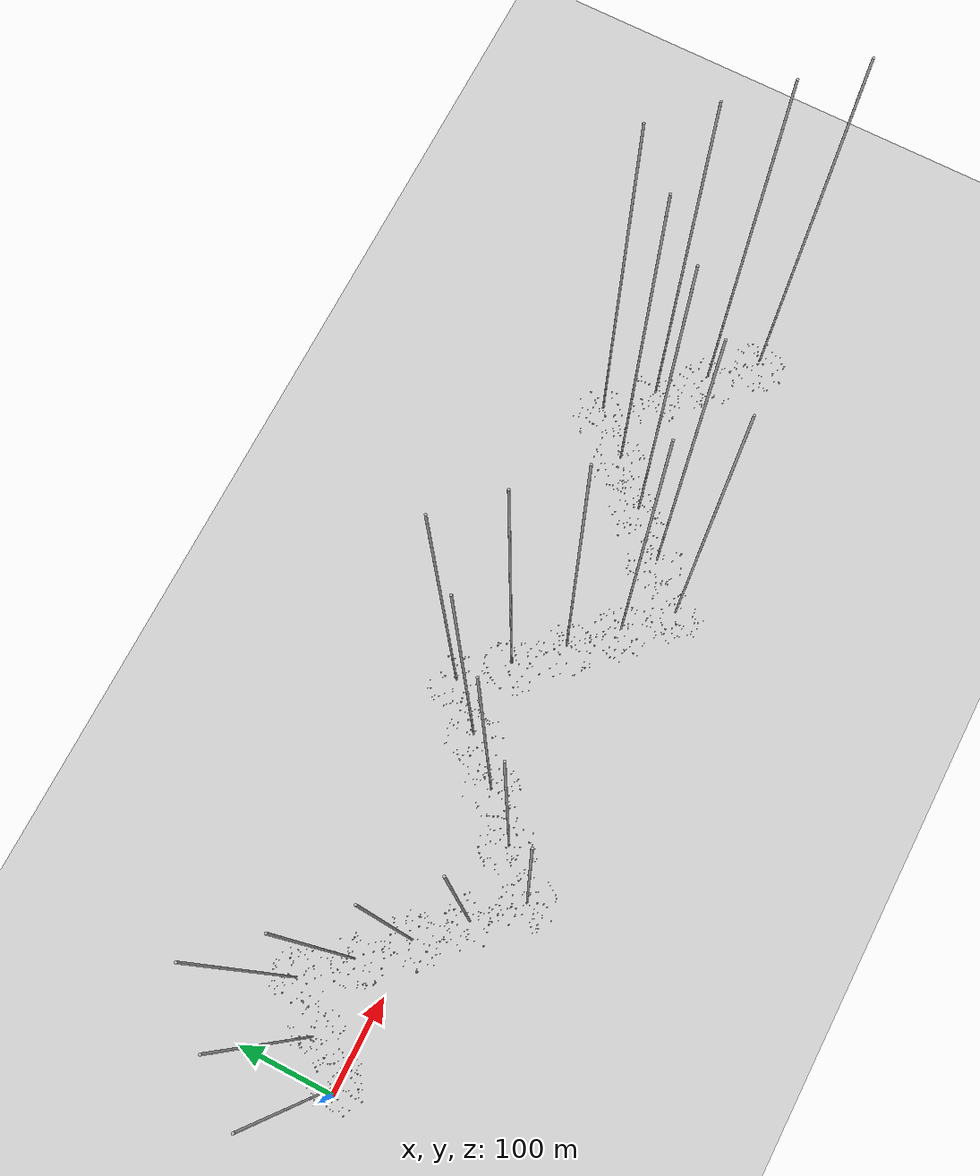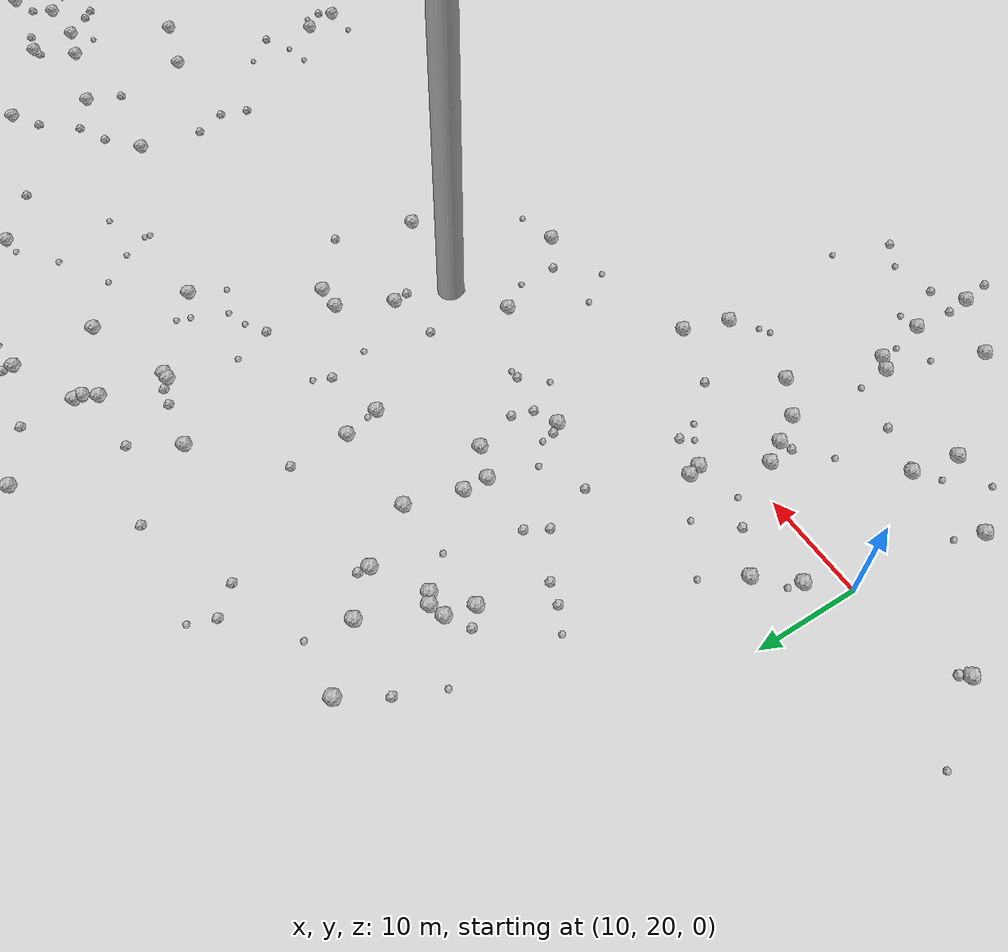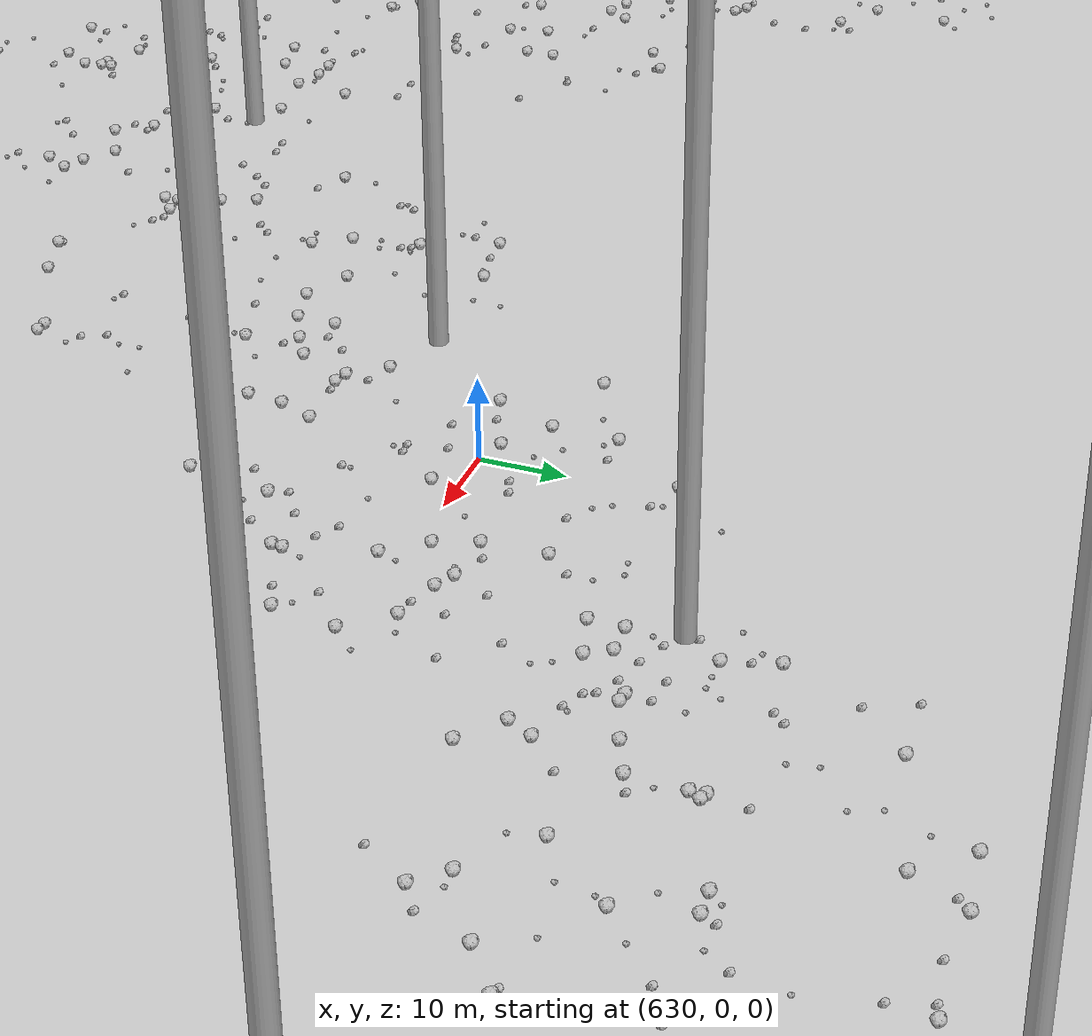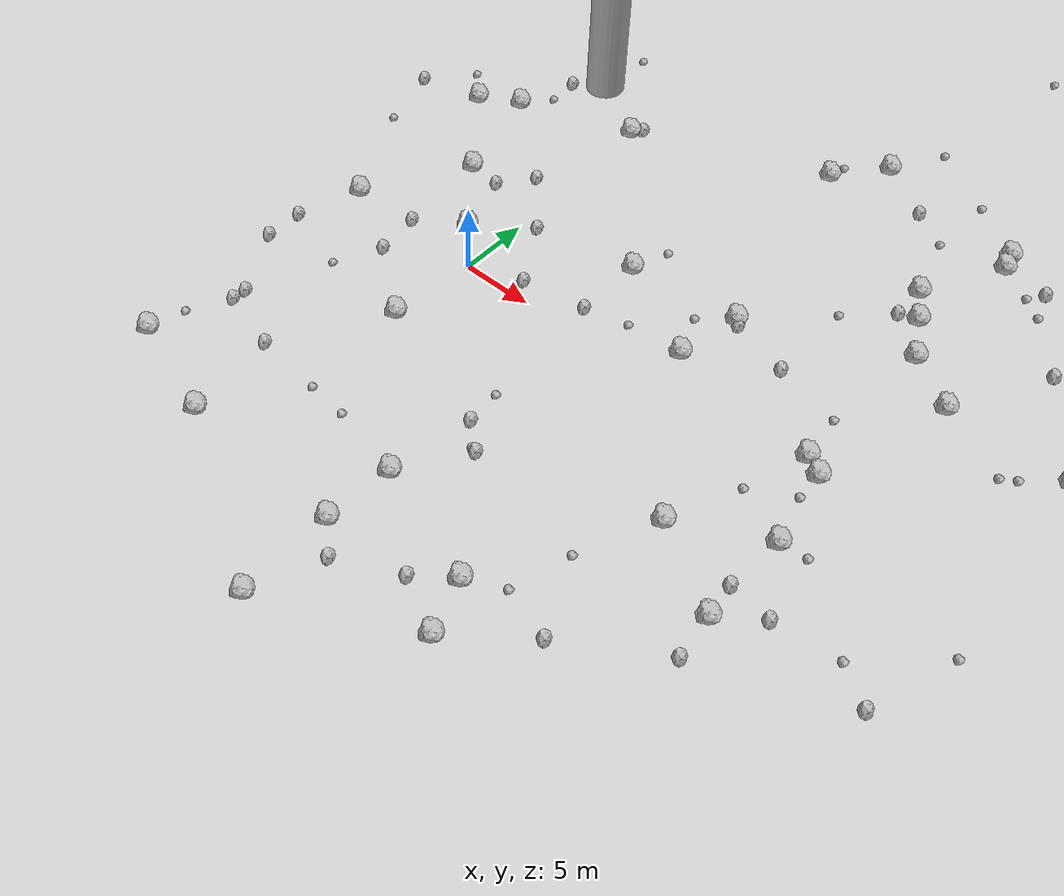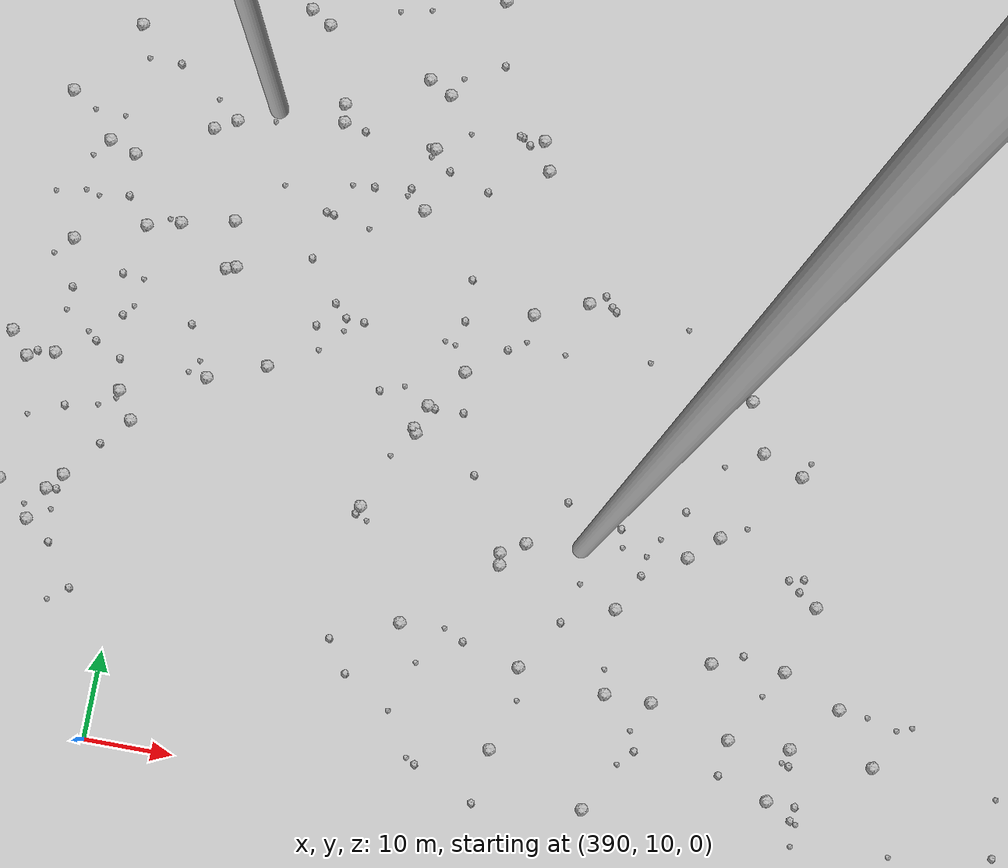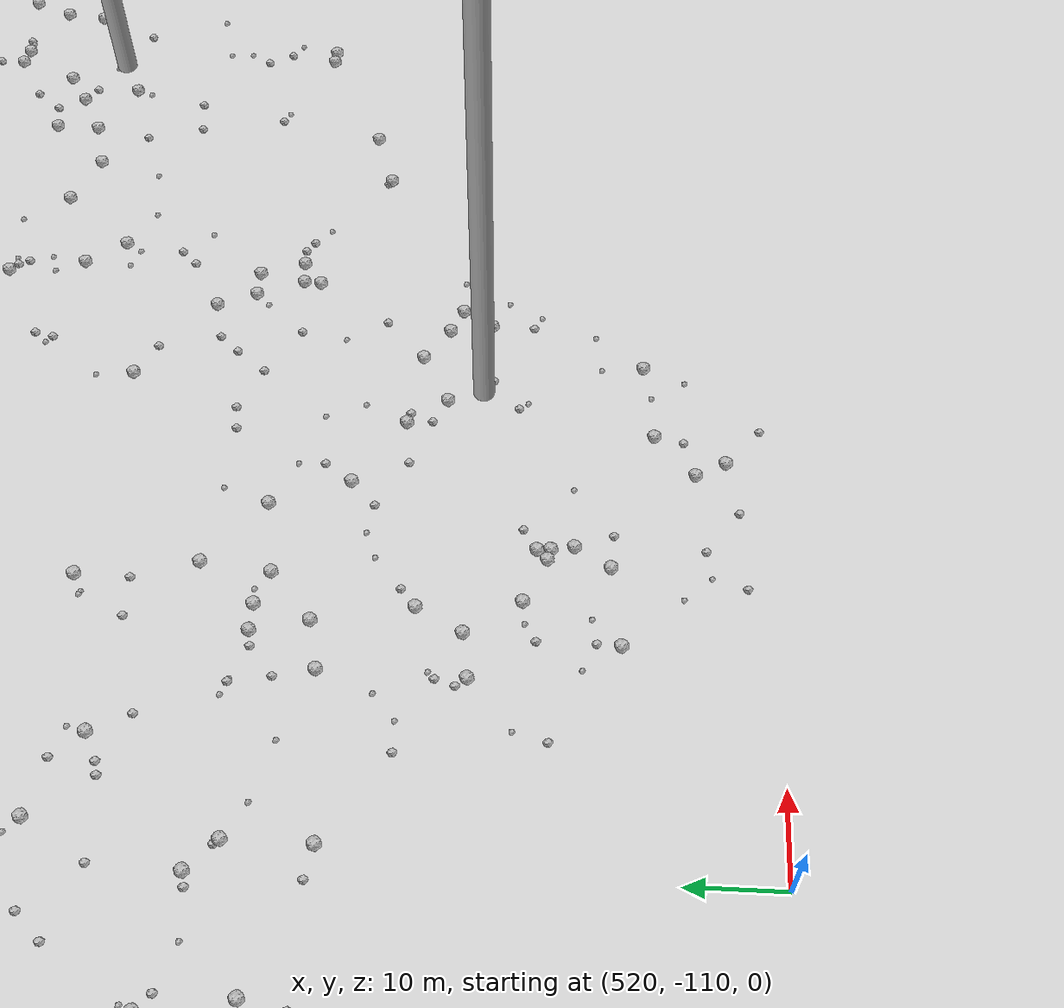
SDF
<sdf version="1.6">
 <world name="default">
  <include><uri>model://custom_ground</uri></include>
  <include><uri>model://sun</uri></include>
  <spherical_coordinates>
   <surface_model>EARTH_WGS84</surface_model>
   <latitude_deg>38.161479</latitude_deg>
   <longitude_deg>-122.454630</longitude_deg>
   <elevation>488.0</elevation>
   <heading_deg>90</heading_deg>
  </spherical_coordinates>
  <model name="rock1_0_0">
   <include><uri>model://rock1</uri><pose>15.06968464582139 3.1069251822697908 0.5 0 0 0</pose></include>
  </model>
  <model name="rock1_0_1">
   <include><uri>model://rock1</uri><pose>26.32892054635883 23.26365452338399 0.5 0 0 0</pose></include>
  </model>
  <model name="rock1_0_2">
   <include><uri>model://rock1</uri><pose>7.983359156215723 -27.1600786561009 0.5 0 0 0</pose></include>
  </model>
  <model name="rock1_0_3">
   <include><uri>model://rock1</uri><pose>25.672643220272633 1.5935807476119166 0.5 0 0 0</pose></include>
  </model>
  <model name="rock1_0_4">
   <include><uri>model://rock1</uri><pose>28.013013848218243 -4.664931365607082 0.5 0 0 0</pose></include>
  </model>
  <model name="rock1_0_5">
   <include><uri>model://rock1</uri><pose>28.02385900879345 -11.26747582423194 0.5 0 0 0</pose></include>
  </model>
  <model name="rock1_0_6">
   <include><uri>model://rock1</uri><pose>26.005816526079904 24.532601337274905 0.5 0 0 0</pose></include>
  </model>
  <model name="rock1_0_7">
   <include><uri>model://rock1</uri><pose>-6.37045352057595 7.337928190752066 0.5 0 0 0</pose></include>
  </model>
  <model name="rock1_0_8">
   <include><uri>model://rock1</uri><pose>-10.3943603163264 0.29350451914721276 0.5 0 0 0</pose></include>
  </model>
  <model name="rock1_0_9">
   <include><uri>model://rock1</uri><pose>17.621321891363756 -22.199948382085143 0.5 0 0 0</pose></include>
  </model>
  <model name="rock1_0_10">
   <include><uri>model://rock1</uri><pose>7.8372452794615945 -20.5351775737021 0.5 0 0 0</pose></include>
  </model>
  <model name="rock1_0_11">
   <include><uri>model://rock1</uri><pose>-2.594352621170156 2.6995090786803857 0.5 0 0 0</pose></include>
  </model>
  <model name="rock1_0_12">
   <include><uri>model://rock1</uri><pose>-11.098757009331056 13.17556472998158 0.5 0 0 0</pose></include>
  </model>
  <model name="rock1_0_13">
   <include><uri>model://rock1</uri><pose>-11.236257242341 -17.776768719447084 0.5 0 0 0</pose></include>
  </model>
  <model name="rock1_0_14">
   <include><uri>model://rock1</uri><pose>15.966883605268805 7.77009678907141 0.5 0 0 0</pose></include>
  </model>
  <model name="rock1_0_15">
   <include><uri>model://rock1</uri><pose>29.78158320771758 10.291071700991111 0.5 0 0 0</pose></include>
  </model>
  <model name="rock1_0_16">
   <include><uri>model://rock1</uri><pose>-8.403282053662405 14.72955864081947 0.5 0 0 0</pose></include>
  </model>
  <model name="rock1_0_17">
   <include><uri>model://rock1</uri><pose>-0.5697220292824916 -6.288996863799433 0.5 0 0 0</pose></include>
  </model>
  <model name="rock1_0_18">
   <include><uri>model://rock1</uri><pose>-4.01353723582465 -20.14588242662689 0.5 0 0 0</pose></include>
  </model>
  <model name="rock1_0_19">
   <include><uri>model://rock1</uri><pose>22.232698336327992 -7.802252686375596 0.5 0 0 0</pose></include>
  </model>
  <model name="rock1_0_20">
   <include><uri>model://rock1</uri><pose>-0.4526756948896029 17.535667757737585 0.5 0 0 0</pose></include>
  </model>
  <model name="rock1_0_21">
   <include><uri>model://rock1</uri><pose>26.16755288130956 12.652695046634662 0.5 0 0 0</pose></include>
  </model>
  <model name="rock1_0_22">
   <include><uri>model://rock1</uri><pose>8.179784647774262 6.963246453315016 0.5 0 0 0</pose></include>
  </model>
  <model name="rock1_0_23">
   <include><uri>model://rock1</uri><pose>26.97527326431269 0.7978880900167269 0.5 0 0 0</pose></include>
  </model>
  <model name="rock1_0_24">
   <include><uri>model://rock1</uri><pose>16.336492920499367 -18.506996959010873 0.5 0 0 0</pose></include>
  </model>
  <model name="rock1_0_25">
   <include><uri>model://rock1</uri><pose>12.676892617470315 23.1828652194554 0.5 0 0 0</pose></include>
  </model>
  <model name="rock1_0_26">
   <include><uri>model://rock1</uri><pose>8.12667684182706 -15.721150473818899 0.5 0 0 0</pose></include>
  </model>
  <model name="rock2_0_0">
   <include><uri>model://rock2</uri><pose>9.068843391936372 -9.729949612706843 0.3 0 0 0</pose></include>
  </model>
  <model name="rock2_0_1">
   <include><uri>model://rock2</uri><pose>10.926197278858496 -11.317063429413494 0.3 0 0 0</pose></include>
  </model>
  <model name="rock2_0_2">
   <include><uri>model://rock2</uri><pose>-3.909846682844062 7.052273251123367 0.3 0 0 0</pose></include>
  </model>
  <model name="rock2_0_3">
   <include><uri>model://rock2</uri><pose>16.400988419394963 7.3757420235059925 0.3 0 0 0</pose></include>
  </model>
  <model name="rock2_0_4">
   <include><uri>model://rock2</uri><pose>-2.1978596730394173 9.343247477389568 0.3 0 0 0</pose></include>
  </model>
  <model name="rock2_0_5">
   <include><uri>model://rock2</uri><pose>30.65832658285995 -9.227726097804766 0.3 0 0 0</pose></include>
  </model>
  <model name="rock2_0_6">
   <include><uri>model://rock2</uri><pose>9.847724966495466 -22.422527273738254 0.3 0 0 0</pose></include>
  </model>
  <model name="rock2_0_7">
   <include><uri>model://rock2</uri><pose>-9.117066524378206 -11.441908433232932 0.3 0 0 0</pose></include>
  </model>
  <model name="rock2_0_8">
   <include><uri>model://rock2</uri><pose>8.164742634545568 2.0249007477511114 0.3 0 0 0</pose></include>
  </model>
  <model name="rock2_0_9">
   <include><uri>model://rock2</uri><pose>-11.775848101888936 -6.895070043496283 0.3 0 0 0</pose></include>
  </model>
  <model name="rock2_0_10">
   <include><uri>model://rock2</uri><pose>27.721314657017295 -8.8213216415175 0.3 0 0 0</pose></include>
  </model>
  <model name="rock2_0_11">
   <include><uri>model://rock2</uri><pose>13.980032819147226 -20.37092167081257 0.3 0 0 0</pose></include>
  </model>
  <model name="rock2_0_12">
   <include><uri>model://rock2</uri><pose>0.14109891294870636 18.257476142941393 0.3 0 0 0</pose></include>
  </model>
  <model name="rock2_0_13">
   <include><uri>model://rock2</uri><pose>-6.966795547348587 18.895536410109607 0.3 0 0 0</pose></include>
  </model>
  <model name="rock2_0_14">
   <include><uri>model://rock2</uri><pose>-5.2617861249496745 -2.6735018968843853 0.3 0 0 0</pose></include>
  </model>
  <model name="rock2_0_15">
   <include><uri>model://rock2</uri><pose>37.580900419945245 -10.38479156259639 0.3 0 0 0</pose></include>
  </model>
  <model name="rock2_0_16">
   <include><uri>model://rock2</uri><pose>-15.46605516693436 12.050879172859965 0.3 0 0 0</pose></include>
  </model>
  <model name="rock2_0_17">
   <include><uri>model://rock2</uri><pose>-9.161317775330458 -12.460523859609978 0.3 0 0 0</pose></include>
  </model>
  <model name="rock2_0_18">
   <include><uri>model://rock2</uri><pose>19.375223429768205 24.004391319342545 0.3 0 0 0</pose></include>
  </model>
  <model name="rock2_0_19">
   <include><uri>model://rock2</uri><pose>3.670279032440259 1.2601996631674623 0.3 0 0 0</pose></include>
  </model>
  <model name="rock2_0_20">
   <include><uri>model://rock2</uri><pose>-5.698757492746804 0.5522267589725658 0.3 0 0 0</pose></include>
  </model>
  <model name="rock2_0_21">
   <include><uri>model://rock2</uri><pose>22.323444071755233 -18.337581968906026 0.3 0 0 0</pose></include>
  </model>
  <model name="rock2_0_22">
   <include><uri>model://rock2</uri><pose>1.0941339520509388 5.582283498468868 0.3 0 0 0</pose></include>
  </model>
  <model name="rock2_0_23">
   <include><uri>model://rock2</uri><pose>-4.805972382700993 -13.72369765079037 0.3 0 0 0</pose></include>
  </model>
  <model name="rock2_0_24">
   <include><uri>model://rock2</uri><pose>28.450826261389288 -14.367121642334276 0.3 0 0 0</pose></include>
  </model>
  <model name="rock2_0_25">
   <include><uri>model://rock2</uri><pose>-11.766900031351742 -4.207889690075163 0.3 0 0 0</pose></include>
  </model>
  <model name="rock2_0_26">
   <include><uri>model://rock2</uri><pose>20.579176238337084 6.140432063777112 0.3 0 0 0</pose></include>
  </model>
  <model name="rock3_0_0">
   <include><uri>model://rock3</uri><pose>35.8432713329381 8.271224612250151 0.2 0 0 0</pose></include>
  </model>
  <model name="rock3_0_1">
   <include><uri>model://rock3</uri><pose>12.980148217668763 24.447101420860207 0.2 0 0 0</pose></include>
  </model>
  <model name="rock3_0_2">
   <include><uri>model://rock3</uri><pose>-6.940709831143604 16.642500932529288 0.2 0 0 0</pose></include>
  </model>
  <model name="rock3_0_3">
   <include><uri>model://rock3</uri><pose>24.24270426994967 -2.9096783958652637 0.2 0 0 0</pose></include>
  </model>
  <model name="rock3_0_4">
   <include><uri>model://rock3</uri><pose>8.789379792919402 -7.213222431549983 0.2 0 0 0</pose></include>
  </model>
  <model name="rock3_0_5">
   <include><uri>model://rock3</uri><pose>21.95940574739491 22.30661858556647 0.2 0 0 0</pose></include>
  </model>
  <model name="rock3_0_6">
   <include><uri>model://rock3</uri><pose>10.47258669833974 -11.234725296211884 0.2 0 0 0</pose></include>
  </model>
  <model name="rock3_0_7">
   <include><uri>model://rock3</uri><pose>0.0011203497933856 -14.265905756262047 0.2 0 0 0</pose></include>
  </model>
  <model name="rock3_0_8">
   <include><uri>model://rock3</uri><pose>18.76656182074275 -17.276447351055054 0.2 0 0 0</pose></include>
  </model>
  <model name="rock3_0_9">
   <include><uri>model://rock3</uri><pose>-13.04867573133087 15.065222599086518 0.2 0 0 0</pose></include>
  </model>
  <model name="rock3_0_10">
   <include><uri>model://rock3</uri><pose>9.063635578710517 9.557597105215912 0.2 0 0 0</pose></include>
  </model>
  <model name="rock3_0_11">
   <include><uri>model://rock3</uri><pose>22.227530973404527 27.230637129913823 0.2 0 0 0</pose></include>
  </model>
  <model name="rock3_0_12">
   <include><uri>model://rock3</uri><pose>34.908576138699495 7.664547284606051 0.2 0 0 0</pose></include>
  </model>
  <model name="rock3_0_13">
   <include><uri>model://rock3</uri><pose>29.87118143716952 -4.499223593900073 0.2 0 0 0</pose></include>
  </model>
  <model name="rock3_0_14">
   <include><uri>model://rock3</uri><pose>20.599280653265403 12.394848187015192 0.2 0 0 0</pose></include>
  </model>
  <model name="rock3_0_15">
   <include><uri>model://rock3</uri><pose>27.06162198996092 -1.240009595469317 0.2 0 0 0</pose></include>
  </model>
  <model name="rock3_0_16">
   <include><uri>model://rock3</uri><pose>11.1433470459868 2.7605073555918125 0.2 0 0 0</pose></include>
  </model>
  <model name="rock3_0_17">
   <include><uri>model://rock3</uri><pose>-4.84292706490039 24.468747251647912 0.2 0 0 0</pose></include>
  </model>
  <model name="rock3_0_18">
   <include><uri>model://rock3</uri><pose>13.936898506243587 5.99350678399022 0.2 0 0 0</pose></include>
  </model>
  <model name="rock3_0_19">
   <include><uri>model://rock3</uri><pose>-14.176036004958103 7.395776615450586 0.2 0 0 0</pose></include>
  </model>
  <model name="rock3_0_20">
   <include><uri>model://rock3</uri><pose>-10.660950445719264 -15.252583153778613 0.2 0 0 0</pose></include>
  </model>
  <model name="rock3_0_21">
   <include><uri>model://rock3</uri><pose>25.262932312133337 4.9082400158718045 0.2 0 0 0</pose></include>
  </model>
  <model name="rock3_0_22">
   <include><uri>model://rock3</uri><pose>35.04612867631732 -8.758487058082373 0.2 0 0 0</pose></include>
  </model>
  <model name="rock3_0_23">
   <include><uri>model://rock3</uri><pose>2.8585435294266475 -14.55665904091453 0.2 0 0 0</pose></include>
  </model>
  <model name="rock3_0_24">
   <include><uri>model://rock3</uri><pose>-6.830703384344741 -5.853134338113627 0.2 0 0 0</pose></include>
  </model>
  <model name="rock3_0_25">
   <include><uri>model://rock3</uri><pose>39.55018255133952 -4.492276905010758 0.2 0 0 0</pose></include>
  </model>
  <model name="rock3_0_26">
   <include><uri>model://rock3</uri><pose>19.896209615094534 -13.172325762848185 0.2 0 0 0</pose></include>
  </model>
  <model name="rock1_1_0">
   <include><uri>model://rock1</uri><pose>38.23161895116395 38.544075879494926 0.5 0 0 0</pose></include>
  </model>
  <model name="rock1_1_1">
   <include><uri>model://rock1</uri><pose>36.768270273292885 31.22415277182791 0.5 0 0 0</pose></include>
  </model>
  <model name="rock1_1_2">
   <include><uri>model://rock1</uri><pose>23.29876731462915 17.669278416350775 0.5 0 0 0</pose></include>
  </model>
  <model name="rock1_1_3">
   <include><uri>model://rock1</uri><pose>59.968394818352486 41.78369352937954 0.5 0 0 0</pose></include>
  </model>
  <model name="rock1_1_4">
   <include><uri>model://rock1</uri><pose>39.6279955307414 14.704975863418762 0.5 0 0 0</pose></include>
  </model>
  <model name="rock1_1_5">
   <include><uri>model://rock1</uri><pose>66.13627424229554 29.628116119262277 0.5 0 0 0</pose></include>
  </model>
  <model name="rock1_1_6">
   <include><uri>model://rock1</uri><pose>35.04812066902744 39.77644469207142 0.5 0 0 0</pose></include>
  </model>
  <model name="rock1_1_7">
   <include><uri>model://rock1</uri><pose>27.127893653552825 50.26993377519569 0.5 0 0 0</pose></include>
  </model>
  <model name="rock1_1_8">
   <include><uri>model://rock1</uri><pose>24.57557439303748 15.503785070836006 0.5 0 0 0</pose></include>
  </model>
  <model name="rock1_1_9">
   <include><uri>model://rock1</uri><pose>62.555541703076486 41.857510050221165 0.5 0 0 0</pose></include>
  </model>
  <model name="rock1_1_10">
   <include><uri>model://rock1</uri><pose>57.466413867500826 36.5194523232483 0.5 0 0 0</pose></include>
  </model>
  <model name="rock1_1_11">
   <include><uri>model://rock1</uri><pose>56.575602300875524 18.57600741118003 0.5 0 0 0</pose></include>
  </model>
  <model name="rock1_1_12">
   <include><uri>model://rock1</uri><pose>52.329176966350964 60.87955390779811 0.5 0 0 0</pose></include>
  </model>
  <model name="rock1_1_13">
   <include><uri>model://rock1</uri><pose>24.20531312020059 60.57107310614629 0.5 0 0 0</pose></include>
  </model>
  <model name="rock1_1_14">
   <include><uri>model://rock1</uri><pose>45.659934146487814 48.01541570791017 0.5 0 0 0</pose></include>
  </model>
  <model name="rock1_1_15">
   <include><uri>model://rock1</uri><pose>32.71446555354946 52.71733670406773 0.5 0 0 0</pose></include>
  </model>
  <model name="rock1_1_16">
   <include><uri>model://rock1</uri><pose>28.094276072520042 49.68263762838148 0.5 0 0 0</pose></include>
  </model>
  <model name="rock1_1_17">
   <include><uri>model://rock1</uri><pose>46.63875107567698 44.48530353742186 0.5 0 0 0</pose></include>
  </model>
  <model name="rock1_1_18">
   <include><uri>model://rock1</uri><pose>25.066960521365598 47.069583316350005 0.5 0 0 0</pose></include>
  </model>
  <model name="rock1_1_19">
   <include><uri>model://rock1</uri><pose>25.643797680152407 49.75117548128173 0.5 0 0 0</pose></include>
  </model>
  <model name="rock1_1_20">
   <include><uri>model://rock1</uri><pose>50.87749391742453 27.529143912596307 0.5 0 0 0</pose></include>
  </model>
  <model name="rock1_1_21">
   <include><uri>model://rock1</uri><pose>38.21512215340781 10.205363046975739 0.5 0 0 0</pose></include>
  </model>
  <model name="rock1_1_22">
   <include><uri>model://rock1</uri><pose>29.207302293131836 56.094180730022316 0.5 0 0 0</pose></include>
  </model>
  <model name="rock1_1_23">
   <include><uri>model://rock1</uri><pose>15.413232130529495 26.533996914993434 0.5 0 0 0</pose></include>
  </model>
  <model name="rock1_1_24">
   <include><uri>model://rock1</uri><pose>35.097218077395056 42.184998486683575 0.5 0 0 0</pose></include>
  </model>
  <model name="rock1_1_25">
   <include><uri>model://rock1</uri><pose>36.49711990161039 47.39468649999454 0.5 0 0 0</pose></include>
  </model>
  <model name="rock1_1_26">
   <include><uri>model://rock1</uri><pose>60.92280253889184 59.278021569944016 0.5 0 0 0</pose></include>
  </model>
  <model name="rock2_1_0">
   <include><uri>model://rock2</uri><pose>28.980968099153092 39.93091562877599 0.3 0 0 0</pose></include>
  </model>
  <model name="rock2_1_1">
   <include><uri>model://rock2</uri><pose>29.54198731468512 22.86161311177736 0.3 0 0 0</pose></include>
  </model>
  <model name="rock2_1_2">
   <include><uri>model://rock2</uri><pose>57.25112126864022 60.28600245542146 0.3 0 0 0</pose></include>
  </model>
  <model name="rock2_1_3">
   <include><uri>model://rock2</uri><pose>52.181569062053924 46.12397591251663 0.3 0 0 0</pose></include>
  </model>
  <model name="rock2_1_4">
   <include><uri>model://rock2</uri><pose>29.632834761915273 33.11217003057895 0.3 0 0 0</pose></include>
  </model>
  <model name="rock2_1_5">
   <include><uri>model://rock2</uri><pose>36.042026891079246 32.12656950570069 0.3 0 0 0</pose></include>
  </model>
  <model name="rock2_1_6">
   <include><uri>model://rock2</uri><pose>45.20718562148022 53.84153665233297 0.3 0 0 0</pose></include>
  </model>
  <model name="rock2_1_7">
   <include><uri>model://rock2</uri><pose>21.59859466702665 41.35776200083341 0.3 0 0 0</pose></include>
  </model>
  <model name="rock2_1_8">
   <include><uri>model://rock2</uri><pose>59.14781596436742 59.979236144278886 0.3 0 0 0</pose></include>
  </model>
  <model name="rock2_1_9">
   <include><uri>model://rock2</uri><pose>57.718523517086496 34.98792952656728 0.3 0 0 0</pose></include>
  </model>
  <model name="rock2_1_10">
   <include><uri>model://rock2</uri><pose>39.630465826721725 34.31719589056013 0.3 0 0 0</pose></include>
  </model>
  <model name="rock2_1_11">
   <include><uri>model://rock2</uri><pose>23.685911686477784 40.75749301665121 0.3 0 0 0</pose></include>
  </model>
  <model name="rock2_1_12">
   <include><uri>model://rock2</uri><pose>33.42372912713486 16.916351920523386 0.3 0 0 0</pose></include>
  </model>
  <model name="rock2_1_13">
   <include><uri>model://rock2</uri><pose>52.1404551389281 35.510251266950846 0.3 0 0 0</pose></include>
  </model>
  <model name="rock2_1_14">
   <include><uri>model://rock2</uri><pose>60.510842539593064 48.89708908838579 0.3 0 0 0</pose></include>
  </model>
  <model name="rock2_1_15">
   <include><uri>model://rock2</uri><pose>43.0967834350723 31.408881147766 0.3 0 0 0</pose></include>
  </model>
  <model name="rock2_1_16">
   <include><uri>model://rock2</uri><pose>23.363222672216004 15.083462877671066 0.3 0 0 0</pose></include>
  </model>
  <model name="rock2_1_17">
   <include><uri>model://rock2</uri><pose>52.95545629058875 20.744619706448074 0.3 0 0 0</pose></include>
  </model>
  <model name="rock2_1_18">
   <include><uri>model://rock2</uri><pose>46.494149934173365 67.2942805022995 0.3 0 0 0</pose></include>
  </model>
  <model name="rock2_1_19">
   <include><uri>model://rock2</uri><pose>21.868277719981503 56.637614766409236 0.3 0 0 0</pose></include>
  </model>
  <model name="rock2_1_20">
   <include><uri>model://rock2</uri><pose>27.887668919436052 37.909042965116384 0.3 0 0 0</pose></include>
  </model>
  <model name="rock2_1_21">
   <include><uri>model://rock2</uri><pose>68.12519505380874 37.514039209621686 0.3 0 0 0</pose></include>
  </model>
  <model name="rock2_1_22">
   <include><uri>model://rock2</uri><pose>32.785291006131445 53.780731753264604 0.3 0 0 0</pose></include>
  </model>
  <model name="rock2_1_23">
   <include><uri>model://rock2</uri><pose>39.03899271168491 32.260050329118684 0.3 0 0 0</pose></include>
  </model>
  <model name="rock2_1_24">
   <include><uri>model://rock2</uri><pose>37.37339789526938 63.000040645224246 0.3 0 0 0</pose></include>
  </model>
  <model name="rock2_1_25">
   <include><uri>model://rock2</uri><pose>35.05554949848727 65.30076283533762 0.3 0 0 0</pose></include>
  </model>
  <model name="rock2_1_26">
   <include><uri>model://rock2</uri><pose>23.52458063040825 48.382614852208036 0.3 0 0 0</pose></include>
  </model>
  <model name="rock3_1_0">
   <include><uri>model://rock3</uri><pose>17.500203461580618 30.262132508904244 0.2 0 0 0</pose></include>
  </model>
  <model name="rock3_1_1">
   <include><uri>model://rock3</uri><pose>44.01098674101698 31.410951985730453 0.2 0 0 0</pose></include>
  </model>
  <model name="rock3_1_2">
   <include><uri>model://rock3</uri><pose>66.06313489435068 54.33428407298728 0.2 0 0 0</pose></include>
  </model>
  <model name="rock3_1_3">
   <include><uri>model://rock3</uri><pose>46.398704486839954 45.429127257587666 0.2 0 0 0</pose></include>
  </model>
  <model name="rock3_1_4">
   <include><uri>model://rock3</uri><pose>19.294878548073697 42.49594975503703 0.2 0 0 0</pose></include>
  </model>
  <model name="rock3_1_5">
   <include><uri>model://rock3</uri><pose>52.802818807933456 24.589691261100022 0.2 0 0 0</pose></include>
  </model>
  <model name="rock3_1_6">
   <include><uri>model://rock3</uri><pose>25.337473089190254 47.15171458299866 0.2 0 0 0</pose></include>
  </model>
  <model name="rock3_1_7">
   <include><uri>model://rock3</uri><pose>64.65770772841037 50.94062979691132 0.2 0 0 0</pose></include>
  </model>
  <model name="rock3_1_8">
   <include><uri>model://rock3</uri><pose>67.62342635718153 49.80868175709524 0.2 0 0 0</pose></include>
  </model>
  <model name="rock3_1_9">
   <include><uri>model://rock3</uri><pose>35.89108115161758 67.64323669651704 0.2 0 0 0</pose></include>
  </model>
  <model name="rock3_1_10">
   <include><uri>model://rock3</uri><pose>49.76606269295553 16.97029082587374 0.2 0 0 0</pose></include>
  </model>
  <model name="rock3_1_11">
   <include><uri>model://rock3</uri><pose>30.18052558325287 20.670213757091783 0.2 0 0 0</pose></include>
  </model>
  <model name="rock3_1_12">
   <include><uri>model://rock3</uri><pose>47.336087653413145 20.228319271765166 0.2 0 0 0</pose></include>
  </model>
  <model name="rock3_1_13">
   <include><uri>model://rock3</uri><pose>60.580039891772294 19.421540884993817 0.2 0 0 0</pose></include>
  </model>
  <model name="rock3_1_14">
   <include><uri>model://rock3</uri><pose>29.618257335817393 60.27500577426498 0.2 0 0 0</pose></include>
  </model>
  <model name="rock3_1_15">
   <include><uri>model://rock3</uri><pose>28.74472692715727 21.72314705389694 0.2 0 0 0</pose></include>
  </model>
  <model name="rock3_1_16">
   <include><uri>model://rock3</uri><pose>20.117792173761245 52.559453929863636 0.2 0 0 0</pose></include>
  </model>
  <model name="rock3_1_17">
   <include><uri>model://rock3</uri><pose>30.627311816080862 46.818236306712144 0.2 0 0 0</pose></include>
  </model>
  <model name="rock3_1_18">
   <include><uri>model://rock3</uri><pose>35.784057658216554 33.38241840423344 0.2 0 0 0</pose></include>
  </model>
  <model name="rock3_1_19">
   <include><uri>model://rock3</uri><pose>58.89208277729333 52.577698958534526 0.2 0 0 0</pose></include>
  </model>
  <model name="rock3_1_20">
   <include><uri>model://rock3</uri><pose>41.06725980091435 29.053975778833514 0.2 0 0 0</pose></include>
  </model>
  <model name="rock3_1_21">
   <include><uri>model://rock3</uri><pose>52.88189635796638 47.73382162358411 0.2 0 0 0</pose></include>
  </model>
  <model name="rock3_1_22">
   <include><uri>model://rock3</uri><pose>36.35944059537452 31.743861925401397 0.2 0 0 0</pose></include>
  </model>
  <model name="rock3_1_23">
   <include><uri>model://rock3</uri><pose>53.44217522470584 42.03457596762565 0.2 0 0 0</pose></include>
  </model>
  <model name="rock3_1_24">
   <include><uri>model://rock3</uri><pose>33.75309238040873 35.16252612721438 0.2 0 0 0</pose></include>
  </model>
  <model name="rock3_1_25">
   <include><uri>model://rock3</uri><pose>62.52845324809981 50.185090710978855 0.2 0 0 0</pose></include>
  </model>
  <model name="rock3_1_26">
   <include><uri>model://rock3</uri><pose>55.18306400558454 30.05793113935928 0.2 0 0 0</pose></include>
  </model>
  <model name="rock1_2_0">
   <include><uri>model://rock1</uri><pose>56.31942153592422 75.58313988186134 0.5 0 0 0</pose></include>
  </model>
  <model name="rock1_2_1">
   <include><uri>model://rock1</uri><pose>60.244007800712 87.60001653645176 0.5 0 0 0</pose></include>
  </model>
  <model name="rock1_2_2">
   <include><uri>model://rock1</uri><pose>92.0350446227574 96.71944354909172 0.5 0 0 0</pose></include>
  </model>
  <model name="rock1_2_3">
   <include><uri>model://rock1</uri><pose>62.469859684878074 66.70395385608109 0.5 0 0 0</pose></include>
  </model>
  <model name="rock1_2_4">
   <include><uri>model://rock1</uri><pose>80.41991628026128 107.91020825166228 0.5 0 0 0</pose></include>
  </model>
  <model name="rock1_2_5">
   <include><uri>model://rock1</uri><pose>72.24339415166236 83.12844863036838 0.5 0 0 0</pose></include>
  </model>
  <model name="rock1_2_6">
   <include><uri>model://rock1</uri><pose>77.69684058923961 81.36216043188598 0.5 0 0 0</pose></include>
  </model>
  <model name="rock1_2_7">
   <include><uri>model://rock1</uri><pose>69.2186870872943 70.98117541776757 0.5 0 0 0</pose></include>
  </model>
  <model name="rock1_2_8">
   <include><uri>model://rock1</uri><pose>56.00405518723457 92.95304138443521 0.5 0 0 0</pose></include>
  </model>
  <model name="rock1_2_9">
   <include><uri>model://rock1</uri><pose>70.55491980605771 102.6219025595812 0.5 0 0 0</pose></include>
  </model>
  <model name="rock1_2_10">
   <include><uri>model://rock1</uri><pose>86.89010514136953 92.35572235016363 0.5 0 0 0</pose></include>
  </model>
  <model name="rock1_2_11">
   <include><uri>model://rock1</uri><pose>62.43415222913452 67.45415537922923 0.5 0 0 0</pose></include>
  </model>
  <model name="rock1_2_12">
   <include><uri>model://rock1</uri><pose>87.74106963578147 77.25921875023514 0.5 0 0 0</pose></include>
  </model>
  <model name="rock1_2_13">
   <include><uri>model://rock1</uri><pose>102.28473819119782 94.1467288871689 0.5 0 0 0</pose></include>
  </model>
  <model name="rock1_2_14">
   <include><uri>model://rock1</uri><pose>60.18662094878806 59.22962099890319 0.5 0 0 0</pose></include>
  </model>
  <model name="rock1_2_15">
   <include><uri>model://rock1</uri><pose>85.7899863679525 66.28538268128935 0.5 0 0 0</pose></include>
  </model>
  <model name="rock1_2_16">
   <include><uri>model://rock1</uri><pose>72.97292086453302 94.3473121861692 0.5 0 0 0</pose></include>
  </model>
  <model name="rock1_2_17">
   <include><uri>model://rock1</uri><pose>107.47128651197015 80.75405533221738 0.5 0 0 0</pose></include>
  </model>
  <model name="rock1_2_18">
   <include><uri>model://rock1</uri><pose>78.00198426420195 90.87558684632494 0.5 0 0 0</pose></include>
  </model>
  <model name="rock1_2_19">
   <include><uri>model://rock1</uri><pose>69.15081072398844 53.29469020087719 0.5 0 0 0</pose></include>
  </model>
  <model name="rock1_2_20">
   <include><uri>model://rock1</uri><pose>75.66675294409413 105.59719127666327 0.5 0 0 0</pose></include>
  </model>
  <model name="rock1_2_21">
   <include><uri>model://rock1</uri><pose>78.32231225369298 70.95550915878934 0.5 0 0 0</pose></include>
  </model>
  <model name="rock1_2_22">
   <include><uri>model://rock1</uri><pose>84.2926521283677 77.32308505156274 0.5 0 0 0</pose></include>
  </model>
  <model name="rock1_2_23">
   <include><uri>model://rock1</uri><pose>95.50739510937635 73.09118246033849 0.5 0 0 0</pose></include>
  </model>
  <model name="rock1_2_24">
   <include><uri>model://rock1</uri><pose>96.25623597729836 97.285369183322 0.5 0 0 0</pose></include>
  </model>
  <model name="rock1_2_25">
   <include><uri>model://rock1</uri><pose>61.59402507004903 65.41195829194393 0.5 0 0 0</pose></include>
  </model>
  <model name="rock1_2_26">
   <include><uri>model://rock1</uri><pose>69.76319782142437 62.91600929765361 0.5 0 0 0</pose></include>
  </model>
  <model name="rock2_2_0">
   <include><uri>model://rock2</uri><pose>101.80250429822526 92.55355062996387 0.3 0 0 0</pose></include>
  </model>
  <model name="rock2_2_1">
   <include><uri>model://rock2</uri><pose>63.408195564597705 94.8428053712239 0.3 0 0 0</pose></include>
  </model>
  <model name="rock2_2_2">
   <include><uri>model://rock2</uri><pose>84.96424383822634 105.09093381433652 0.3 0 0 0</pose></include>
  </model>
  <model name="rock2_2_3">
   <include><uri>model://rock2</uri><pose>91.43232924519756 76.78418025267247 0.3 0 0 0</pose></include>
  </model>
  <model name="rock2_2_4">
   <include><uri>model://rock2</uri><pose>91.1981432312899 62.31002910425666 0.3 0 0 0</pose></include>
  </model>
  <model name="rock2_2_5">
   <include><uri>model://rock2</uri><pose>72.56762572203047 76.07108238931903 0.3 0 0 0</pose></include>
  </model>
  <model name="rock2_2_6">
   <include><uri>model://rock2</uri><pose>100.92590329562603 85.45890970757767 0.3 0 0 0</pose></include>
  </model>
  <model name="rock2_2_7">
   <include><uri>model://rock2</uri><pose>79.28673851022856 105.9791406612088 0.3 0 0 0</pose></include>
  </model>
  <model name="rock2_2_8">
   <include><uri>model://rock2</uri><pose>73.06001211967441 92.59881549465526 0.3 0 0 0</pose></include>
  </model>
  <model name="rock2_2_9">
   <include><uri>model://rock2</uri><pose>68.6968637448993 91.41306064287454 0.3 0 0 0</pose></include>
  </model>
  <model name="rock2_2_10">
   <include><uri>model://rock2</uri><pose>77.94656638671042 72.18739975215132 0.3 0 0 0</pose></include>
  </model>
  <model name="rock2_2_11">
   <include><uri>model://rock2</uri><pose>77.9304180516904 104.20678230647623 0.3 0 0 0</pose></include>
  </model>
  <model name="rock2_2_12">
   <include><uri>model://rock2</uri><pose>67.13475185360028 88.93048338796098 0.3 0 0 0</pose></include>
  </model>
  <model name="rock2_2_13">
   <include><uri>model://rock2</uri><pose>59.68695902552039 101.41674235443008 0.3 0 0 0</pose></include>
  </model>
  <model name="rock2_2_14">
   <include><uri>model://rock2</uri><pose>93.38556147834319 105.34366385121562 0.3 0 0 0</pose></include>
  </model>
  <model name="rock2_2_15">
   <include><uri>model://rock2</uri><pose>88.9801185295384 91.6522673241198 0.3 0 0 0</pose></include>
  </model>
  <model name="rock2_2_16">
   <include><uri>model://rock2</uri><pose>54.95220286776924 65.33271541429357 0.3 0 0 0</pose></include>
  </model>
  <model name="rock2_2_17">
   <include><uri>model://rock2</uri><pose>69.18352054723077 72.03922585912555 0.3 0 0 0</pose></include>
  </model>
  <model name="rock2_2_18">
   <include><uri>model://rock2</uri><pose>65.71794423482908 101.49971200042518 0.3 0 0 0</pose></include>
  </model>
  <model name="rock2_2_19">
   <include><uri>model://rock2</uri><pose>84.52640493774987 107.40252902774674 0.3 0 0 0</pose></include>
  </model>
  <model name="rock2_2_20">
   <include><uri>model://rock2</uri><pose>61.95123507177898 72.66994731983388 0.3 0 0 0</pose></include>
  </model>
  <model name="rock2_2_21">
   <include><uri>model://rock2</uri><pose>89.60879914146443 73.99462276241599 0.3 0 0 0</pose></include>
  </model>
  <model name="rock2_2_22">
   <include><uri>model://rock2</uri><pose>96.67628562004296 89.65273543666734 0.3 0 0 0</pose></include>
  </model>
  <model name="rock2_2_23">
   <include><uri>model://rock2</uri><pose>66.76019605531258 99.8122906855295 0.3 0 0 0</pose></include>
  </model>
  <model name="rock2_2_24">
   <include><uri>model://rock2</uri><pose>98.61978432464943 81.29770053992334 0.3 0 0 0</pose></include>
  </model>
  <model name="rock2_2_25">
   <include><uri>model://rock2</uri><pose>90.59055785573752 92.89243714881012 0.3 0 0 0</pose></include>
  </model>
  <model name="rock2_2_26">
   <include><uri>model://rock2</uri><pose>91.4843694796668 99.34169405228195 0.3 0 0 0</pose></include>
  </model>
  <model name="rock3_2_0">
   <include><uri>model://rock3</uri><pose>91.58042866188273 83.02134771606845 0.2 0 0 0</pose></include>
  </model>
  <model name="rock3_2_1">
   <include><uri>model://rock3</uri><pose>66.43248594147856 76.58506561467367 0.2 0 0 0</pose></include>
  </model>
  <model name="rock3_2_2">
   <include><uri>model://rock3</uri><pose>83.74969033246225 65.89950610229708 0.2 0 0 0</pose></include>
  </model>
  <model name="rock3_2_3">
   <include><uri>model://rock3</uri><pose>74.74421446720899 59.42836363147402 0.2 0 0 0</pose></include>
  </model>
  <model name="rock3_2_4">
   <include><uri>model://rock3</uri><pose>82.94406155036569 56.19647655042526 0.2 0 0 0</pose></include>
  </model>
  <model name="rock3_2_5">
   <include><uri>model://rock3</uri><pose>59.96748578980606 95.66218069995631 0.2 0 0 0</pose></include>
  </model>
  <model name="rock3_2_6">
   <include><uri>model://rock3</uri><pose>100.57944211278291 100.97095178750303 0.2 0 0 0</pose></include>
  </model>
  <model name="rock3_2_7">
   <include><uri>model://rock3</uri><pose>105.96796582346578 86.82227508897087 0.2 0 0 0</pose></include>
  </model>
  <model name="rock3_2_8">
   <include><uri>model://rock3</uri><pose>75.71374653905872 90.15677228546829 0.2 0 0 0</pose></include>
  </model>
  <model name="rock3_2_9">
   <include><uri>model://rock3</uri><pose>77.34395676516488 56.49218607559082 0.2 0 0 0</pose></include>
  </model>
  <model name="rock3_2_10">
   <include><uri>model://rock3</uri><pose>83.74617734438776 107.15858179058 0.2 0 0 0</pose></include>
  </model>
  <model name="rock3_2_11">
   <include><uri>model://rock3</uri><pose>93.47067850668122 71.442532320105 0.2 0 0 0</pose></include>
  </model>
  <model name="rock3_2_12">
   <include><uri>model://rock3</uri><pose>72.46948607783445 71.29405312585912 0.2 0 0 0</pose></include>
  </model>
  <model name="rock3_2_13">
   <include><uri>model://rock3</uri><pose>101.33825114145824 90.37876020210489 0.2 0 0 0</pose></include>
  </model>
  <model name="rock3_2_14">
   <include><uri>model://rock3</uri><pose>63.2160293992753 85.55826395493008 0.2 0 0 0</pose></include>
  </model>
  <model name="rock3_2_15">
   <include><uri>model://rock3</uri><pose>64.47621089948743 83.02485986492283 0.2 0 0 0</pose></include>
  </model>
  <model name="rock3_2_16">
   <include><uri>model://rock3</uri><pose>71.47110258182508 81.33229025673285 0.2 0 0 0</pose></include>
  </model>
  <model name="rock3_2_17">
   <include><uri>model://rock3</uri><pose>81.31065095706724 93.62275347278658 0.2 0 0 0</pose></include>
  </model>
  <model name="rock3_2_18">
   <include><uri>model://rock3</uri><pose>74.45181622048896 77.93131304408706 0.2 0 0 0</pose></include>
  </model>
  <model name="rock3_2_19">
   <include><uri>model://rock3</uri><pose>69.89224013968989 84.92995004530744 0.2 0 0 0</pose></include>
  </model>
  <model name="rock3_2_20">
   <include><uri>model://rock3</uri><pose>98.40632139884511 80.21159856495578 0.2 0 0 0</pose></include>
  </model>
  <model name="rock3_2_21">
   <include><uri>model://rock3</uri><pose>78.7947851124234 53.94037981417522 0.2 0 0 0</pose></include>
  </model>
  <model name="rock3_2_22">
   <include><uri>model://rock3</uri><pose>80.04342654934676 62.68166693233445 0.2 0 0 0</pose></include>
  </model>
  <model name="rock3_2_23">
   <include><uri>model://rock3</uri><pose>105.53262440746059 70.89362173343531 0.2 0 0 0</pose></include>
  </model>
  <model name="rock3_2_24">
   <include><uri>model://rock3</uri><pose>56.24814325424932 91.32410906726733 0.2 0 0 0</pose></include>
  </model>
  <model name="rock3_2_25">
   <include><uri>model://rock3</uri><pose>66.48473944949733 55.64061448941179 0.2 0 0 0</pose></include>
  </model>
  <model name="rock3_2_26">
   <include><uri>model://rock3</uri><pose>78.76442561364843 53.40324173412405 0.2 0 0 0</pose></include>
  </model>
  <model name="rock1_3_0">
   <include><uri>model://rock1</uri><pose>115.95121902511896 48.52735645408235 0.5 0 0 0</pose></include>
  </model>
  <model name="rock1_3_1">
   <include><uri>model://rock1</uri><pose>133.90433173686188 28.81742828829975 0.5 0 0 0</pose></include>
  </model>
  <model name="rock1_3_2">
   <include><uri>model://rock1</uri><pose>138.6652203650766 22.940379668878137 0.5 0 0 0</pose></include>
  </model>
  <model name="rock1_3_3">
   <include><uri>model://rock1</uri><pose>129.47646130669426 62.835375784147 0.5 0 0 0</pose></include>
  </model>
  <model name="rock1_3_4">
   <include><uri>model://rock1</uri><pose>139.82187818520788 22.384868591094385 0.5 0 0 0</pose></include>
  </model>
  <model name="rock1_3_5">
   <include><uri>model://rock1</uri><pose>103.85762864374405 39.7882238901403 0.5 0 0 0</pose></include>
  </model>
  <model name="rock1_3_6">
   <include><uri>model://rock1</uri><pose>115.13730515523719 53.40239557415799 0.5 0 0 0</pose></include>
  </model>
  <model name="rock1_3_7">
   <include><uri>model://rock1</uri><pose>125.86387756474466 52.093766066376546 0.5 0 0 0</pose></include>
  </model>
  <model name="rock1_3_8">
   <include><uri>model://rock1</uri><pose>101.85489260316079 23.46664308939589 0.5 0 0 0</pose></include>
  </model>
  <model name="rock1_3_9">
   <include><uri>model://rock1</uri><pose>136.7912782989209 51.433080500129556 0.5 0 0 0</pose></include>
  </model>
  <model name="rock1_3_10">
   <include><uri>model://rock1</uri><pose>126.74228830928553 36.2999338953575 0.5 0 0 0</pose></include>
  </model>
  <model name="rock1_3_11">
   <include><uri>model://rock1</uri><pose>106.05814180742462 14.546953973737224 0.5 0 0 0</pose></include>
  </model>
  <model name="rock1_3_12">
   <include><uri>model://rock1</uri><pose>145.0146773021285 27.41336783035965 0.5 0 0 0</pose></include>
  </model>
  <model name="rock1_3_13">
   <include><uri>model://rock1</uri><pose>110.18822455728368 14.83933770022521 0.5 0 0 0</pose></include>
  </model>
  <model name="rock1_3_14">
   <include><uri>model://rock1</uri><pose>110.79086966118147 38.0378193298549 0.5 0 0 0</pose></include>
  </model>
  <model name="rock1_3_15">
   <include><uri>model://rock1</uri><pose>117.9659287176575 11.078449737155331 0.5 0 0 0</pose></include>
  </model>
  <model name="rock1_3_16">
   <include><uri>model://rock1</uri><pose>141.40393763061587 52.43798234288017 0.5 0 0 0</pose></include>
  </model>
  <model name="rock1_3_17">
   <include><uri>model://rock1</uri><pose>92.05259859817325 49.089652561310956 0.5 0 0 0</pose></include>
  </model>
  <model name="rock1_3_18">
   <include><uri>model://rock1</uri><pose>102.90370603087175 19.940467772810322 0.5 0 0 0</pose></include>
  </model>
  <model name="rock1_3_19">
   <include><uri>model://rock1</uri><pose>121.50732758121956 48.927319703970795 0.5 0 0 0</pose></include>
  </model>
  <model name="rock1_3_20">
   <include><uri>model://rock1</uri><pose>104.68419985212343 59.47050866682351 0.5 0 0 0</pose></include>
  </model>
  <model name="rock1_3_21">
   <include><uri>model://rock1</uri><pose>116.6619667478275 62.083547117568905 0.5 0 0 0</pose></include>
  </model>
  <model name="rock1_3_22">
   <include><uri>model://rock1</uri><pose>111.78946843513732 49.467109437156324 0.5 0 0 0</pose></include>
  </model>
  <model name="rock1_3_23">
   <include><uri>model://rock1</uri><pose>137.2470318811021 20.673890642435467 0.5 0 0 0</pose></include>
  </model>
  <model name="rock1_3_24">
   <include><uri>model://rock1</uri><pose>102.96482973591881 51.32938262288958 0.5 0 0 0</pose></include>
  </model>
  <model name="rock1_3_25">
   <include><uri>model://rock1</uri><pose>108.51426502001833 13.81534983188364 0.5 0 0 0</pose></include>
  </model>
  <model name="rock1_3_26">
   <include><uri>model://rock1</uri><pose>122.98125770461687 14.80218048821964 0.5 0 0 0</pose></include>
  </model>
  <model name="rock2_3_0">
   <include><uri>model://rock2</uri><pose>113.9779074608292 53.06027018243597 0.3 0 0 0</pose></include>
  </model>
  <model name="rock2_3_1">
   <include><uri>model://rock2</uri><pose>91.02639684459135 42.55880874815686 0.3 0 0 0</pose></include>
  </model>
  <model name="rock2_3_2">
   <include><uri>model://rock2</uri><pose>115.12247264544517 23.483063689164442 0.3 0 0 0</pose></include>
  </model>
  <model name="rock2_3_3">
   <include><uri>model://rock2</uri><pose>101.64915070824149 57.40521781687181 0.3 0 0 0</pose></include>
  </model>
  <model name="rock2_3_4">
   <include><uri>model://rock2</uri><pose>102.47299311298622 28.958124162878857 0.3 0 0 0</pose></include>
  </model>
  <model name="rock2_3_5">
   <include><uri>model://rock2</uri><pose>91.64613912450773 36.54151269260636 0.3 0 0 0</pose></include>
  </model>
  <model name="rock2_3_6">
   <include><uri>model://rock2</uri><pose>132.67993402079782 29.013202834196615 0.3 0 0 0</pose></include>
  </model>
  <model name="rock2_3_7">
   <include><uri>model://rock2</uri><pose>139.28197864473 49.630117047310605 0.3 0 0 0</pose></include>
  </model>
  <model name="rock2_3_8">
   <include><uri>model://rock2</uri><pose>103.87060696516626 21.247345380034066 0.3 0 0 0</pose></include>
  </model>
  <model name="rock2_3_9">
   <include><uri>model://rock2</uri><pose>92.52241978894635 39.3608042570944 0.3 0 0 0</pose></include>
  </model>
  <model name="rock2_3_10">
   <include><uri>model://rock2</uri><pose>132.57995147922568 17.161180836397786 0.3 0 0 0</pose></include>
  </model>
  <model name="rock2_3_11">
   <include><uri>model://rock2</uri><pose>98.60343701088964 53.68714185114075 0.3 0 0 0</pose></include>
  </model>
  <model name="rock2_3_12">
   <include><uri>model://rock2</uri><pose>110.74539745860974 60.49973789874441 0.3 0 0 0</pose></include>
  </model>
  <model name="rock2_3_13">
   <include><uri>model://rock2</uri><pose>111.08609251464247 12.367385255645864 0.3 0 0 0</pose></include>
  </model>
  <model name="rock2_3_14">
   <include><uri>model://rock2</uri><pose>136.90051503437024 53.341062757991196 0.3 0 0 0</pose></include>
  </model>
  <model name="rock2_3_15">
   <include><uri>model://rock2</uri><pose>101.571502925316 47.70506043417796 0.3 0 0 0</pose></include>
  </model>
  <model name="rock2_3_16">
   <include><uri>model://rock2</uri><pose>142.0244363310834 37.88825748898325 0.3 0 0 0</pose></include>
  </model>
  <model name="rock2_3_17">
   <include><uri>model://rock2</uri><pose>118.1209342959149 45.98241777190909 0.3 0 0 0</pose></include>
  </model>
  <model name="rock2_3_18">
   <include><uri>model://rock2</uri><pose>134.79149873042937 26.13622443352821 0.3 0 0 0</pose></include>
  </model>
  <model name="rock2_3_19">
   <include><uri>model://rock2</uri><pose>112.9455950813675 28.96190942157655 0.3 0 0 0</pose></include>
  </model>
  <model name="rock2_3_20">
   <include><uri>model://rock2</uri><pose>122.84790892626133 50.94072408944945 0.3 0 0 0</pose></include>
  </model>
  <model name="rock2_3_21">
   <include><uri>model://rock2</uri><pose>107.05963126484346 60.7337096755073 0.3 0 0 0</pose></include>
  </model>
  <model name="rock2_3_22">
   <include><uri>model://rock2</uri><pose>95.35904804231023 52.012475211731726 0.3 0 0 0</pose></include>
  </model>
  <model name="rock2_3_23">
   <include><uri>model://rock2</uri><pose>137.59994462853555 36.49217013044002 0.3 0 0 0</pose></include>
  </model>
  <model name="rock2_3_24">
   <include><uri>model://rock2</uri><pose>119.15784770818748 44.90136700297192 0.3 0 0 0</pose></include>
  </model>
  <model name="rock2_3_25">
   <include><uri>model://rock2</uri><pose>134.3377617001505 52.056511526669276 0.3 0 0 0</pose></include>
  </model>
  <model name="rock2_3_26">
   <include><uri>model://rock2</uri><pose>117.76732710807678 52.83833712124641 0.3 0 0 0</pose></include>
  </model>
  <model name="rock3_3_0">
   <include><uri>model://rock3</uri><pose>142.50591664737075 21.92384654421396 0.2 0 0 0</pose></include>
  </model>
  <model name="rock3_3_1">
   <include><uri>model://rock3</uri><pose>124.42557924298222 47.17654695086474 0.2 0 0 0</pose></include>
  </model>
  <model name="rock3_3_2">
   <include><uri>model://rock3</uri><pose>114.22836518891236 61.451352758427355 0.2 0 0 0</pose></include>
  </model>
  <model name="rock3_3_3">
   <include><uri>model://rock3</uri><pose>128.18564493910378 37.78433518484468 0.2 0 0 0</pose></include>
  </model>
  <model name="rock3_3_4">
   <include><uri>model://rock3</uri><pose>99.12197378879722 19.61325257423887 0.2 0 0 0</pose></include>
  </model>
  <model name="rock3_3_5">
   <include><uri>model://rock3</uri><pose>107.81365362258984 65.17582222545228 0.2 0 0 0</pose></include>
  </model>
  <model name="rock3_3_6">
   <include><uri>model://rock3</uri><pose>113.54267036849077 46.57785468566251 0.2 0 0 0</pose></include>
  </model>
  <model name="rock3_3_7">
   <include><uri>model://rock3</uri><pose>145.40878825088424 25.87949627583223 0.2 0 0 0</pose></include>
  </model>
  <model name="rock3_3_8">
   <include><uri>model://rock3</uri><pose>99.42822766020338 27.347840211218177 0.2 0 0 0</pose></include>
  </model>
  <model name="rock3_3_9">
   <include><uri>model://rock3</uri><pose>117.40848846792086 17.57819559654557 0.2 0 0 0</pose></include>
  </model>
  <model name="rock3_3_10">
   <include><uri>model://rock3</uri><pose>103.65469621077119 22.850157602978605 0.2 0 0 0</pose></include>
  </model>
  <model name="rock3_3_11">
   <include><uri>model://rock3</uri><pose>121.52630924105242 42.69881196905664 0.2 0 0 0</pose></include>
  </model>
  <model name="rock3_3_12">
   <include><uri>model://rock3</uri><pose>112.43863821961905 64.1016600436835 0.2 0 0 0</pose></include>
  </model>
  <model name="rock3_3_13">
   <include><uri>model://rock3</uri><pose>146.73604309839988 45.55839621877771 0.2 0 0 0</pose></include>
  </model>
  <model name="rock3_3_14">
   <include><uri>model://rock3</uri><pose>142.32257187732446 31.341892305436176 0.2 0 0 0</pose></include>
  </model>
  <model name="rock3_3_15">
   <include><uri>model://rock3</uri><pose>135.65277801719586 60.61199420051358 0.2 0 0 0</pose></include>
  </model>
  <model name="rock3_3_16">
   <include><uri>model://rock3</uri><pose>123.18801461349238 25.861938989810476 0.2 0 0 0</pose></include>
  </model>
  <model name="rock3_3_17">
   <include><uri>model://rock3</uri><pose>118.29195189053391 66.5406532686487 0.2 0 0 0</pose></include>
  </model>
  <model name="rock3_3_18">
   <include><uri>model://rock3</uri><pose>96.62627370210087 26.80187870590131 0.2 0 0 0</pose></include>
  </model>
  <model name="rock3_3_19">
   <include><uri>model://rock3</uri><pose>133.9068579995436 47.63597593840199 0.2 0 0 0</pose></include>
  </model>
  <model name="rock3_3_20">
   <include><uri>model://rock3</uri><pose>99.55705619652805 32.01959911425083 0.2 0 0 0</pose></include>
  </model>
  <model name="rock3_3_21">
   <include><uri>model://rock3</uri><pose>131.24193794336045 37.5856173354215 0.2 0 0 0</pose></include>
  </model>
  <model name="rock3_3_22">
   <include><uri>model://rock3</uri><pose>136.7621596765523 45.34847538752278 0.2 0 0 0</pose></include>
  </model>
  <model name="rock3_3_23">
   <include><uri>model://rock3</uri><pose>102.42646178488621 29.019231789825263 0.2 0 0 0</pose></include>
  </model>
  <model name="rock3_3_24">
   <include><uri>model://rock3</uri><pose>123.71316206231603 46.85460747740633 0.2 0 0 0</pose></include>
  </model>
  <model name="rock3_3_25">
   <include><uri>model://rock3</uri><pose>118.39313309805101 30.043879213659622 0.2 0 0 0</pose></include>
  </model>
  <model name="rock3_3_26">
   <include><uri>model://rock3</uri><pose>134.79871766459536 32.065251883031564 0.2 0 0 0</pose></include>
  </model>
  <model name="rock1_4_0">
   <include><uri>model://rock1</uri><pose>141.5858335665953 11.324420895870311 0.5 0 0 0</pose></include>
  </model>
  <model name="rock1_4_1">
   <include><uri>model://rock1</uri><pose>176.36722675494892 -5.541995315979385 0.5 0 0 0</pose></include>
  </model>
  <model name="rock1_4_2">
   <include><uri>model://rock1</uri><pose>150.1452363954523 0.08606758750860166 0.5 0 0 0</pose></include>
  </model>
  <model name="rock1_4_3">
   <include><uri>model://rock1</uri><pose>182.50356759144512 5.212011529307482 0.5 0 0 0</pose></include>
  </model>
  <model name="rock1_4_4">
   <include><uri>model://rock1</uri><pose>177.59990969248236 15.939013511709675 0.5 0 0 0</pose></include>
  </model>
  <model name="rock1_4_5">
   <include><uri>model://rock1</uri><pose>163.2231880622773 -15.16745310640296 0.5 0 0 0</pose></include>
  </model>
  <model name="rock1_4_6">
   <include><uri>model://rock1</uri><pose>169.7193038669402 26.103581356958017 0.5 0 0 0</pose></include>
  </model>
  <model name="rock1_4_7">
   <include><uri>model://rock1</uri><pose>136.1601090120801 -15.431507194153555 0.5 0 0 0</pose></include>
  </model>
  <model name="rock1_4_8">
   <include><uri>model://rock1</uri><pose>156.01047178068046 2.0845016852659413 0.5 0 0 0</pose></include>
  </model>
  <model name="rock1_4_9">
   <include><uri>model://rock1</uri><pose>135.34469658548332 -16.108268266669576 0.5 0 0 0</pose></include>
  </model>
  <model name="rock1_4_10">
   <include><uri>model://rock1</uri><pose>148.16578324106484 19.16740393730472 0.5 0 0 0</pose></include>
  </model>
  <model name="rock1_4_11">
   <include><uri>model://rock1</uri><pose>166.32035281667515 25.005320060067646 0.5 0 0 0</pose></include>
  </model>
  <model name="rock1_4_12">
   <include><uri>model://rock1</uri><pose>157.96858463708605 -25.000895415629135 0.5 0 0 0</pose></include>
  </model>
  <model name="rock1_4_13">
   <include><uri>model://rock1</uri><pose>183.99758231739835 16.32469906221784 0.5 0 0 0</pose></include>
  </model>
  <model name="rock1_4_14">
   <include><uri>model://rock1</uri><pose>173.24493446469523 -23.47885506525137 0.5 0 0 0</pose></include>
  </model>
  <model name="rock1_4_15">
   <include><uri>model://rock1</uri><pose>146.80364692671444 24.422382973724552 0.5 0 0 0</pose></include>
  </model>
  <model name="rock1_4_16">
   <include><uri>model://rock1</uri><pose>154.00688026429242 -22.945398828557636 0.5 0 0 0</pose></include>
  </model>
  <model name="rock1_4_17">
   <include><uri>model://rock1</uri><pose>166.76789184653464 7.238393722386718 0.5 0 0 0</pose></include>
  </model>
  <model name="rock1_4_18">
   <include><uri>model://rock1</uri><pose>141.90777617858845 -10.20203168087803 0.5 0 0 0</pose></include>
  </model>
  <model name="rock1_4_19">
   <include><uri>model://rock1</uri><pose>182.05793821281148 -7.028966090558924 0.5 0 0 0</pose></include>
  </model>
  <model name="rock1_4_20">
   <include><uri>model://rock1</uri><pose>145.61451772895995 -14.792041568208985 0.5 0 0 0</pose></include>
  </model>
  <model name="rock1_4_21">
   <include><uri>model://rock1</uri><pose>156.38278690740438 -15.273461202840675 0.5 0 0 0</pose></include>
  </model>
  <model name="rock1_4_22">
   <include><uri>model://rock1</uri><pose>154.75373423146212 22.432097149757723 0.5 0 0 0</pose></include>
  </model>
  <model name="rock1_4_23">
   <include><uri>model://rock1</uri><pose>135.74639118429215 -17.16006120985939 0.5 0 0 0</pose></include>
  </model>
  <model name="rock1_4_24">
   <include><uri>model://rock1</uri><pose>170.6071530706569 -22.554146885039877 0.5 0 0 0</pose></include>
  </model>
  <model name="rock1_4_25">
   <include><uri>model://rock1</uri><pose>174.0502557647158 1.8380292634999797 0.5 0 0 0</pose></include>
  </model>
  <model name="rock1_4_26">
   <include><uri>model://rock1</uri><pose>175.66890431750693 -23.985138451920438 0.5 0 0 0</pose></include>
  </model>
  <model name="rock2_4_0">
   <include><uri>model://rock2</uri><pose>148.59194140219648 -27.62105060714467 0.3 0 0 0</pose></include>
  </model>
  <model name="rock2_4_1">
   <include><uri>model://rock2</uri><pose>187.985787823965 3.2367666968615865 0.3 0 0 0</pose></include>
  </model>
  <model name="rock2_4_2">
   <include><uri>model://rock2</uri><pose>157.04805719017898 6.018358379167417 0.3 0 0 0</pose></include>
  </model>
  <model name="rock2_4_3">
   <include><uri>model://rock2</uri><pose>170.60210197810727 14.403672381306464 0.3 0 0 0</pose></include>
  </model>
  <model name="rock2_4_4">
   <include><uri>model://rock2</uri><pose>163.0048112059648 -2.6680559629136233 0.3 0 0 0</pose></include>
  </model>
  <model name="rock2_4_5">
   <include><uri>model://rock2</uri><pose>170.0374079883253 28.085988930831135 0.3 0 0 0</pose></include>
  </model>
  <model name="rock2_4_6">
   <include><uri>model://rock2</uri><pose>182.20999614140283 -10.137826174201315 0.3 0 0 0</pose></include>
  </model>
  <model name="rock2_4_7">
   <include><uri>model://rock2</uri><pose>175.65155014298733 10.190525800344169 0.3 0 0 0</pose></include>
  </model>
  <model name="rock2_4_8">
   <include><uri>model://rock2</uri><pose>155.4636777911634 -8.071600987669747 0.3 0 0 0</pose></include>
  </model>
  <model name="rock2_4_9">
   <include><uri>model://rock2</uri><pose>173.5276058165982 15.345916505683313 0.3 0 0 0</pose></include>
  </model>
  <model name="rock2_4_10">
   <include><uri>model://rock2</uri><pose>172.4780684720697 4.767414442542197 0.3 0 0 0</pose></include>
  </model>
  <model name="rock2_4_11">
   <include><uri>model://rock2</uri><pose>149.61132010606934 23.243209553524693 0.3 0 0 0</pose></include>
  </model>
  <model name="rock2_4_12">
   <include><uri>model://rock2</uri><pose>184.61547880789365 6.37345337906433 0.3 0 0 0</pose></include>
  </model>
  <model name="rock2_4_13">
   <include><uri>model://rock2</uri><pose>171.91725569232725 -14.123717816572638 0.3 0 0 0</pose></include>
  </model>
  <model name="rock2_4_14">
   <include><uri>model://rock2</uri><pose>168.44911638664686 -19.831989687757826 0.3 0 0 0</pose></include>
  </model>
  <model name="rock2_4_15">
   <include><uri>model://rock2</uri><pose>160.95016422304585 -28.066812844467343 0.3 0 0 0</pose></include>
  </model>
  <model name="rock2_4_16">
   <include><uri>model://rock2</uri><pose>141.9011435004996 8.49984258162074 0.3 0 0 0</pose></include>
  </model>
  <model name="rock2_4_17">
   <include><uri>model://rock2</uri><pose>142.98480625359832 17.120553012310154 0.3 0 0 0</pose></include>
  </model>
  <model name="rock2_4_18">
   <include><uri>model://rock2</uri><pose>156.64651337706118 -16.611369915000328 0.3 0 0 0</pose></include>
  </model>
  <model name="rock2_4_19">
   <include><uri>model://rock2</uri><pose>143.76759432850605 -5.399848051148425 0.3 0 0 0</pose></include>
  </model>
  <model name="rock2_4_20">
   <include><uri>model://rock2</uri><pose>158.28918617938527 18.8868291492959 0.3 0 0 0</pose></include>
  </model>
  <model name="rock2_4_21">
   <include><uri>model://rock2</uri><pose>162.09754415489775 -10.273916020557621 0.3 0 0 0</pose></include>
  </model>
  <model name="rock2_4_22">
   <include><uri>model://rock2</uri><pose>181.29883810351555 -4.0765227257352095 0.3 0 0 0</pose></include>
  </model>
  <model name="rock2_4_23">
   <include><uri>model://rock2</uri><pose>146.04826274389427 -22.13726589213671 0.3 0 0 0</pose></include>
  </model>
  <model name="rock2_4_24">
   <include><uri>model://rock2</uri><pose>186.32769393112414 -1.2551567718522953 0.3 0 0 0</pose></include>
  </model>
  <model name="rock2_4_25">
   <include><uri>model://rock2</uri><pose>183.5506453749088 -16.1140073709326 0.3 0 0 0</pose></include>
  </model>
  <model name="rock2_4_26">
   <include><uri>model://rock2</uri><pose>182.83735310839612 3.6582686299613982 0.3 0 0 0</pose></include>
  </model>
  <model name="rock3_4_0">
   <include><uri>model://rock3</uri><pose>167.61664495412825 28.94610909187972 0.2 0 0 0</pose></include>
  </model>
  <model name="rock3_4_1">
   <include><uri>model://rock3</uri><pose>138.23752837796178 12.844075939072539 0.2 0 0 0</pose></include>
  </model>
  <model name="rock3_4_2">
   <include><uri>model://rock3</uri><pose>157.9292265783934 5.76926788479885 0.2 0 0 0</pose></include>
  </model>
  <model name="rock3_4_3">
   <include><uri>model://rock3</uri><pose>150.44130927207544 15.307823220512219 0.2 0 0 0</pose></include>
  </model>
  <model name="rock3_4_4">
   <include><uri>model://rock3</uri><pose>182.1013861404499 6.76501269388033 0.2 0 0 0</pose></include>
  </model>
  <model name="rock3_4_5">
   <include><uri>model://rock3</uri><pose>138.40209104280814 5.766989515837643 0.2 0 0 0</pose></include>
  </model>
  <model name="rock3_4_6">
   <include><uri>model://rock3</uri><pose>137.9783687760255 -15.259944963708401 0.2 0 0 0</pose></include>
  </model>
  <model name="rock3_4_7">
   <include><uri>model://rock3</uri><pose>163.88205003909852 20.37769276265567 0.2 0 0 0</pose></include>
  </model>
  <model name="rock3_4_8">
   <include><uri>model://rock3</uri><pose>149.67645491694094 2.798875223710567 0.2 0 0 0</pose></include>
  </model>
  <model name="rock3_4_9">
   <include><uri>model://rock3</uri><pose>134.36795147876893 -2.8753633543724817 0.2 0 0 0</pose></include>
  </model>
  <model name="rock3_4_10">
   <include><uri>model://rock3</uri><pose>182.03571538892163 -17.739209512110087 0.2 0 0 0</pose></include>
  </model>
  <model name="rock3_4_11">
   <include><uri>model://rock3</uri><pose>177.31034364730323 7.8754278261896715 0.2 0 0 0</pose></include>
  </model>
  <model name="rock3_4_12">
   <include><uri>model://rock3</uri><pose>144.4070865169174 7.64182775499026 0.2 0 0 0</pose></include>
  </model>
  <model name="rock3_4_13">
   <include><uri>model://rock3</uri><pose>144.98860586282586 -23.375099990063717 0.2 0 0 0</pose></include>
  </model>
  <model name="rock3_4_14">
   <include><uri>model://rock3</uri><pose>178.14920955397272 -22.246663118191996 0.2 0 0 0</pose></include>
  </model>
  <model name="rock3_4_15">
   <include><uri>model://rock3</uri><pose>139.6368825910677 -1.775271386296854 0.2 0 0 0</pose></include>
  </model>
  <model name="rock3_4_16">
   <include><uri>model://rock3</uri><pose>163.44565259822173 -22.69578009660729 0.2 0 0 0</pose></include>
  </model>
  <model name="rock3_4_17">
   <include><uri>model://rock3</uri><pose>162.98889302406934 7.550146725920051 0.2 0 0 0</pose></include>
  </model>
  <model name="rock3_4_18">
   <include><uri>model://rock3</uri><pose>154.92624151092227 14.507970475596338 0.2 0 0 0</pose></include>
  </model>
  <model name="rock3_4_19">
   <include><uri>model://rock3</uri><pose>155.84807415735432 -21.263735331164114 0.2 0 0 0</pose></include>
  </model>
  <model name="rock3_4_20">
   <include><uri>model://rock3</uri><pose>149.3198967504906 12.97713054333601 0.2 0 0 0</pose></include>
  </model>
  <model name="rock3_4_21">
   <include><uri>model://rock3</uri><pose>137.71265636248054 12.9294942664107 0.2 0 0 0</pose></include>
  </model>
  <model name="rock3_4_22">
   <include><uri>model://rock3</uri><pose>161.72319962131925 8.212557176474697 0.2 0 0 0</pose></include>
  </model>
  <model name="rock3_4_23">
   <include><uri>model://rock3</uri><pose>156.87693253369645 -15.574695982007896 0.2 0 0 0</pose></include>
  </model>
  <model name="rock3_4_24">
   <include><uri>model://rock3</uri><pose>183.43213776927772 0.6769322117038072 0.2 0 0 0</pose></include>
  </model>
  <model name="rock3_4_25">
   <include><uri>model://rock3</uri><pose>161.62684670934766 -10.566371839618405 0.2 0 0 0</pose></include>
  </model>
  <model name="rock3_4_26">
   <include><uri>model://rock3</uri><pose>186.67697638005512 -2.880157187506839 0.2 0 0 0</pose></include>
  </model>
  <model name="rock1_5_0">
   <include><uri>model://rock1</uri><pose>206.13504325005118 -56.70178127228925 0.5 0 0 0</pose></include>
  </model>
  <model name="rock1_5_1">
   <include><uri>model://rock1</uri><pose>191.41506143710367 -19.53082094216454 0.5 0 0 0</pose></include>
  </model>
  <model name="rock1_5_2">
   <include><uri>model://rock1</uri><pose>192.00061826636514 -29.678863561834262 0.5 0 0 0</pose></include>
  </model>
  <model name="rock1_5_3">
   <include><uri>model://rock1</uri><pose>205.03596960831152 -27.573989917558997 0.5 0 0 0</pose></include>
  </model>
  <model name="rock1_5_4">
   <include><uri>model://rock1</uri><pose>220.53380092681235 -49.483169791526926 0.5 0 0 0</pose></include>
  </model>
  <model name="rock1_5_5">
   <include><uri>model://rock1</uri><pose>220.86764259109174 -53.180349501392996 0.5 0 0 0</pose></include>
  </model>
  <model name="rock1_5_6">
   <include><uri>model://rock1</uri><pose>184.57361281485902 -45.10387130109669 0.5 0 0 0</pose></include>
  </model>
  <model name="rock1_5_7">
   <include><uri>model://rock1</uri><pose>203.312242205122 -20.260116926922862 0.5 0 0 0</pose></include>
  </model>
  <model name="rock1_5_8">
   <include><uri>model://rock1</uri><pose>171.85085392203473 -43.47283325361039 0.5 0 0 0</pose></include>
  </model>
  <model name="rock1_5_9">
   <include><uri>model://rock1</uri><pose>204.40412343301537 -20.944431253300692 0.5 0 0 0</pose></include>
  </model>
  <model name="rock1_5_10">
   <include><uri>model://rock1</uri><pose>212.63242302605772 -44.81442849416047 0.5 0 0 0</pose></include>
  </model>
  <model name="rock1_5_11">
   <include><uri>model://rock1</uri><pose>225.91939636894355 -53.873679518333546 0.5 0 0 0</pose></include>
  </model>
  <model name="rock1_5_12">
   <include><uri>model://rock1</uri><pose>192.59353745462494 -40.626278625973576 0.5 0 0 0</pose></include>
  </model>
  <model name="rock1_5_13">
   <include><uri>model://rock1</uri><pose>221.02896467035777 -22.674899554338502 0.5 0 0 0</pose></include>
  </model>
  <model name="rock1_5_14">
   <include><uri>model://rock1</uri><pose>216.3112438495662 -51.451381194002956 0.5 0 0 0</pose></include>
  </model>
  <model name="rock1_5_15">
   <include><uri>model://rock1</uri><pose>224.56242857671967 -26.263167972626903 0.5 0 0 0</pose></include>
  </model>
  <model name="rock1_5_16">
   <include><uri>model://rock1</uri><pose>217.30876075529702 -27.418211709474356 0.5 0 0 0</pose></include>
  </model>
  <model name="rock1_5_17">
   <include><uri>model://rock1</uri><pose>209.83624877824937 -25.736604583571264 0.5 0 0 0</pose></include>
  </model>
  <model name="rock1_5_18">
   <include><uri>model://rock1</uri><pose>192.1982913689065 -24.423472116662566 0.5 0 0 0</pose></include>
  </model>
  <model name="rock1_5_19">
   <include><uri>model://rock1</uri><pose>219.98114265662764 -52.811046176755625 0.5 0 0 0</pose></include>
  </model>
  <model name="rock1_5_20">
   <include><uri>model://rock1</uri><pose>207.03933637900968 -33.52573169059138 0.5 0 0 0</pose></include>
  </model>
  <model name="rock1_5_21">
   <include><uri>model://rock1</uri><pose>198.93856666547893 -58.655020774315545 0.5 0 0 0</pose></include>
  </model>
  <model name="rock1_5_22">
   <include><uri>model://rock1</uri><pose>200.75452589116122 -16.69285398201538 0.5 0 0 0</pose></include>
  </model>
  <model name="rock1_5_23">
   <include><uri>model://rock1</uri><pose>209.65687189360733 -57.84517939462825 0.5 0 0 0</pose></include>
  </model>
  <model name="rock1_5_24">
   <include><uri>model://rock1</uri><pose>196.6460095993529 -14.192332970659308 0.5 0 0 0</pose></include>
  </model>
  <model name="rock1_5_25">
   <include><uri>model://rock1</uri><pose>185.88977041223401 -61.52861183478633 0.5 0 0 0</pose></include>
  </model>
  <model name="rock1_5_26">
   <include><uri>model://rock1</uri><pose>173.34365712699415 -28.84345642255277 0.5 0 0 0</pose></include>
  </model>
  <model name="rock2_5_0">
   <include><uri>model://rock2</uri><pose>183.12154956373013 -23.699799694307387 0.3 0 0 0</pose></include>
  </model>
  <model name="rock2_5_1">
   <include><uri>model://rock2</uri><pose>184.94729464083102 -24.762332921516844 0.3 0 0 0</pose></include>
  </model>
  <model name="rock2_5_2">
   <include><uri>model://rock2</uri><pose>177.01182430429677 -31.202091741566797 0.3 0 0 0</pose></include>
  </model>
  <model name="rock2_5_3">
   <include><uri>model://rock2</uri><pose>213.4686048387581 -47.79032357590184 0.3 0 0 0</pose></include>
  </model>
  <model name="rock2_5_4">
   <include><uri>model://rock2</uri><pose>189.13504933868003 -42.849593728416636 0.3 0 0 0</pose></include>
  </model>
  <model name="rock2_5_5">
   <include><uri>model://rock2</uri><pose>206.3808228018692 -33.03114669232374 0.3 0 0 0</pose></include>
  </model>
  <model name="rock2_5_6">
   <include><uri>model://rock2</uri><pose>189.8434819462259 -21.318486289294306 0.3 0 0 0</pose></include>
  </model>
  <model name="rock2_5_7">
   <include><uri>model://rock2</uri><pose>211.6009901151272 -55.353456876774494 0.3 0 0 0</pose></include>
  </model>
  <model name="rock2_5_8">
   <include><uri>model://rock2</uri><pose>200.307356743714 -54.20631235675746 0.3 0 0 0</pose></include>
  </model>
  <model name="rock2_5_9">
   <include><uri>model://rock2</uri><pose>212.6728733566691 -42.17914126920181 0.3 0 0 0</pose></include>
  </model>
  <model name="rock2_5_10">
   <include><uri>model://rock2</uri><pose>203.36791573388004 -32.86223400511082 0.3 0 0 0</pose></include>
  </model>
  <model name="rock2_5_11">
   <include><uri>model://rock2</uri><pose>174.12824909089073 -25.263933289848453 0.3 0 0 0</pose></include>
  </model>
  <model name="rock2_5_12">
   <include><uri>model://rock2</uri><pose>175.16082315388255 -38.46027768710352 0.3 0 0 0</pose></include>
  </model>
  <model name="rock2_5_13">
   <include><uri>model://rock2</uri><pose>209.00776729217927 -55.471807577645464 0.3 0 0 0</pose></include>
  </model>
  <model name="rock2_5_14">
   <include><uri>model://rock2</uri><pose>212.68242454365122 -54.776625638161 0.3 0 0 0</pose></include>
  </model>
  <model name="rock2_5_15">
   <include><uri>model://rock2</uri><pose>182.60106603089469 -27.06274400632749 0.3 0 0 0</pose></include>
  </model>
  <model name="rock2_5_16">
   <include><uri>model://rock2</uri><pose>217.96816284163506 -34.929356559200436 0.3 0 0 0</pose></include>
  </model>
  <model name="rock2_5_17">
   <include><uri>model://rock2</uri><pose>189.70348833074138 -38.25530778790745 0.3 0 0 0</pose></include>
  </model>
  <model name="rock2_5_18">
   <include><uri>model://rock2</uri><pose>208.6696529259004 -44.00894000744206 0.3 0 0 0</pose></include>
  </model>
  <model name="rock2_5_19">
   <include><uri>model://rock2</uri><pose>188.70201246755596 -19.868662875174785 0.3 0 0 0</pose></include>
  </model>
  <model name="rock2_5_20">
   <include><uri>model://rock2</uri><pose>184.3035948015655 -37.69373202606716 0.3 0 0 0</pose></include>
  </model>
  <model name="rock2_5_21">
   <include><uri>model://rock2</uri><pose>210.71745152917612 -25.967736998727787 0.3 0 0 0</pose></include>
  </model>
  <model name="rock2_5_22">
   <include><uri>model://rock2</uri><pose>205.6326091986488 -46.016391867373514 0.3 0 0 0</pose></include>
  </model>
  <model name="rock2_5_23">
   <include><uri>model://rock2</uri><pose>185.43345290246012 -19.98294596585255 0.3 0 0 0</pose></include>
  </model>
  <model name="rock2_5_24">
   <include><uri>model://rock2</uri><pose>196.66837731053397 -15.790879986337231 0.3 0 0 0</pose></include>
  </model>
  <model name="rock2_5_25">
   <include><uri>model://rock2</uri><pose>191.78661041526638 -24.712752851707982 0.3 0 0 0</pose></include>
  </model>
  <model name="rock2_5_26">
   <include><uri>model://rock2</uri><pose>208.03534796756253 -38.52170634581127 0.3 0 0 0</pose></include>
  </model>
  <model name="rock3_5_0">
   <include><uri>model://rock3</uri><pose>186.14137203649923 -51.429912597417 0.2 0 0 0</pose></include>
  </model>
  <model name="rock3_5_1">
   <include><uri>model://rock3</uri><pose>219.62866857783746 -59.5838453897847 0.2 0 0 0</pose></include>
  </model>
  <model name="rock3_5_2">
   <include><uri>model://rock3</uri><pose>170.15260094227668 -42.79871776025545 0.2 0 0 0</pose></include>
  </model>
  <model name="rock3_5_3">
   <include><uri>model://rock3</uri><pose>192.05864284628493 -61.87795732320903 0.2 0 0 0</pose></include>
  </model>
  <model name="rock3_5_4">
   <include><uri>model://rock3</uri><pose>199.0678374563474 -49.848546141158245 0.2 0 0 0</pose></include>
  </model>
  <model name="rock3_5_5">
   <include><uri>model://rock3</uri><pose>220.01790753992043 -25.999877115269086 0.2 0 0 0</pose></include>
  </model>
  <model name="rock3_5_6">
   <include><uri>model://rock3</uri><pose>226.5261187337474 -31.836354255083798 0.2 0 0 0</pose></include>
  </model>
  <model name="rock3_5_7">
   <include><uri>model://rock3</uri><pose>195.97447730001477 -13.62110234168162 0.2 0 0 0</pose></include>
  </model>
  <model name="rock3_5_8">
   <include><uri>model://rock3</uri><pose>180.94682974733166 -33.61367381348347 0.2 0 0 0</pose></include>
  </model>
  <model name="rock3_5_9">
   <include><uri>model://rock3</uri><pose>211.4697718727741 -29.793898890115344 0.2 0 0 0</pose></include>
  </model>
  <model name="rock3_5_10">
   <include><uri>model://rock3</uri><pose>191.62268363351686 -56.53170780978814 0.2 0 0 0</pose></include>
  </model>
  <model name="rock3_5_11">
   <include><uri>model://rock3</uri><pose>228.59126957154757 -36.09182470707556 0.2 0 0 0</pose></include>
  </model>
  <model name="rock3_5_12">
   <include><uri>model://rock3</uri><pose>192.4343562538583 -49.35521343313603 0.2 0 0 0</pose></include>
  </model>
  <model name="rock3_5_13">
   <include><uri>model://rock3</uri><pose>199.67793941671567 -24.798671549502977 0.2 0 0 0</pose></include>
  </model>
  <model name="rock3_5_14">
   <include><uri>model://rock3</uri><pose>186.1843484328229 -42.83278866218842 0.2 0 0 0</pose></include>
  </model>
  <model name="rock3_5_15">
   <include><uri>model://rock3</uri><pose>211.49909896651647 -20.847334779903093 0.2 0 0 0</pose></include>
  </model>
  <model name="rock3_5_16">
   <include><uri>model://rock3</uri><pose>213.57670634886455 -62.938753868745664 0.2 0 0 0</pose></include>
  </model>
  <model name="rock3_5_17">
   <include><uri>model://rock3</uri><pose>189.29224693941836 -43.530747774269784 0.2 0 0 0</pose></include>
  </model>
  <model name="rock3_5_18">
   <include><uri>model://rock3</uri><pose>189.34233224505192 -38.57537903986693 0.2 0 0 0</pose></include>
  </model>
  <model name="rock3_5_19">
   <include><uri>model://rock3</uri><pose>180.69399852151906 -26.14277808228794 0.2 0 0 0</pose></include>
  </model>
  <model name="rock3_5_20">
   <include><uri>model://rock3</uri><pose>182.19414335918725 -37.964423162506776 0.2 0 0 0</pose></include>
  </model>
  <model name="rock3_5_21">
   <include><uri>model://rock3</uri><pose>222.97523352877045 -43.52358324295663 0.2 0 0 0</pose></include>
  </model>
  <model name="rock3_5_22">
   <include><uri>model://rock3</uri><pose>183.7756982072057 -35.40523970524299 0.2 0 0 0</pose></include>
  </model>
  <model name="rock3_5_23">
   <include><uri>model://rock3</uri><pose>171.77992526783953 -39.4738942311502 0.2 0 0 0</pose></include>
  </model>
  <model name="rock3_5_24">
   <include><uri>model://rock3</uri><pose>205.54285215230806 -14.868900129945295 0.2 0 0 0</pose></include>
  </model>
  <model name="rock3_5_25">
   <include><uri>model://rock3</uri><pose>182.31191123276514 -62.060833440228684 0.2 0 0 0</pose></include>
  </model>
  <model name="rock3_5_26">
   <include><uri>model://rock3</uri><pose>217.072222758291 -57.652757712994585 0.2 0 0 0</pose></include>
  </model>
  <model name="rock1_6_0">
   <include><uri>model://rock1</uri><pose>229.12544801505643 -80.1672647969514 0.5 0 0 0</pose></include>
  </model>
  <model name="rock1_6_1">
   <include><uri>model://rock1</uri><pose>259.82630257297586 -100.82800814721458 0.5 0 0 0</pose></include>
  </model>
  <model name="rock1_6_2">
   <include><uri>model://rock1</uri><pose>224.48455922976135 -100.26157849981473 0.5 0 0 0</pose></include>
  </model>
  <model name="rock1_6_3">
   <include><uri>model://rock1</uri><pose>236.2101891195016 -107.76545146664569 0.5 0 0 0</pose></include>
  </model>
  <model name="rock1_6_4">
   <include><uri>model://rock1</uri><pose>250.2255335768296 -58.446245552074664 0.5 0 0 0</pose></include>
  </model>
  <model name="rock1_6_5">
   <include><uri>model://rock1</uri><pose>243.90678886898195 -51.76873394097415 0.5 0 0 0</pose></include>
  </model>
  <model name="rock1_6_6">
   <include><uri>model://rock1</uri><pose>227.18438076765543 -97.87109037907183 0.5 0 0 0</pose></include>
  </model>
  <model name="rock1_6_7">
   <include><uri>model://rock1</uri><pose>214.71812708001406 -73.62661091392008 0.5 0 0 0</pose></include>
  </model>
  <model name="rock1_6_8">
   <include><uri>model://rock1</uri><pose>257.82112634646484 -102.7008786807698 0.5 0 0 0</pose></include>
  </model>
  <model name="rock1_6_9">
   <include><uri>model://rock1</uri><pose>237.30841377138873 -97.6219774267063 0.5 0 0 0</pose></include>
  </model>
  <model name="rock1_6_10">
   <include><uri>model://rock1</uri><pose>220.44981933046867 -64.11249328830726 0.5 0 0 0</pose></include>
  </model>
  <model name="rock1_6_11">
   <include><uri>model://rock1</uri><pose>256.05054827327643 -62.59230458967212 0.5 0 0 0</pose></include>
  </model>
  <model name="rock1_6_12">
   <include><uri>model://rock1</uri><pose>258.6084320378234 -63.84714785835802 0.5 0 0 0</pose></include>
  </model>
  <model name="rock1_6_13">
   <include><uri>model://rock1</uri><pose>230.72737697142244 -92.38714518951281 0.5 0 0 0</pose></include>
  </model>
  <model name="rock1_6_14">
   <include><uri>model://rock1</uri><pose>231.50738298798746 -72.45375720042321 0.5 0 0 0</pose></include>
  </model>
  <model name="rock1_6_15">
   <include><uri>model://rock1</uri><pose>234.5488669371844 -89.48108961451935 0.5 0 0 0</pose></include>
  </model>
  <model name="rock1_6_16">
   <include><uri>model://rock1</uri><pose>234.9841888702578 -55.21159160538842 0.5 0 0 0</pose></include>
  </model>
  <model name="rock1_6_17">
   <include><uri>model://rock1</uri><pose>218.21329637897716 -59.80336089838132 0.5 0 0 0</pose></include>
  </model>
  <model name="rock1_6_18">
   <include><uri>model://rock1</uri><pose>229.9999815445211 -90.81832343817334 0.5 0 0 0</pose></include>
  </model>
  <model name="rock1_6_19">
   <include><uri>model://rock1</uri><pose>247.10989994083837 -94.21911906770409 0.5 0 0 0</pose></include>
  </model>
  <model name="rock1_6_20">
   <include><uri>model://rock1</uri><pose>245.29390621432148 -88.39256425170049 0.5 0 0 0</pose></include>
  </model>
  <model name="rock1_6_21">
   <include><uri>model://rock1</uri><pose>227.03800472943226 -57.62177084739242 0.5 0 0 0</pose></include>
  </model>
  <model name="rock1_6_22">
   <include><uri>model://rock1</uri><pose>230.88085663789943 -67.79926557779234 0.5 0 0 0</pose></include>
  </model>
  <model name="rock1_6_23">
   <include><uri>model://rock1</uri><pose>241.45690347942428 -63.93088685577689 0.5 0 0 0</pose></include>
  </model>
  <model name="rock1_6_24">
   <include><uri>model://rock1</uri><pose>254.40903769421197 -82.60757408758556 0.5 0 0 0</pose></include>
  </model>
  <model name="rock1_6_25">
   <include><uri>model://rock1</uri><pose>250.48757723790249 -60.82978150832072 0.5 0 0 0</pose></include>
  </model>
  <model name="rock1_6_26">
   <include><uri>model://rock1</uri><pose>227.58431881523506 -65.30083876983407 0.5 0 0 0</pose></include>
  </model>
  <model name="rock2_6_0">
   <include><uri>model://rock2</uri><pose>239.116188079296 -88.23670069486269 0.3 0 0 0</pose></include>
  </model>
  <model name="rock2_6_1">
   <include><uri>model://rock2</uri><pose>242.27409863970607 -84.20227105540857 0.3 0 0 0</pose></include>
  </model>
  <model name="rock2_6_2">
   <include><uri>model://rock2</uri><pose>260.44897407495336 -100.17418169960554 0.3 0 0 0</pose></include>
  </model>
  <model name="rock2_6_3">
   <include><uri>model://rock2</uri><pose>246.6583397234932 -98.68623116194573 0.3 0 0 0</pose></include>
  </model>
  <model name="rock2_6_4">
   <include><uri>model://rock2</uri><pose>249.84882839961497 -79.1117941269853 0.3 0 0 0</pose></include>
  </model>
  <model name="rock2_6_5">
   <include><uri>model://rock2</uri><pose>265.26512328604406 -67.78260584993215 0.3 0 0 0</pose></include>
  </model>
  <model name="rock2_6_6">
   <include><uri>model://rock2</uri><pose>225.9728493729218 -90.11974753557328 0.3 0 0 0</pose></include>
  </model>
  <model name="rock2_6_7">
   <include><uri>model://rock2</uri><pose>237.65724051115004 -92.79702092148524 0.3 0 0 0</pose></include>
  </model>
  <model name="rock2_6_8">
   <include><uri>model://rock2</uri><pose>246.0016592251307 -97.99183033280814 0.3 0 0 0</pose></include>
  </model>
  <model name="rock2_6_9">
   <include><uri>model://rock2</uri><pose>220.71381890421327 -100.37262217735173 0.3 0 0 0</pose></include>
  </model>
  <model name="rock2_6_10">
   <include><uri>model://rock2</uri><pose>233.82003890969702 -67.31960479646803 0.3 0 0 0</pose></include>
  </model>
  <model name="rock2_6_11">
   <include><uri>model://rock2</uri><pose>267.9994262330494 -88.7304550591806 0.3 0 0 0</pose></include>
  </model>
  <model name="rock2_6_12">
   <include><uri>model://rock2</uri><pose>245.8784636214142 -71.71834978095173 0.3 0 0 0</pose></include>
  </model>
  <model name="rock2_6_13">
   <include><uri>model://rock2</uri><pose>241.53082212656886 -72.04736155907976 0.3 0 0 0</pose></include>
  </model>
  <model name="rock2_6_14">
   <include><uri>model://rock2</uri><pose>222.49077741815907 -93.35850656014081 0.3 0 0 0</pose></include>
  </model>
  <model name="rock2_6_15">
   <include><uri>model://rock2</uri><pose>235.1171434273984 -98.49697463291248 0.3 0 0 0</pose></include>
  </model>
  <model name="rock2_6_16">
   <include><uri>model://rock2</uri><pose>245.14979348125615 -52.84447107366331 0.3 0 0 0</pose></include>
  </model>
  <model name="rock2_6_17">
   <include><uri>model://rock2</uri><pose>255.06267416870858 -84.98202707148035 0.3 0 0 0</pose></include>
  </model>
  <model name="rock2_6_18">
   <include><uri>model://rock2</uri><pose>265.473319473221 -75.00514376382068 0.3 0 0 0</pose></include>
  </model>
  <model name="rock2_6_19">
   <include><uri>model://rock2</uri><pose>229.3312111054474 -67.22585800049592 0.3 0 0 0</pose></include>
  </model>
  <model name="rock2_6_20">
   <include><uri>model://rock2</uri><pose>223.57633385202158 -60.118804252053344 0.3 0 0 0</pose></include>
  </model>
  <model name="rock2_6_21">
   <include><uri>model://rock2</uri><pose>214.31646725689083 -94.73214726528191 0.3 0 0 0</pose></include>
  </model>
  <model name="rock2_6_22">
   <include><uri>model://rock2</uri><pose>232.8561104714483 -54.10770654442887 0.3 0 0 0</pose></include>
  </model>
  <model name="rock2_6_23">
   <include><uri>model://rock2</uri><pose>254.814977613017 -73.0077203058569 0.3 0 0 0</pose></include>
  </model>
  <model name="rock2_6_24">
   <include><uri>model://rock2</uri><pose>218.62291575736617 -62.77771966875213 0.3 0 0 0</pose></include>
  </model>
  <model name="rock2_6_25">
   <include><uri>model://rock2</uri><pose>247.2477122930146 -54.80287045449892 0.3 0 0 0</pose></include>
  </model>
  <model name="rock2_6_26">
   <include><uri>model://rock2</uri><pose>223.10859578784843 -98.32231492361068 0.3 0 0 0</pose></include>
  </model>
  <model name="rock3_6_0">
   <include><uri>model://rock3</uri><pose>225.9717650933839 -59.94786139296556 0.2 0 0 0</pose></include>
  </model>
  <model name="rock3_6_1">
   <include><uri>model://rock3</uri><pose>239.15358084040813 -63.292107495566 0.2 0 0 0</pose></include>
  </model>
  <model name="rock3_6_2">
   <include><uri>model://rock3</uri><pose>234.31324607001065 -51.505339329855325 0.2 0 0 0</pose></include>
  </model>
  <model name="rock3_6_3">
   <include><uri>model://rock3</uri><pose>224.54200783132296 -74.66127322091265 0.2 0 0 0</pose></include>
  </model>
  <model name="rock3_6_4">
   <include><uri>model://rock3</uri><pose>226.26062072874817 -74.4755538800793 0.2 0 0 0</pose></include>
  </model>
  <model name="rock3_6_5">
   <include><uri>model://rock3</uri><pose>218.02561776664353 -97.41214815409496 0.2 0 0 0</pose></include>
  </model>
  <model name="rock3_6_6">
   <include><uri>model://rock3</uri><pose>252.96016125405578 -56.55653799412312 0.2 0 0 0</pose></include>
  </model>
  <model name="rock3_6_7">
   <include><uri>model://rock3</uri><pose>240.22750209633068 -82.72349991659071 0.2 0 0 0</pose></include>
  </model>
  <model name="rock3_6_8">
   <include><uri>model://rock3</uri><pose>243.89313006984713 -80.33860365076495 0.2 0 0 0</pose></include>
  </model>
  <model name="rock3_6_9">
   <include><uri>model://rock3</uri><pose>253.61291783730255 -81.12810507017511 0.2 0 0 0</pose></include>
  </model>
  <model name="rock3_6_10">
   <include><uri>model://rock3</uri><pose>254.47996442550684 -103.4837723190745 0.2 0 0 0</pose></include>
  </model>
  <model name="rock3_6_11">
   <include><uri>model://rock3</uri><pose>237.13051693118948 -108.7929830291712 0.2 0 0 0</pose></include>
  </model>
  <model name="rock3_6_12">
   <include><uri>model://rock3</uri><pose>224.737855913812 -75.56939520065252 0.2 0 0 0</pose></include>
  </model>
  <model name="rock3_6_13">
   <include><uri>model://rock3</uri><pose>238.42718255199873 -87.20903160348139 0.2 0 0 0</pose></include>
  </model>
  <model name="rock3_6_14">
   <include><uri>model://rock3</uri><pose>265.53325551403276 -91.95006321087521 0.2 0 0 0</pose></include>
  </model>
  <model name="rock3_6_15">
   <include><uri>model://rock3</uri><pose>237.1284971554232 -51.949222432059734 0.2 0 0 0</pose></include>
  </model>
  <model name="rock3_6_16">
   <include><uri>model://rock3</uri><pose>259.5810308429298 -59.41909823351785 0.2 0 0 0</pose></include>
  </model>
  <model name="rock3_6_17">
   <include><uri>model://rock3</uri><pose>230.1590816129983 -80.94410299443925 0.2 0 0 0</pose></include>
  </model>
  <model name="rock3_6_18">
   <include><uri>model://rock3</uri><pose>225.04142604993237 -73.08093730618498 0.2 0 0 0</pose></include>
  </model>
  <model name="rock3_6_19">
   <include><uri>model://rock3</uri><pose>262.95888967519875 -95.98382670918917 0.2 0 0 0</pose></include>
  </model>
  <model name="rock3_6_20">
   <include><uri>model://rock3</uri><pose>241.38679440133066 -57.10562427090542 0.2 0 0 0</pose></include>
  </model>
  <model name="rock3_6_21">
   <include><uri>model://rock3</uri><pose>249.23778410136566 -72.44500964687873 0.2 0 0 0</pose></include>
  </model>
  <model name="rock3_6_22">
   <include><uri>model://rock3</uri><pose>227.11123467085415 -73.41995403023014 0.2 0 0 0</pose></include>
  </model>
  <model name="rock3_6_23">
   <include><uri>model://rock3</uri><pose>248.27357994327355 -55.60425701771356 0.2 0 0 0</pose></include>
  </model>
  <model name="rock3_6_24">
   <include><uri>model://rock3</uri><pose>214.7542972105642 -89.52018773874634 0.2 0 0 0</pose></include>
  </model>
  <model name="rock3_6_25">
   <include><uri>model://rock3</uri><pose>237.31782404831227 -77.41619252481712 0.2 0 0 0</pose></include>
  </model>
  <model name="rock3_6_26">
   <include><uri>model://rock3</uri><pose>250.9948295245198 -78.2110445758534 0.2 0 0 0</pose></include>
  </model>
  <model name="rock1_7_0">
   <include><uri>model://rock1</uri><pose>301.87251071768003 -44.53027568602498 0.5 0 0 0</pose></include>
  </model>
  <model name="rock1_7_1">
   <include><uri>model://rock1</uri><pose>309.1245080201686 -33.7672768137076 0.5 0 0 0</pose></include>
  </model>
  <model name="rock1_7_2">
   <include><uri>model://rock1</uri><pose>294.77803554368285 -40.285608871893594 0.5 0 0 0</pose></include>
  </model>
  <model name="rock1_7_3">
   <include><uri>model://rock1</uri><pose>267.6967408851185 -47.76061848112752 0.5 0 0 0</pose></include>
  </model>
  <model name="rock1_7_4">
   <include><uri>model://rock1</uri><pose>285.2812443664758 -49.61978513518072 0.5 0 0 0</pose></include>
  </model>
  <model name="rock1_7_5">
   <include><uri>model://rock1</uri><pose>288.2663477209592 -19.436683953818644 0.5 0 0 0</pose></include>
  </model>
  <model name="rock1_7_6">
   <include><uri>model://rock1</uri><pose>271.45908383312525 -47.398364496251965 0.5 0 0 0</pose></include>
  </model>
  <model name="rock1_7_7">
   <include><uri>model://rock1</uri><pose>302.86380492390566 -54.239149809038345 0.5 0 0 0</pose></include>
  </model>
  <model name="rock1_7_8">
   <include><uri>model://rock1</uri><pose>273.85235363903246 -46.08694759770911 0.5 0 0 0</pose></include>
  </model>
  <model name="rock1_7_9">
   <include><uri>model://rock1</uri><pose>265.97365050754723 -49.337503419805486 0.5 0 0 0</pose></include>
  </model>
  <model name="rock1_7_10">
   <include><uri>model://rock1</uri><pose>278.996945785629 -37.174999256912685 0.5 0 0 0</pose></include>
  </model>
  <model name="rock1_7_11">
   <include><uri>model://rock1</uri><pose>294.1975121214601 -41.32831735961845 0.5 0 0 0</pose></include>
  </model>
  <model name="rock1_7_12">
   <include><uri>model://rock1</uri><pose>289.6723024670364 -12.437758412169991 0.5 0 0 0</pose></include>
  </model>
  <model name="rock1_7_13">
   <include><uri>model://rock1</uri><pose>276.8970781849726 -21.290260100906266 0.5 0 0 0</pose></include>
  </model>
  <model name="rock1_7_14">
   <include><uri>model://rock1</uri><pose>299.3238715384898 -35.46115845027512 0.5 0 0 0</pose></include>
  </model>
  <model name="rock1_7_15">
   <include><uri>model://rock1</uri><pose>272.8311716598527 -51.0915345142576 0.5 0 0 0</pose></include>
  </model>
  <model name="rock1_7_16">
   <include><uri>model://rock1</uri><pose>283.0934083801769 -28.578122489519735 0.5 0 0 0</pose></include>
  </model>
  <model name="rock1_7_17">
   <include><uri>model://rock1</uri><pose>281.0566045051628 -65.55233302190886 0.5 0 0 0</pose></include>
  </model>
  <model name="rock1_7_18">
   <include><uri>model://rock1</uri><pose>292.64514288781453 -58.685050626029216 0.5 0 0 0</pose></include>
  </model>
  <model name="rock1_7_19">
   <include><uri>model://rock1</uri><pose>268.36130022292554 -63.073011533389 0.5 0 0 0</pose></include>
  </model>
  <model name="rock1_7_20">
   <include><uri>model://rock1</uri><pose>259.65719492435534 -35.443979723667496 0.5 0 0 0</pose></include>
  </model>
  <model name="rock1_7_21">
   <include><uri>model://rock1</uri><pose>293.3019551390614 -54.91513291113344 0.5 0 0 0</pose></include>
  </model>
  <model name="rock1_7_22">
   <include><uri>model://rock1</uri><pose>276.98161265247506 -50.54787187826998 0.5 0 0 0</pose></include>
  </model>
  <model name="rock1_7_23">
   <include><uri>model://rock1</uri><pose>262.36518008601064 -16.788361388457616 0.5 0 0 0</pose></include>
  </model>
  <model name="rock1_7_24">
   <include><uri>model://rock1</uri><pose>266.9462308534375 -13.170605247791094 0.5 0 0 0</pose></include>
  </model>
  <model name="rock1_7_25">
   <include><uri>model://rock1</uri><pose>253.87528829070038 -26.407592545312845 0.5 0 0 0</pose></include>
  </model>
  <model name="rock1_7_26">
   <include><uri>model://rock1</uri><pose>256.777564022718 -24.518656027432364 0.5 0 0 0</pose></include>
  </model>
  <model name="rock2_7_0">
   <include><uri>model://rock2</uri><pose>283.72435316268064 -28.583060209359118 0.3 0 0 0</pose></include>
  </model>
  <model name="rock2_7_1">
   <include><uri>model://rock2</uri><pose>283.2196049873236 -39.00888262178375 0.3 0 0 0</pose></include>
  </model>
  <model name="rock2_7_2">
   <include><uri>model://rock2</uri><pose>290.63125956645575 -62.910904649880266 0.3 0 0 0</pose></include>
  </model>
  <model name="rock2_7_3">
   <include><uri>model://rock2</uri><pose>260.47390618083256 -54.514122273128564 0.3 0 0 0</pose></include>
  </model>
  <model name="rock2_7_4">
   <include><uri>model://rock2</uri><pose>274.1608725580665 -40.78772966955415 0.3 0 0 0</pose></include>
  </model>
  <model name="rock2_7_5">
   <include><uri>model://rock2</uri><pose>264.91115625390574 -64.69273362486871 0.3 0 0 0</pose></include>
  </model>
  <model name="rock2_7_6">
   <include><uri>model://rock2</uri><pose>262.8478844885441 -28.678978061064562 0.3 0 0 0</pose></include>
  </model>
  <model name="rock2_7_7">
   <include><uri>model://rock2</uri><pose>262.6354165802126 -60.38961852193215 0.3 0 0 0</pose></include>
  </model>
  <model name="rock2_7_8">
   <include><uri>model://rock2</uri><pose>257.54394138645586 -20.951383206686856 0.3 0 0 0</pose></include>
  </model>
  <model name="rock2_7_9">
   <include><uri>model://rock2</uri><pose>259.7999270016955 -20.098594116694414 0.3 0 0 0</pose></include>
  </model>
  <model name="rock2_7_10">
   <include><uri>model://rock2</uri><pose>274.822092608658 -67.39411413036947 0.3 0 0 0</pose></include>
  </model>
  <model name="rock2_7_11">
   <include><uri>model://rock2</uri><pose>252.74237743363423 -42.55333470553943 0.3 0 0 0</pose></include>
  </model>
  <model name="rock2_7_12">
   <include><uri>model://rock2</uri><pose>281.4213869601116 -15.77289119170009 0.3 0 0 0</pose></include>
  </model>
  <model name="rock2_7_13">
   <include><uri>model://rock2</uri><pose>286.95945679206403 -17.691882264077158 0.3 0 0 0</pose></include>
  </model>
  <model name="rock2_7_14">
   <include><uri>model://rock2</uri><pose>282.91606308071016 -68.50679108723978 0.3 0 0 0</pose></include>
  </model>
  <model name="rock2_7_15">
   <include><uri>model://rock2</uri><pose>283.0964460306195 -44.467619938933204 0.3 0 0 0</pose></include>
  </model>
  <model name="rock2_7_16">
   <include><uri>model://rock2</uri><pose>302.4884820544919 -22.891277594734873 0.3 0 0 0</pose></include>
  </model>
  <model name="rock2_7_17">
   <include><uri>model://rock2</uri><pose>265.1540166151978 -49.26192988982908 0.3 0 0 0</pose></include>
  </model>
  <model name="rock2_7_18">
   <include><uri>model://rock2</uri><pose>258.2312084056208 -24.137294763184933 0.3 0 0 0</pose></include>
  </model>
  <model name="rock2_7_19">
   <include><uri>model://rock2</uri><pose>292.70357685041165 -24.070239890665 0.3 0 0 0</pose></include>
  </model>
  <model name="rock2_7_20">
   <include><uri>model://rock2</uri><pose>271.98020136846304 -18.84550940575655 0.3 0 0 0</pose></include>
  </model>
  <model name="rock2_7_21">
   <include><uri>model://rock2</uri><pose>258.610009202234 -19.72908075411609 0.3 0 0 0</pose></include>
  </model>
  <model name="rock2_7_22">
   <include><uri>model://rock2</uri><pose>269.1162678203634 -43.86463873304169 0.3 0 0 0</pose></include>
  </model>
  <model name="rock2_7_23">
   <include><uri>model://rock2</uri><pose>293.24179160462893 -56.18148247339535 0.3 0 0 0</pose></include>
  </model>
  <model name="rock2_7_24">
   <include><uri>model://rock2</uri><pose>279.8561527367995 -68.57183049064817 0.3 0 0 0</pose></include>
  </model>
  <model name="rock2_7_25">
   <include><uri>model://rock2</uri><pose>261.7524624911916 -26.32987559422712 0.3 0 0 0</pose></include>
  </model>
  <model name="rock2_7_26">
   <include><uri>model://rock2</uri><pose>286.8527570910902 -15.595317931281492 0.3 0 0 0</pose></include>
  </model>
  <model name="rock3_7_0">
   <include><uri>model://rock3</uri><pose>277.5666246254226 -10.13517957037483 0.2 0 0 0</pose></include>
  </model>
  <model name="rock3_7_1">
   <include><uri>model://rock3</uri><pose>291.59545646972276 -50.92521519743883 0.2 0 0 0</pose></include>
  </model>
  <model name="rock3_7_2">
   <include><uri>model://rock3</uri><pose>284.2823643165914 -37.817828682173776 0.2 0 0 0</pose></include>
  </model>
  <model name="rock3_7_3">
   <include><uri>model://rock3</uri><pose>281.0440559956005 -50.01259766035062 0.2 0 0 0</pose></include>
  </model>
  <model name="rock3_7_4">
   <include><uri>model://rock3</uri><pose>290.2223257859455 -35.396047004590486 0.2 0 0 0</pose></include>
  </model>
  <model name="rock3_7_5">
   <include><uri>model://rock3</uri><pose>277.19126541130527 -26.866172466432786 0.2 0 0 0</pose></include>
  </model>
  <model name="rock3_7_6">
   <include><uri>model://rock3</uri><pose>281.35328650153787 -45.52481850196203 0.2 0 0 0</pose></include>
  </model>
  <model name="rock3_7_7">
   <include><uri>model://rock3</uri><pose>255.0722154347729 -37.477564886101675 0.2 0 0 0</pose></include>
  </model>
  <model name="rock3_7_8">
   <include><uri>model://rock3</uri><pose>307.08960196258056 -52.609734144312654 0.2 0 0 0</pose></include>
  </model>
  <model name="rock3_7_9">
   <include><uri>model://rock3</uri><pose>276.00553845959746 -32.712903028881634 0.2 0 0 0</pose></include>
  </model>
  <model name="rock3_7_10">
   <include><uri>model://rock3</uri><pose>270.40965479135616 -58.80989956117108 0.2 0 0 0</pose></include>
  </model>
  <model name="rock3_7_11">
   <include><uri>model://rock3</uri><pose>257.109885103037 -42.55935942227845 0.2 0 0 0</pose></include>
  </model>
  <model name="rock3_7_12">
   <include><uri>model://rock3</uri><pose>283.25582510042545 -49.62254204641361 0.2 0 0 0</pose></include>
  </model>
  <model name="rock3_7_13">
   <include><uri>model://rock3</uri><pose>288.4900640561624 -29.830761307005886 0.2 0 0 0</pose></include>
  </model>
  <model name="rock3_7_14">
   <include><uri>model://rock3</uri><pose>292.7645669456561 -66.14616581361841 0.2 0 0 0</pose></include>
  </model>
  <model name="rock3_7_15">
   <include><uri>model://rock3</uri><pose>263.3936481549385 -47.39426426078597 0.2 0 0 0</pose></include>
  </model>
  <model name="rock3_7_16">
   <include><uri>model://rock3</uri><pose>280.10232583300024 -63.918614989229525 0.2 0 0 0</pose></include>
  </model>
  <model name="rock3_7_17">
   <include><uri>model://rock3</uri><pose>267.0074315361287 -56.95697513187135 0.2 0 0 0</pose></include>
  </model>
  <model name="rock3_7_18">
   <include><uri>model://rock3</uri><pose>305.8191993901718 -34.447074335347914 0.2 0 0 0</pose></include>
  </model>
  <model name="rock3_7_19">
   <include><uri>model://rock3</uri><pose>267.46465291471054 -46.866902103211885 0.2 0 0 0</pose></include>
  </model>
  <model name="rock3_7_20">
   <include><uri>model://rock3</uri><pose>278.25470809559073 -37.63125123282131 0.2 0 0 0</pose></include>
  </model>
  <model name="rock3_7_21">
   <include><uri>model://rock3</uri><pose>271.51919112335037 -16.17778740578963 0.2 0 0 0</pose></include>
  </model>
  <model name="rock3_7_22">
   <include><uri>model://rock3</uri><pose>272.9464316691696 -48.25742334598736 0.2 0 0 0</pose></include>
  </model>
  <model name="rock3_7_23">
   <include><uri>model://rock3</uri><pose>280.8377210346362 -53.45439505877199 0.2 0 0 0</pose></include>
  </model>
  <model name="rock3_7_24">
   <include><uri>model://rock3</uri><pose>278.8344075811589 -16.842013984331132 0.2 0 0 0</pose></include>
  </model>
  <model name="rock3_7_25">
   <include><uri>model://rock3</uri><pose>270.9988031362296 -56.858630490288036 0.2 0 0 0</pose></include>
  </model>
  <model name="rock3_7_26">
   <include><uri>model://rock3</uri><pose>295.77332886980724 -32.156168516037454 0.2 0 0 0</pose></include>
  </model>
  <model name="rock1_8_0">
   <include><uri>model://rock1</uri><pose>328.9678929179138 11.773224858661798 0.5 0 0 0</pose></include>
  </model>
  <model name="rock1_8_1">
   <include><uri>model://rock1</uri><pose>302.0583297593182 5.067429487061432 0.5 0 0 0</pose></include>
  </model>
  <model name="rock1_8_2">
   <include><uri>model://rock1</uri><pose>324.60440004572376 -16.55433607888231 0.5 0 0 0</pose></include>
  </model>
  <model name="rock1_8_3">
   <include><uri>model://rock1</uri><pose>332.6760321799625 7.292617963301183 0.5 0 0 0</pose></include>
  </model>
  <model name="rock1_8_4">
   <include><uri>model://rock1</uri><pose>309.72776951896884 -19.604643657355513 0.5 0 0 0</pose></include>
  </model>
  <model name="rock1_8_5">
   <include><uri>model://rock1</uri><pose>324.52169456838703 18.60354794129674 0.5 0 0 0</pose></include>
  </model>
  <model name="rock1_8_6">
   <include><uri>model://rock1</uri><pose>317.507723068589 -26.984567158582998 0.5 0 0 0</pose></include>
  </model>
  <model name="rock1_8_7">
   <include><uri>model://rock1</uri><pose>333.7013790723656 14.422144398686115 0.5 0 0 0</pose></include>
  </model>
  <model name="rock1_8_8">
   <include><uri>model://rock1</uri><pose>334.3595326229894 8.966959501766155 0.5 0 0 0</pose></include>
  </model>
  <model name="rock1_8_9">
   <include><uri>model://rock1</uri><pose>335.82251313094736 12.522485376652703 0.5 0 0 0</pose></include>
  </model>
  <model name="rock1_8_10">
   <include><uri>model://rock1</uri><pose>342.7925516674514 13.887378159635958 0.5 0 0 0</pose></include>
  </model>
  <model name="rock1_8_11">
   <include><uri>model://rock1</uri><pose>335.3897613737809 -23.716203529545368 0.5 0 0 0</pose></include>
  </model>
  <model name="rock1_8_12">
   <include><uri>model://rock1</uri><pose>329.9818646995443 13.030527605653674 0.5 0 0 0</pose></include>
  </model>
  <model name="rock1_8_13">
   <include><uri>model://rock1</uri><pose>314.1943864428129 -23.17061067142458 0.5 0 0 0</pose></include>
  </model>
  <model name="rock1_8_14">
   <include><uri>model://rock1</uri><pose>299.95197751357745 -12.605959150986838 0.5 0 0 0</pose></include>
  </model>
  <model name="rock1_8_15">
   <include><uri>model://rock1</uri><pose>319.5574690485303 -19.45245138018815 0.5 0 0 0</pose></include>
  </model>
  <model name="rock1_8_16">
   <include><uri>model://rock1</uri><pose>294.90788294157204 -1.7819820693727024 0.5 0 0 0</pose></include>
  </model>
  <model name="rock1_8_17">
   <include><uri>model://rock1</uri><pose>301.7772224926982 -16.49909453433395 0.5 0 0 0</pose></include>
  </model>
  <model name="rock1_8_18">
   <include><uri>model://rock1</uri><pose>343.7673433152284 3.726178473173846 0.5 0 0 0</pose></include>
  </model>
  <model name="rock1_8_19">
   <include><uri>model://rock1</uri><pose>340.6177217617086 14.691625001365956 0.5 0 0 0</pose></include>
  </model>
  <model name="rock1_8_20">
   <include><uri>model://rock1</uri><pose>344.69479027939326 -8.642651318262956 0.5 0 0 0</pose></include>
  </model>
  <model name="rock1_8_21">
   <include><uri>model://rock1</uri><pose>303.52015991117185 23.22474025049631 0.5 0 0 0</pose></include>
  </model>
  <model name="rock1_8_22">
   <include><uri>model://rock1</uri><pose>332.64052387867116 21.469281169706328 0.5 0 0 0</pose></include>
  </model>
  <model name="rock1_8_23">
   <include><uri>model://rock1</uri><pose>343.24846401397105 -17.609481290104405 0.5 0 0 0</pose></include>
  </model>
  <model name="rock1_8_24">
   <include><uri>model://rock1</uri><pose>339.3784167242029 16.974724362782695 0.5 0 0 0</pose></include>
  </model>
  <model name="rock1_8_25">
   <include><uri>model://rock1</uri><pose>330.45229837001136 -0.6082257276409777 0.5 0 0 0</pose></include>
  </model>
  <model name="rock1_8_26">
   <include><uri>model://rock1</uri><pose>330.69719139603524 -17.618319607560842 0.5 0 0 0</pose></include>
  </model>
  <model name="rock2_8_0">
   <include><uri>model://rock2</uri><pose>326.0514527022812 -8.570589897401234 0.3 0 0 0</pose></include>
  </model>
  <model name="rock2_8_1">
   <include><uri>model://rock2</uri><pose>298.1145911938098 -8.60297091463022 0.3 0 0 0</pose></include>
  </model>
  <model name="rock2_8_2">
   <include><uri>model://rock2</uri><pose>298.8090139537302 -6.104073458702935 0.3 0 0 0</pose></include>
  </model>
  <model name="rock2_8_3">
   <include><uri>model://rock2</uri><pose>297.540797773614 -6.876112706271485 0.3 0 0 0</pose></include>
  </model>
  <model name="rock2_8_4">
   <include><uri>model://rock2</uri><pose>295.56137792130687 6.982338774778178 0.3 0 0 0</pose></include>
  </model>
  <model name="rock2_8_5">
   <include><uri>model://rock2</uri><pose>316.8744245004107 27.162083672104934 0.3 0 0 0</pose></include>
  </model>
  <model name="rock2_8_6">
   <include><uri>model://rock2</uri><pose>335.30244063431866 -3.135143625907741 0.3 0 0 0</pose></include>
  </model>
  <model name="rock2_8_7">
   <include><uri>model://rock2</uri><pose>291.88965587048745 -1.0656469638966435 0.3 0 0 0</pose></include>
  </model>
  <model name="rock2_8_8">
   <include><uri>model://rock2</uri><pose>299.3844154724483 5.679934710758644 0.3 0 0 0</pose></include>
  </model>
  <model name="rock2_8_9">
   <include><uri>model://rock2</uri><pose>309.09718834492367 26.824060106313574 0.3 0 0 0</pose></include>
  </model>
  <model name="rock2_8_10">
   <include><uri>model://rock2</uri><pose>296.13794218137537 13.681860261980987 0.3 0 0 0</pose></include>
  </model>
  <model name="rock2_8_11">
   <include><uri>model://rock2</uri><pose>322.8125608500828 21.668914765339423 0.3 0 0 0</pose></include>
  </model>
  <model name="rock2_8_12">
   <include><uri>model://rock2</uri><pose>341.0812296932029 -16.677302599476164 0.3 0 0 0</pose></include>
  </model>
  <model name="rock2_8_13">
   <include><uri>model://rock2</uri><pose>338.58839412539777 -21.099637607497392 0.3 0 0 0</pose></include>
  </model>
  <model name="rock2_8_14">
   <include><uri>model://rock2</uri><pose>323.7140076702961 -6.8774076878121235 0.3 0 0 0</pose></include>
  </model>
  <model name="rock2_8_15">
   <include><uri>model://rock2</uri><pose>310.47397676098177 -12.219634447050069 0.3 0 0 0</pose></include>
  </model>
  <model name="rock2_8_16">
   <include><uri>model://rock2</uri><pose>339.4974592524167 10.883233006390988 0.3 0 0 0</pose></include>
  </model>
  <model name="rock2_8_17">
   <include><uri>model://rock2</uri><pose>322.8557641374806 -6.433868205153509 0.3 0 0 0</pose></include>
  </model>
  <model name="rock2_8_18">
   <include><uri>model://rock2</uri><pose>303.31832334899286 -22.947392036077567 0.3 0 0 0</pose></include>
  </model>
  <model name="rock2_8_19">
   <include><uri>model://rock2</uri><pose>331.6506982593535 15.20885565865948 0.3 0 0 0</pose></include>
  </model>
  <model name="rock2_8_20">
   <include><uri>model://rock2</uri><pose>304.3888879427161 8.843533241830144 0.3 0 0 0</pose></include>
  </model>
  <model name="rock2_8_21">
   <include><uri>model://rock2</uri><pose>325.42273138737744 15.187706846122992 0.3 0 0 0</pose></include>
  </model>
  <model name="rock2_8_22">
   <include><uri>model://rock2</uri><pose>318.79896804803985 17.964103330578844 0.3 0 0 0</pose></include>
  </model>
  <model name="rock2_8_23">
   <include><uri>model://rock2</uri><pose>316.875974979272 -21.888134958379833 0.3 0 0 0</pose></include>
  </model>
  <model name="rock2_8_24">
   <include><uri>model://rock2</uri><pose>305.4605519815133 -8.077956218522434 0.3 0 0 0</pose></include>
  </model>
  <model name="rock2_8_25">
   <include><uri>model://rock2</uri><pose>319.5153699919327 -29.634011856681 0.3 0 0 0</pose></include>
  </model>
  <model name="rock2_8_26">
   <include><uri>model://rock2</uri><pose>344.1602612974953 -12.13106949719873 0.3 0 0 0</pose></include>
  </model>
  <model name="rock3_8_0">
   <include><uri>model://rock3</uri><pose>339.20177417364664 -15.317605015596367 0.2 0 0 0</pose></include>
  </model>
  <model name="rock3_8_1">
   <include><uri>model://rock3</uri><pose>331.88609464508977 4.621399669923981 0.2 0 0 0</pose></include>
  </model>
  <model name="rock3_8_2">
   <include><uri>model://rock3</uri><pose>315.6151111774037 0.20386499734425456 0.2 0 0 0</pose></include>
  </model>
  <model name="rock3_8_3">
   <include><uri>model://rock3</uri><pose>327.410240817527 20.426257129427313 0.2 0 0 0</pose></include>
  </model>
  <model name="rock3_8_4">
   <include><uri>model://rock3</uri><pose>303.6319747168722 20.14904107131666 0.2 0 0 0</pose></include>
  </model>
  <model name="rock3_8_5">
   <include><uri>model://rock3</uri><pose>322.05061970898714 -6.431984402210052 0.2 0 0 0</pose></include>
  </model>
  <model name="rock3_8_6">
   <include><uri>model://rock3</uri><pose>347.95468645809495 -9.743548351835845 0.2 0 0 0</pose></include>
  </model>
  <model name="rock3_8_7">
   <include><uri>model://rock3</uri><pose>334.08750367106137 -14.597756953848712 0.2 0 0 0</pose></include>
  </model>
  <model name="rock3_8_8">
   <include><uri>model://rock3</uri><pose>318.8671764536244 -12.089110056919232 0.2 0 0 0</pose></include>
  </model>
  <model name="rock3_8_9">
   <include><uri>model://rock3</uri><pose>342.6737831865383 -11.9741599906197 0.2 0 0 0</pose></include>
  </model>
  <model name="rock3_8_10">
   <include><uri>model://rock3</uri><pose>325.9232309422301 28.121287719628683 0.2 0 0 0</pose></include>
  </model>
  <model name="rock3_8_11">
   <include><uri>model://rock3</uri><pose>327.5085047434874 8.59067431096318 0.2 0 0 0</pose></include>
  </model>
  <model name="rock3_8_12">
   <include><uri>model://rock3</uri><pose>314.7761388516899 -0.4521822312215491 0.2 0 0 0</pose></include>
  </model>
  <model name="rock3_8_13">
   <include><uri>model://rock3</uri><pose>302.67107091656425 -20.694157070234127 0.2 0 0 0</pose></include>
  </model>
  <model name="rock3_8_14">
   <include><uri>model://rock3</uri><pose>334.7576998250006 12.883577323563358 0.2 0 0 0</pose></include>
  </model>
  <model name="rock3_8_15">
   <include><uri>model://rock3</uri><pose>320.01968524263646 -10.842305623015246 0.2 0 0 0</pose></include>
  </model>
  <model name="rock3_8_16">
   <include><uri>model://rock3</uri><pose>299.42824290679624 -2.2490099016477885 0.2 0 0 0</pose></include>
  </model>
  <model name="rock3_8_17">
   <include><uri>model://rock3</uri><pose>309.68889999177645 -18.860907845394127 0.2 0 0 0</pose></include>
  </model>
  <model name="rock3_8_18">
   <include><uri>model://rock3</uri><pose>294.6244561300622 2.3195105875265796 0.2 0 0 0</pose></include>
  </model>
  <model name="rock3_8_19">
   <include><uri>model://rock3</uri><pose>320.71037574043356 4.821516705882644 0.2 0 0 0</pose></include>
  </model>
  <model name="rock3_8_20">
   <include><uri>model://rock3</uri><pose>318.4608514946783 -20.602829945886754 0.2 0 0 0</pose></include>
  </model>
  <model name="rock3_8_21">
   <include><uri>model://rock3</uri><pose>329.99399835532665 20.08426005654683 0.2 0 0 0</pose></include>
  </model>
  <model name="rock3_8_22">
   <include><uri>model://rock3</uri><pose>316.2930296657803 -6.684464950014821 0.2 0 0 0</pose></include>
  </model>
  <model name="rock3_8_23">
   <include><uri>model://rock3</uri><pose>343.3030162607917 -15.48739463972005 0.2 0 0 0</pose></include>
  </model>
  <model name="rock3_8_24">
   <include><uri>model://rock3</uri><pose>338.08435627206387 1.1875254739627863 0.2 0 0 0</pose></include>
  </model>
  <model name="rock3_8_25">
   <include><uri>model://rock3</uri><pose>313.0969005520152 29.04891964324404 0.2 0 0 0</pose></include>
  </model>
  <model name="rock3_8_26">
   <include><uri>model://rock3</uri><pose>322.8770148759794 -15.002597505002289 0.2 0 0 0</pose></include>
  </model>
  <model name="rock1_9_0">
   <include><uri>model://rock1</uri><pose>366.0163201042863 61.13252228060374 0.5 0 0 0</pose></include>
  </model>
  <model name="rock1_9_1">
   <include><uri>model://rock1</uri><pose>378.8473388701256 32.974770918669314 0.5 0 0 0</pose></include>
  </model>
  <model name="rock1_9_2">
   <include><uri>model://rock1</uri><pose>333.87622170981354 42.122067518239426 0.5 0 0 0</pose></include>
  </model>
  <model name="rock1_9_3">
   <include><uri>model://rock1</uri><pose>380.3677708231318 36.72824272491494 0.5 0 0 0</pose></include>
  </model>
  <model name="rock1_9_4">
   <include><uri>model://rock1</uri><pose>381.95984120628657 38.61722454446257 0.5 0 0 0</pose></include>
  </model>
  <model name="rock1_9_5">
   <include><uri>model://rock1</uri><pose>339.59168448875226 41.9008351559164 0.5 0 0 0</pose></include>
  </model>
  <model name="rock1_9_6">
   <include><uri>model://rock1</uri><pose>378.35157284660795 51.975592537446175 0.5 0 0 0</pose></include>
  </model>
  <model name="rock1_9_7">
   <include><uri>model://rock1</uri><pose>361.74542395354325 48.77943306726145 0.5 0 0 0</pose></include>
  </model>
  <model name="rock1_9_8">
   <include><uri>model://rock1</uri><pose>337.8767174071058 46.911254801224345 0.5 0 0 0</pose></include>
  </model>
  <model name="rock1_9_9">
   <include><uri>model://rock1</uri><pose>375.2676020041993 51.063039830035216 0.5 0 0 0</pose></include>
  </model>
  <model name="rock1_9_10">
   <include><uri>model://rock1</uri><pose>388.1900561643711 45.990998868372046 0.5 0 0 0</pose></include>
  </model>
  <model name="rock1_9_11">
   <include><uri>model://rock1</uri><pose>354.21980571890003 12.944395564685436 0.5 0 0 0</pose></include>
  </model>
  <model name="rock1_9_12">
   <include><uri>model://rock1</uri><pose>373.1539390370441 53.604621291818695 0.5 0 0 0</pose></include>
  </model>
  <model name="rock1_9_13">
   <include><uri>model://rock1</uri><pose>331.58388941390393 32.17297117873914 0.5 0 0 0</pose></include>
  </model>
  <model name="rock1_9_14">
   <include><uri>model://rock1</uri><pose>361.68460420082044 63.72742207429498 0.5 0 0 0</pose></include>
  </model>
  <model name="rock1_9_15">
   <include><uri>model://rock1</uri><pose>356.00928292565015 68.00718478032236 0.5 0 0 0</pose></include>
  </model>
  <model name="rock1_9_16">
   <include><uri>model://rock1</uri><pose>342.32899687828717 35.33294256719958 0.5 0 0 0</pose></include>
  </model>
  <model name="rock1_9_17">
   <include><uri>model://rock1</uri><pose>365.6640790035293 46.54966053804001 0.5 0 0 0</pose></include>
  </model>
  <model name="rock1_9_18">
   <include><uri>model://rock1</uri><pose>386.29725623730616 49.09373628367468 0.5 0 0 0</pose></include>
  </model>
  <model name="rock1_9_19">
   <include><uri>model://rock1</uri><pose>372.7975050495327 14.704847520690077 0.5 0 0 0</pose></include>
  </model>
  <model name="rock1_9_20">
   <include><uri>model://rock1</uri><pose>372.9642838543822 36.62069251982357 0.5 0 0 0</pose></include>
  </model>
  <model name="rock1_9_21">
   <include><uri>model://rock1</uri><pose>374.95054031295143 36.920030755465795 0.5 0 0 0</pose></include>
  </model>
  <model name="rock1_9_22">
   <include><uri>model://rock1</uri><pose>348.85336267035825 40.05619182387182 0.5 0 0 0</pose></include>
  </model>
  <model name="rock1_9_23">
   <include><uri>model://rock1</uri><pose>338.68634823657914 22.894370913031707 0.5 0 0 0</pose></include>
  </model>
  <model name="rock1_9_24">
   <include><uri>model://rock1</uri><pose>367.8913632959588 24.134466477628667 0.5 0 0 0</pose></include>
  </model>
  <model name="rock1_9_25">
   <include><uri>model://rock1</uri><pose>367.84181128374166 45.28190847987764 0.5 0 0 0</pose></include>
  </model>
  <model name="rock1_9_26">
   <include><uri>model://rock1</uri><pose>352.5191879551058 32.89160143988568 0.5 0 0 0</pose></include>
  </model>
  <model name="rock2_9_0">
   <include><uri>model://rock2</uri><pose>382.59663576630714 54.164218578678174 0.3 0 0 0</pose></include>
  </model>
  <model name="rock2_9_1">
   <include><uri>model://rock2</uri><pose>371.00338035005774 12.743506308334675 0.3 0 0 0</pose></include>
  </model>
  <model name="rock2_9_2">
   <include><uri>model://rock2</uri><pose>355.19537073388875 20.149558417101026 0.3 0 0 0</pose></include>
  </model>
  <model name="rock2_9_3">
   <include><uri>model://rock2</uri><pose>376.31220407114904 51.8553632407254 0.3 0 0 0</pose></include>
  </model>
  <model name="rock2_9_4">
   <include><uri>model://rock2</uri><pose>357.3926800557944 27.626874151450636 0.3 0 0 0</pose></include>
  </model>
  <model name="rock2_9_5">
   <include><uri>model://rock2</uri><pose>359.5355602303854 30.912158303758478 0.3 0 0 0</pose></include>
  </model>
  <model name="rock2_9_6">
   <include><uri>model://rock2</uri><pose>365.0787120330452 66.97591945166727 0.3 0 0 0</pose></include>
  </model>
  <model name="rock2_9_7">
   <include><uri>model://rock2</uri><pose>343.2429784738317 62.36743301186016 0.3 0 0 0</pose></include>
  </model>
  <model name="rock2_9_8">
   <include><uri>model://rock2</uri><pose>361.8908971699665 67.72548229008521 0.3 0 0 0</pose></include>
  </model>
  <model name="rock2_9_9">
   <include><uri>model://rock2</uri><pose>341.8894576422137 63.34145434570035 0.3 0 0 0</pose></include>
  </model>
  <model name="rock2_9_10">
   <include><uri>model://rock2</uri><pose>353.5498487925957 17.515960557985984 0.3 0 0 0</pose></include>
  </model>
  <model name="rock2_9_11">
   <include><uri>model://rock2</uri><pose>360.21925887038657 45.567302146180246 0.3 0 0 0</pose></include>
  </model>
  <model name="rock2_9_12">
   <include><uri>model://rock2</uri><pose>359.954121955403 29.13158643501894 0.3 0 0 0</pose></include>
  </model>
  <model name="rock2_9_13">
   <include><uri>model://rock2</uri><pose>380.5247658010897 46.331144976653924 0.3 0 0 0</pose></include>
  </model>
  <model name="rock2_9_14">
   <include><uri>model://rock2</uri><pose>385.03887607133635 26.224937808800227 0.3 0 0 0</pose></include>
  </model>
  <model name="rock2_9_15">
   <include><uri>model://rock2</uri><pose>341.7281853839173 19.02955686719823 0.3 0 0 0</pose></include>
  </model>
  <model name="rock2_9_16">
   <include><uri>model://rock2</uri><pose>366.0657757559678 68.67387773870726 0.3 0 0 0</pose></include>
  </model>
  <model name="rock2_9_17">
   <include><uri>model://rock2</uri><pose>385.61950399592916 52.65126370109213 0.3 0 0 0</pose></include>
  </model>
  <model name="rock2_9_18">
   <include><uri>model://rock2</uri><pose>378.7772887804676 59.68192985018856 0.3 0 0 0</pose></include>
  </model>
  <model name="rock2_9_19">
   <include><uri>model://rock2</uri><pose>341.4472082497928 49.10101897981454 0.3 0 0 0</pose></include>
  </model>
  <model name="rock2_9_20">
   <include><uri>model://rock2</uri><pose>350.31754769264404 17.69915683401643 0.3 0 0 0</pose></include>
  </model>
  <model name="rock2_9_21">
   <include><uri>model://rock2</uri><pose>351.9406305247247 27.48172750044492 0.3 0 0 0</pose></include>
  </model>
  <model name="rock2_9_22">
   <include><uri>model://rock2</uri><pose>350.1797796877566 63.40209121239796 0.3 0 0 0</pose></include>
  </model>
  <model name="rock2_9_23">
   <include><uri>model://rock2</uri><pose>345.0008248351696 39.349774375916766 0.3 0 0 0</pose></include>
  </model>
  <model name="rock2_9_24">
   <include><uri>model://rock2</uri><pose>381.4551509056148 36.86075540368144 0.3 0 0 0</pose></include>
  </model>
  <model name="rock2_9_25">
   <include><uri>model://rock2</uri><pose>381.7350796617916 30.841261028771488 0.3 0 0 0</pose></include>
  </model>
  <model name="rock2_9_26">
   <include><uri>model://rock2</uri><pose>385.3107564792026 42.80881050623574 0.3 0 0 0</pose></include>
  </model>
  <model name="rock3_9_0">
   <include><uri>model://rock3</uri><pose>337.44875814254493 51.43261089009934 0.2 0 0 0</pose></include>
  </model>
  <model name="rock3_9_1">
   <include><uri>model://rock3</uri><pose>366.34913084908396 31.65944576453668 0.2 0 0 0</pose></include>
  </model>
  <model name="rock3_9_2">
   <include><uri>model://rock3</uri><pose>382.8161767706405 24.53348148518311 0.2 0 0 0</pose></include>
  </model>
  <model name="rock3_9_3">
   <include><uri>model://rock3</uri><pose>351.1475614864462 60.89442252309121 0.2 0 0 0</pose></include>
  </model>
  <model name="rock3_9_4">
   <include><uri>model://rock3</uri><pose>381.2740749420331 34.494098981074714 0.2 0 0 0</pose></include>
  </model>
  <model name="rock3_9_5">
   <include><uri>model://rock3</uri><pose>366.69742074148394 41.786597671909476 0.2 0 0 0</pose></include>
  </model>
  <model name="rock3_9_6">
   <include><uri>model://rock3</uri><pose>362.01052254724596 48.7263606567071 0.2 0 0 0</pose></include>
  </model>
  <model name="rock3_9_7">
   <include><uri>model://rock3</uri><pose>331.67608570877775 37.35921363735504 0.2 0 0 0</pose></include>
  </model>
  <model name="rock3_9_8">
   <include><uri>model://rock3</uri><pose>360.3821836294992 59.30218743210199 0.2 0 0 0</pose></include>
  </model>
  <model name="rock3_9_9">
   <include><uri>model://rock3</uri><pose>378.59341187946467 57.00513778962684 0.2 0 0 0</pose></include>
  </model>
  <model name="rock3_9_10">
   <include><uri>model://rock3</uri><pose>347.91424216453703 34.95541525269737 0.2 0 0 0</pose></include>
  </model>
  <model name="rock3_9_11">
   <include><uri>model://rock3</uri><pose>356.8022167554372 14.913762070502688 0.2 0 0 0</pose></include>
  </model>
  <model name="rock3_9_12">
   <include><uri>model://rock3</uri><pose>334.65175773092164 43.454942488638 0.2 0 0 0</pose></include>
  </model>
  <model name="rock3_9_13">
   <include><uri>model://rock3</uri><pose>349.9032116722909 19.494511040738992 0.2 0 0 0</pose></include>
  </model>
  <model name="rock3_9_14">
   <include><uri>model://rock3</uri><pose>343.23593978509075 41.96575897240636 0.2 0 0 0</pose></include>
  </model>
  <model name="rock3_9_15">
   <include><uri>model://rock3</uri><pose>361.8003511407401 28.443680658216305 0.2 0 0 0</pose></include>
  </model>
  <model name="rock3_9_16">
   <include><uri>model://rock3</uri><pose>378.188940602459 34.571214507606484 0.2 0 0 0</pose></include>
  </model>
  <model name="rock3_9_17">
   <include><uri>model://rock3</uri><pose>348.17469433452436 14.524936657666789 0.2 0 0 0</pose></include>
  </model>
  <model name="rock3_9_18">
   <include><uri>model://rock3</uri><pose>376.5555918055528 44.5505220574976 0.2 0 0 0</pose></include>
  </model>
  <model name="rock3_9_19">
   <include><uri>model://rock3</uri><pose>342.0651694521285 50.11821106816633 0.2 0 0 0</pose></include>
  </model>
  <model name="rock3_9_20">
   <include><uri>model://rock3</uri><pose>381.5267862094928 55.03340486784664 0.2 0 0 0</pose></include>
  </model>
  <model name="rock3_9_21">
   <include><uri>model://rock3</uri><pose>350.50039176879596 57.55108197417673 0.2 0 0 0</pose></include>
  </model>
  <model name="rock3_9_22">
   <include><uri>model://rock3</uri><pose>386.0550826099774 48.15321014123298 0.2 0 0 0</pose></include>
  </model>
  <model name="rock3_9_23">
   <include><uri>model://rock3</uri><pose>371.23142580380295 43.30545228611976 0.2 0 0 0</pose></include>
  </model>
  <model name="rock3_9_24">
   <include><uri>model://rock3</uri><pose>371.08742515313827 22.06245351450336 0.2 0 0 0</pose></include>
  </model>
  <model name="rock3_9_25">
   <include><uri>model://rock3</uri><pose>375.91920935909457 63.10689095497447 0.2 0 0 0</pose></include>
  </model>
  <model name="rock3_9_26">
   <include><uri>model://rock3</uri><pose>384.1905637773281 47.07334789614645 0.2 0 0 0</pose></include>
  </model>
  <model name="rock1_10_0">
   <include><uri>model://rock1</uri><pose>382.8522403816512 75.89246000259854 0.5 0 0 0</pose></include>
  </model>
  <model name="rock1_10_1">
   <include><uri>model://rock1</uri><pose>395.7097000648559 52.31463617997998 0.5 0 0 0</pose></include>
  </model>
  <model name="rock1_10_2">
   <include><uri>model://rock1</uri><pose>374.5605339292879 81.8153175778712 0.5 0 0 0</pose></include>
  </model>
  <model name="rock1_10_3">
   <include><uri>model://rock1</uri><pose>403.25732363659097 99.87230077646038 0.5 0 0 0</pose></include>
  </model>
  <model name="rock1_10_4">
   <include><uri>model://rock1</uri><pose>385.7134217494523 68.10289381358568 0.5 0 0 0</pose></include>
  </model>
  <model name="rock1_10_5">
   <include><uri>model://rock1</uri><pose>429.4304009635016 82.57572586475824 0.5 0 0 0</pose></include>
  </model>
  <model name="rock1_10_6">
   <include><uri>model://rock1</uri><pose>416.3414163263695 75.53419553369284 0.5 0 0 0</pose></include>
  </model>
  <model name="rock1_10_7">
   <include><uri>model://rock1</uri><pose>377.9049316683737 65.15569388575221 0.5 0 0 0</pose></include>
  </model>
  <model name="rock1_10_8">
   <include><uri>model://rock1</uri><pose>379.7794829331421 76.96148502613079 0.5 0 0 0</pose></include>
  </model>
  <model name="rock1_10_9">
   <include><uri>model://rock1</uri><pose>395.44035838896855 70.42704813960606 0.5 0 0 0</pose></include>
  </model>
  <model name="rock1_10_10">
   <include><uri>model://rock1</uri><pose>389.4797370873358 69.0976205859074 0.5 0 0 0</pose></include>
  </model>
  <model name="rock1_10_11">
   <include><uri>model://rock1</uri><pose>414.20476513392913 90.48110265013715 0.5 0 0 0</pose></include>
  </model>
  <model name="rock1_10_12">
   <include><uri>model://rock1</uri><pose>402.16211478763586 54.8484532739705 0.5 0 0 0</pose></include>
  </model>
  <model name="rock1_10_13">
   <include><uri>model://rock1</uri><pose>380.8037205061085 90.72824057780737 0.5 0 0 0</pose></include>
  </model>
  <model name="rock1_10_14">
   <include><uri>model://rock1</uri><pose>405.49782160783195 83.8367756744851 0.5 0 0 0</pose></include>
  </model>
  <model name="rock1_10_15">
   <include><uri>model://rock1</uri><pose>384.4738670681556 101.49306449276963 0.5 0 0 0</pose></include>
  </model>
  <model name="rock1_10_16">
   <include><uri>model://rock1</uri><pose>401.81047538566025 94.56758507192946 0.5 0 0 0</pose></include>
  </model>
  <model name="rock1_10_17">
   <include><uri>model://rock1</uri><pose>428.30386119361225 85.89545893033042 0.5 0 0 0</pose></include>
  </model>
  <model name="rock1_10_18">
   <include><uri>model://rock1</uri><pose>416.8520067387703 89.11435023028375 0.5 0 0 0</pose></include>
  </model>
  <model name="rock1_10_19">
   <include><uri>model://rock1</uri><pose>416.3020451170567 82.69982171085132 0.5 0 0 0</pose></include>
  </model>
  <model name="rock1_10_20">
   <include><uri>model://rock1</uri><pose>399.46813563794507 95.98926909190538 0.5 0 0 0</pose></include>
  </model>
  <model name="rock1_10_21">
   <include><uri>model://rock1</uri><pose>391.0820042420342 80.42303249800503 0.5 0 0 0</pose></include>
  </model>
  <model name="rock1_10_22">
   <include><uri>model://rock1</uri><pose>421.0607547059591 100.97160082899012 0.5 0 0 0</pose></include>
  </model>
  <model name="rock1_10_23">
   <include><uri>model://rock1</uri><pose>393.5241705787363 81.79994076985233 0.5 0 0 0</pose></include>
  </model>
  <model name="rock1_10_24">
   <include><uri>model://rock1</uri><pose>396.5643388974519 65.26332434591443 0.5 0 0 0</pose></include>
  </model>
  <model name="rock1_10_25">
   <include><uri>model://rock1</uri><pose>395.48611955649034 64.89515760131033 0.5 0 0 0</pose></include>
  </model>
  <model name="rock1_10_26">
   <include><uri>model://rock1</uri><pose>405.2024377254818 85.91242823270903 0.5 0 0 0</pose></include>
  </model>
  <model name="rock2_10_0">
   <include><uri>model://rock2</uri><pose>409.88356061898526 61.84238935194174 0.3 0 0 0</pose></include>
  </model>
  <model name="rock2_10_1">
   <include><uri>model://rock2</uri><pose>408.04281779959706 83.24931419027226 0.3 0 0 0</pose></include>
  </model>
  <model name="rock2_10_2">
   <include><uri>model://rock2</uri><pose>425.816314793252 85.87067928653116 0.3 0 0 0</pose></include>
  </model>
  <model name="rock2_10_3">
   <include><uri>model://rock2</uri><pose>390.99964708738275 105.88133566609913 0.3 0 0 0</pose></include>
  </model>
  <model name="rock2_10_4">
   <include><uri>model://rock2</uri><pose>404.8291053043811 67.85620890200843 0.3 0 0 0</pose></include>
  </model>
  <model name="rock2_10_5">
   <include><uri>model://rock2</uri><pose>405.4090281179979 73.35953717849232 0.3 0 0 0</pose></include>
  </model>
  <model name="rock2_10_6">
   <include><uri>model://rock2</uri><pose>422.2992570350822 93.58440870860672 0.3 0 0 0</pose></include>
  </model>
  <model name="rock2_10_7">
   <include><uri>model://rock2</uri><pose>415.5748122920331 82.77936217020718 0.3 0 0 0</pose></include>
  </model>
  <model name="rock2_10_8">
   <include><uri>model://rock2</uri><pose>376.81824075848937 96.3021003688605 0.3 0 0 0</pose></include>
  </model>
  <model name="rock2_10_9">
   <include><uri>model://rock2</uri><pose>423.01553288442295 78.9367946265282 0.3 0 0 0</pose></include>
  </model>
  <model name="rock2_10_10">
   <include><uri>model://rock2</uri><pose>411.96442582602157 61.75656564034588 0.3 0 0 0</pose></include>
  </model>
  <model name="rock2_10_11">
   <include><uri>model://rock2</uri><pose>384.98833358496057 57.56611986416917 0.3 0 0 0</pose></include>
  </model>
  <model name="rock2_10_12">
   <include><uri>model://rock2</uri><pose>423.1110645434164 68.77210297402318 0.3 0 0 0</pose></include>
  </model>
  <model name="rock2_10_13">
   <include><uri>model://rock2</uri><pose>410.2462418556031 77.16751370247694 0.3 0 0 0</pose></include>
  </model>
  <model name="rock2_10_14">
   <include><uri>model://rock2</uri><pose>383.01259407584433 104.22329845499536 0.3 0 0 0</pose></include>
  </model>
  <model name="rock2_10_15">
   <include><uri>model://rock2</uri><pose>425.4432511831119 85.97402284478162 0.3 0 0 0</pose></include>
  </model>
  <model name="rock2_10_16">
   <include><uri>model://rock2</uri><pose>414.3793132931338 77.76294938455284 0.3 0 0 0</pose></include>
  </model>
  <model name="rock2_10_17">
   <include><uri>model://rock2</uri><pose>392.85755346675825 57.93751895439166 0.3 0 0 0</pose></include>
  </model>
  <model name="rock2_10_18">
   <include><uri>model://rock2</uri><pose>426.7107787397618 85.14686861017876 0.3 0 0 0</pose></include>
  </model>
  <model name="rock2_10_19">
   <include><uri>model://rock2</uri><pose>408.4022290654955 63.29820765838153 0.3 0 0 0</pose></include>
  </model>
  <model name="rock2_10_20">
   <include><uri>model://rock2</uri><pose>418.323799345318 80.50585055317298 0.3 0 0 0</pose></include>
  </model>
  <model name="rock2_10_21">
   <include><uri>model://rock2</uri><pose>406.2793734179038 73.2073055713385 0.3 0 0 0</pose></include>
  </model>
  <model name="rock2_10_22">
   <include><uri>model://rock2</uri><pose>385.99476622411584 87.05429817440967 0.3 0 0 0</pose></include>
  </model>
  <model name="rock2_10_23">
   <include><uri>model://rock2</uri><pose>423.1584223782124 63.98698995127248 0.3 0 0 0</pose></include>
  </model>
  <model name="rock2_10_24">
   <include><uri>model://rock2</uri><pose>384.0794731136696 62.24105570482569 0.3 0 0 0</pose></include>
  </model>
  <model name="rock2_10_25">
   <include><uri>model://rock2</uri><pose>406.7040337712792 60.42860146867547 0.3 0 0 0</pose></include>
  </model>
  <model name="rock2_10_26">
   <include><uri>model://rock2</uri><pose>383.09773308603445 71.07024200999061 0.3 0 0 0</pose></include>
  </model>
  <model name="rock3_10_0">
   <include><uri>model://rock3</uri><pose>400.18900918442176 75.49311646616579 0.2 0 0 0</pose></include>
  </model>
  <model name="rock3_10_1">
   <include><uri>model://rock3</uri><pose>390.9881736514578 83.8190155939947 0.2 0 0 0</pose></include>
  </model>
  <model name="rock3_10_2">
   <include><uri>model://rock3</uri><pose>378.1086667030721 74.94842393362524 0.2 0 0 0</pose></include>
  </model>
  <model name="rock3_10_3">
   <include><uri>model://rock3</uri><pose>378.11692426503055 70.88113899906124 0.2 0 0 0</pose></include>
  </model>
  <model name="rock3_10_4">
   <include><uri>model://rock3</uri><pose>407.4633284476311 57.711545034235485 0.2 0 0 0</pose></include>
  </model>
  <model name="rock3_10_5">
   <include><uri>model://rock3</uri><pose>409.872939649259 60.36625486203883 0.2 0 0 0</pose></include>
  </model>
  <model name="rock3_10_6">
   <include><uri>model://rock3</uri><pose>386.49226852140094 61.99220094954221 0.2 0 0 0</pose></include>
  </model>
  <model name="rock3_10_7">
   <include><uri>model://rock3</uri><pose>382.27601842859445 87.06988605671452 0.2 0 0 0</pose></include>
  </model>
  <model name="rock3_10_8">
   <include><uri>model://rock3</uri><pose>394.5230678137266 54.01473729797557 0.2 0 0 0</pose></include>
  </model>
  <model name="rock3_10_9">
   <include><uri>model://rock3</uri><pose>410.4970174988402 72.35420865551478 0.2 0 0 0</pose></include>
  </model>
  <model name="rock3_10_10">
   <include><uri>model://rock3</uri><pose>379.7176143162365 94.34588748039408 0.2 0 0 0</pose></include>
  </model>
  <model name="rock3_10_11">
   <include><uri>model://rock3</uri><pose>388.14439795713474 69.31062298446409 0.2 0 0 0</pose></include>
  </model>
  <model name="rock3_10_12">
   <include><uri>model://rock3</uri><pose>419.9186207806985 85.16577767273304 0.2 0 0 0</pose></include>
  </model>
  <model name="rock3_10_13">
   <include><uri>model://rock3</uri><pose>415.92561008360883 81.74238199330912 0.2 0 0 0</pose></include>
  </model>
  <model name="rock3_10_14">
   <include><uri>model://rock3</uri><pose>417.9129666179254 91.30506848902039 0.2 0 0 0</pose></include>
  </model>
  <model name="rock3_10_15">
   <include><uri>model://rock3</uri><pose>414.0925710566938 76.89302430047123 0.2 0 0 0</pose></include>
  </model>
  <model name="rock3_10_16">
   <include><uri>model://rock3</uri><pose>407.73925524468115 76.94647110349561 0.2 0 0 0</pose></include>
  </model>
  <model name="rock3_10_17">
   <include><uri>model://rock3</uri><pose>393.51221200595637 52.585743628705096 0.2 0 0 0</pose></include>
  </model>
  <model name="rock3_10_18">
   <include><uri>model://rock3</uri><pose>397.7778157962475 82.48168856744994 0.2 0 0 0</pose></include>
  </model>
  <model name="rock3_10_19">
   <include><uri>model://rock3</uri><pose>374.7507424989402 70.15678476092693 0.2 0 0 0</pose></include>
  </model>
  <model name="rock3_10_20">
   <include><uri>model://rock3</uri><pose>380.8180593739839 80.02043595995636 0.2 0 0 0</pose></include>
  </model>
  <model name="rock3_10_21">
   <include><uri>model://rock3</uri><pose>379.6527368787396 70.49202278849214 0.2 0 0 0</pose></include>
  </model>
  <model name="rock3_10_22">
   <include><uri>model://rock3</uri><pose>375.3374457407875 93.43814953889546 0.2 0 0 0</pose></include>
  </model>
  <model name="rock3_10_23">
   <include><uri>model://rock3</uri><pose>412.8873737862757 98.40680178541932 0.2 0 0 0</pose></include>
  </model>
  <model name="rock3_10_24">
   <include><uri>model://rock3</uri><pose>386.0216904080706 58.803812111946755 0.2 0 0 0</pose></include>
  </model>
  <model name="rock3_10_25">
   <include><uri>model://rock3</uri><pose>377.34568477801594 80.16044139935431 0.2 0 0 0</pose></include>
  </model>
  <model name="rock3_10_26">
   <include><uri>model://rock3</uri><pose>409.36591266528393 97.63100268212119 0.2 0 0 0</pose></include>
  </model>
  <model name="rock1_11_0">
   <include><uri>model://rock1</uri><pose>420.80924027305457 53.77913487976055 0.5 0 0 0</pose></include>
  </model>
  <model name="rock1_11_1">
   <include><uri>model://rock1</uri><pose>432.0035007182258 37.61518798648677 0.5 0 0 0</pose></include>
  </model>
  <model name="rock1_11_2">
   <include><uri>model://rock1</uri><pose>419.736325711488 50.99282364789655 0.5 0 0 0</pose></include>
  </model>
  <model name="rock1_11_3">
   <include><uri>model://rock1</uri><pose>457.3020600003693 31.151068506527412 0.5 0 0 0</pose></include>
  </model>
  <model name="rock1_11_4">
   <include><uri>model://rock1</uri><pose>436.6116826902829 68.52918642578351 0.5 0 0 0</pose></include>
  </model>
  <model name="rock1_11_5">
   <include><uri>model://rock1</uri><pose>430.6958220627741 66.1219443149699 0.5 0 0 0</pose></include>
  </model>
  <model name="rock1_11_6">
   <include><uri>model://rock1</uri><pose>453.20676469402207 62.442472683236666 0.5 0 0 0</pose></include>
  </model>
  <model name="rock1_11_7">
   <include><uri>model://rock1</uri><pose>415.4505074489587 41.230546203150475 0.5 0 0 0</pose></include>
  </model>
  <model name="rock1_11_8">
   <include><uri>model://rock1</uri><pose>465.52330387957966 31.718655905946775 0.5 0 0 0</pose></include>
  </model>
  <model name="rock1_11_9">
   <include><uri>model://rock1</uri><pose>446.17260022714595 25.594264896466942 0.5 0 0 0</pose></include>
  </model>
  <model name="rock1_11_10">
   <include><uri>model://rock1</uri><pose>420.04260979284606 50.47667305509798 0.5 0 0 0</pose></include>
  </model>
  <model name="rock1_11_11">
   <include><uri>model://rock1</uri><pose>434.51684229781705 40.540201149314946 0.5 0 0 0</pose></include>
  </model>
  <model name="rock1_11_12">
   <include><uri>model://rock1</uri><pose>434.63626951514635 17.19805748642006 0.5 0 0 0</pose></include>
  </model>
  <model name="rock1_11_13">
   <include><uri>model://rock1</uri><pose>456.71436288445136 60.95087730224721 0.5 0 0 0</pose></include>
  </model>
  <model name="rock1_11_14">
   <include><uri>model://rock1</uri><pose>451.4447572847345 25.61665461924263 0.5 0 0 0</pose></include>
  </model>
  <model name="rock1_11_15">
   <include><uri>model://rock1</uri><pose>452.60518823164995 42.28070175159992 0.5 0 0 0</pose></include>
  </model>
  <model name="rock1_11_16">
   <include><uri>model://rock1</uri><pose>458.98365790066055 55.41687558851854 0.5 0 0 0</pose></include>
  </model>
  <model name="rock1_11_17">
   <include><uri>model://rock1</uri><pose>460.6187741922977 23.118120282164085 0.5 0 0 0</pose></include>
  </model>
  <model name="rock1_11_18">
   <include><uri>model://rock1</uri><pose>422.23179496693865 29.224627708954955 0.5 0 0 0</pose></include>
  </model>
  <model name="rock1_11_19">
   <include><uri>model://rock1</uri><pose>436.1876148757458 26.769224649426953 0.5 0 0 0</pose></include>
  </model>
  <model name="rock1_11_20">
   <include><uri>model://rock1</uri><pose>445.67405745919024 35.11936152290024 0.5 0 0 0</pose></include>
  </model>
  <model name="rock1_11_21">
   <include><uri>model://rock1</uri><pose>424.2288466330639 58.27539815773427 0.5 0 0 0</pose></include>
  </model>
  <model name="rock1_11_22">
   <include><uri>model://rock1</uri><pose>463.65653214431507 53.55980276877076 0.5 0 0 0</pose></include>
  </model>
  <model name="rock1_11_23">
   <include><uri>model://rock1</uri><pose>445.97139969781523 12.583337212668777 0.5 0 0 0</pose></include>
  </model>
  <model name="rock1_11_24">
   <include><uri>model://rock1</uri><pose>455.8126757760642 45.18559214509888 0.5 0 0 0</pose></include>
  </model>
  <model name="rock1_11_25">
   <include><uri>model://rock1</uri><pose>431.8172904958105 38.97351125606116 0.5 0 0 0</pose></include>
  </model>
  <model name="rock1_11_26">
   <include><uri>model://rock1</uri><pose>467.7511472689247 39.41813183984007 0.5 0 0 0</pose></include>
  </model>
  <model name="rock2_11_0">
   <include><uri>model://rock2</uri><pose>438.34361257060056 69.68577818026137 0.3 0 0 0</pose></include>
  </model>
  <model name="rock2_11_1">
   <include><uri>model://rock2</uri><pose>439.2343939965603 68.59804177612111 0.3 0 0 0</pose></include>
  </model>
  <model name="rock2_11_2">
   <include><uri>model://rock2</uri><pose>450.2865280070862 56.56453676293424 0.3 0 0 0</pose></include>
  </model>
  <model name="rock2_11_3">
   <include><uri>model://rock2</uri><pose>428.493380779396 61.664507204904915 0.3 0 0 0</pose></include>
  </model>
  <model name="rock2_11_4">
   <include><uri>model://rock2</uri><pose>426.725914816189 14.029792339097423 0.3 0 0 0</pose></include>
  </model>
  <model name="rock2_11_5">
   <include><uri>model://rock2</uri><pose>414.78122016357685 26.056182257091564 0.3 0 0 0</pose></include>
  </model>
  <model name="rock2_11_6">
   <include><uri>model://rock2</uri><pose>460.230206511597 19.046806819766186 0.3 0 0 0</pose></include>
  </model>
  <model name="rock2_11_7">
   <include><uri>model://rock2</uri><pose>464.2425913541409 41.90572385099139 0.3 0 0 0</pose></include>
  </model>
  <model name="rock2_11_8">
   <include><uri>model://rock2</uri><pose>439.8975206681931 32.56786141136763 0.3 0 0 0</pose></include>
  </model>
  <model name="rock2_11_9">
   <include><uri>model://rock2</uri><pose>456.3199861521991 63.72095816226073 0.3 0 0 0</pose></include>
  </model>
  <model name="rock2_11_10">
   <include><uri>model://rock2</uri><pose>417.2498999808935 22.512813526538128 0.3 0 0 0</pose></include>
  </model>
  <model name="rock2_11_11">
   <include><uri>model://rock2</uri><pose>433.7312908323057 10.979001926389767 0.3 0 0 0</pose></include>
  </model>
  <model name="rock2_11_12">
   <include><uri>model://rock2</uri><pose>439.7727660513688 68.16958261827224 0.3 0 0 0</pose></include>
  </model>
  <model name="rock2_11_13">
   <include><uri>model://rock2</uri><pose>438.32857852736066 45.96096869098282 0.3 0 0 0</pose></include>
  </model>
  <model name="rock2_11_14">
   <include><uri>model://rock2</uri><pose>415.10948286403624 54.471016902948776 0.3 0 0 0</pose></include>
  </model>
  <model name="rock2_11_15">
   <include><uri>model://rock2</uri><pose>447.8387942741312 39.370955668407746 0.3 0 0 0</pose></include>
  </model>
  <model name="rock2_11_16">
   <include><uri>model://rock2</uri><pose>415.0632118095552 40.339819339180636 0.3 0 0 0</pose></include>
  </model>
  <model name="rock2_11_17">
   <include><uri>model://rock2</uri><pose>429.5429505182289 28.436395452413144 0.3 0 0 0</pose></include>
  </model>
  <model name="rock2_11_18">
   <include><uri>model://rock2</uri><pose>450.5245111308934 19.95716956678956 0.3 0 0 0</pose></include>
  </model>
  <model name="rock2_11_19">
   <include><uri>model://rock2</uri><pose>465.60820870332583 40.80287893733096 0.3 0 0 0</pose></include>
  </model>
  <model name="rock2_11_20">
   <include><uri>model://rock2</uri><pose>451.526971632792 47.33723312462556 0.3 0 0 0</pose></include>
  </model>
  <model name="rock2_11_21">
   <include><uri>model://rock2</uri><pose>427.3625513586044 47.03288340249138 0.3 0 0 0</pose></include>
  </model>
  <model name="rock2_11_22">
   <include><uri>model://rock2</uri><pose>421.6349043141535 53.59287019808924 0.3 0 0 0</pose></include>
  </model>
  <model name="rock2_11_23">
   <include><uri>model://rock2</uri><pose>444.71990798717263 44.103890490307826 0.3 0 0 0</pose></include>
  </model>
  <model name="rock2_11_24">
   <include><uri>model://rock2</uri><pose>460.7149052048521 32.61298245458697 0.3 0 0 0</pose></include>
  </model>
  <model name="rock2_11_25">
   <include><uri>model://rock2</uri><pose>465.87872101091216 42.30787390692807 0.3 0 0 0</pose></include>
  </model>
  <model name="rock2_11_26">
   <include><uri>model://rock2</uri><pose>424.90034916061194 53.69252467089024 0.3 0 0 0</pose></include>
  </model>
  <model name="rock3_11_0">
   <include><uri>model://rock3</uri><pose>445.65612888485646 28.30622044735959 0.2 0 0 0</pose></include>
  </model>
  <model name="rock3_11_1">
   <include><uri>model://rock3</uri><pose>448.22863116780536 67.61647571612899 0.2 0 0 0</pose></include>
  </model>
  <model name="rock3_11_2">
   <include><uri>model://rock3</uri><pose>422.7106619447021 19.339120207451163 0.2 0 0 0</pose></include>
  </model>
  <model name="rock3_11_3">
   <include><uri>model://rock3</uri><pose>449.2620100155654 43.757527150419 0.2 0 0 0</pose></include>
  </model>
  <model name="rock3_11_4">
   <include><uri>model://rock3</uri><pose>421.34613589692447 61.34655855091013 0.2 0 0 0</pose></include>
  </model>
  <model name="rock3_11_5">
   <include><uri>model://rock3</uri><pose>449.70383441514207 22.109320735601457 0.2 0 0 0</pose></include>
  </model>
  <model name="rock3_11_6">
   <include><uri>model://rock3</uri><pose>463.5400338445732 28.592583086421183 0.2 0 0 0</pose></include>
  </model>
  <model name="rock3_11_7">
   <include><uri>model://rock3</uri><pose>444.59635375052414 63.1634999998812 0.2 0 0 0</pose></include>
  </model>
  <model name="rock3_11_8">
   <include><uri>model://rock3</uri><pose>450.19818394221625 53.79154497296934 0.2 0 0 0</pose></include>
  </model>
  <model name="rock3_11_9">
   <include><uri>model://rock3</uri><pose>448.92209200027054 18.162314788960963 0.2 0 0 0</pose></include>
  </model>
  <model name="rock3_11_10">
   <include><uri>model://rock3</uri><pose>448.0500785232482 41.567352289314144 0.2 0 0 0</pose></include>
  </model>
  <model name="rock3_11_11">
   <include><uri>model://rock3</uri><pose>441.2686697987879 37.178635859181284 0.2 0 0 0</pose></include>
  </model>
  <model name="rock3_11_12">
   <include><uri>model://rock3</uri><pose>425.66216888150575 14.581443086997727 0.2 0 0 0</pose></include>
  </model>
  <model name="rock3_11_13">
   <include><uri>model://rock3</uri><pose>434.9780857177296 62.25619701483075 0.2 0 0 0</pose></include>
  </model>
  <model name="rock3_11_14">
   <include><uri>model://rock3</uri><pose>455.7105861850648 63.30095902766098 0.2 0 0 0</pose></include>
  </model>
  <model name="rock3_11_15">
   <include><uri>model://rock3</uri><pose>436.6321321735751 23.06456485002436 0.2 0 0 0</pose></include>
  </model>
  <model name="rock3_11_16">
   <include><uri>model://rock3</uri><pose>417.80061432143805 55.48043737334548 0.2 0 0 0</pose></include>
  </model>
  <model name="rock3_11_17">
   <include><uri>model://rock3</uri><pose>445.2051590686603 42.06478240324996 0.2 0 0 0</pose></include>
  </model>
  <model name="rock3_11_18">
   <include><uri>model://rock3</uri><pose>417.68039620752086 47.47242063637253 0.2 0 0 0</pose></include>
  </model>
  <model name="rock3_11_19">
   <include><uri>model://rock3</uri><pose>454.91864286147916 53.11773921685893 0.2 0 0 0</pose></include>
  </model>
  <model name="rock3_11_20">
   <include><uri>model://rock3</uri><pose>464.4040495146511 55.255959019065756 0.2 0 0 0</pose></include>
  </model>
  <model name="rock3_11_21">
   <include><uri>model://rock3</uri><pose>427.24859922005015 29.504798366767695 0.2 0 0 0</pose></include>
  </model>
  <model name="rock3_11_22">
   <include><uri>model://rock3</uri><pose>416.412835413032 39.73007488516828 0.2 0 0 0</pose></include>
  </model>
  <model name="rock3_11_23">
   <include><uri>model://rock3</uri><pose>422.5581389021265 61.102273110631366 0.2 0 0 0</pose></include>
  </model>
  <model name="rock3_11_24">
   <include><uri>model://rock3</uri><pose>424.7714762640689 25.155560185184434 0.2 0 0 0</pose></include>
  </model>
  <model name="rock3_11_25">
   <include><uri>model://rock3</uri><pose>430.4466381204977 62.91809693039659 0.2 0 0 0</pose></include>
  </model>
  <model name="rock3_11_26">
   <include><uri>model://rock3</uri><pose>458.63206074781806 46.695589314193846 0.2 0 0 0</pose></include>
  </model>
  <model name="rock1_12_0">
   <include><uri>model://rock1</uri><pose>473.43798829650086 3.653002187529033 0.5 0 0 0</pose></include>
  </model>
  <model name="rock1_12_1">
   <include><uri>model://rock1</uri><pose>461.5502661636182 -18.91354154959803 0.5 0 0 0</pose></include>
  </model>
  <model name="rock1_12_2">
   <include><uri>model://rock1</uri><pose>499.65855005859123 17.895270583705724 0.5 0 0 0</pose></include>
  </model>
  <model name="rock1_12_3">
   <include><uri>model://rock1</uri><pose>475.69788559914355 10.865874115026628 0.5 0 0 0</pose></include>
  </model>
  <model name="rock1_12_4">
   <include><uri>model://rock1</uri><pose>492.72650409577136 9.602784038066865 0.5 0 0 0</pose></include>
  </model>
  <model name="rock1_12_5">
   <include><uri>model://rock1</uri><pose>456.021014952218 5.741138900119964 0.5 0 0 0</pose></include>
  </model>
  <model name="rock1_12_6">
   <include><uri>model://rock1</uri><pose>502.29931404145435 -15.736321592729238 0.5 0 0 0</pose></include>
  </model>
  <model name="rock1_12_7">
   <include><uri>model://rock1</uri><pose>476.9786942252699 23.06588657563495 0.5 0 0 0</pose></include>
  </model>
  <model name="rock1_12_8">
   <include><uri>model://rock1</uri><pose>490.30595857727826 12.141069086363295 0.5 0 0 0</pose></include>
  </model>
  <model name="rock1_12_9">
   <include><uri>model://rock1</uri><pose>467.57126828300693 23.380118761863457 0.5 0 0 0</pose></include>
  </model>
  <model name="rock1_12_10">
   <include><uri>model://rock1</uri><pose>450.7345906053461 -0.9016088351490907 0.5 0 0 0</pose></include>
  </model>
  <model name="rock1_12_11">
   <include><uri>model://rock1</uri><pose>481.90221365817024 8.025222020959063 0.5 0 0 0</pose></include>
  </model>
  <model name="rock1_12_12">
   <include><uri>model://rock1</uri><pose>468.13509246082407 -6.508554198991288 0.5 0 0 0</pose></include>
  </model>
  <model name="rock1_12_13">
   <include><uri>model://rock1</uri><pose>466.0031888341347 17.25094410511832 0.5 0 0 0</pose></include>
  </model>
  <model name="rock1_12_14">
   <include><uri>model://rock1</uri><pose>497.1640168925125 -22.57717953334014 0.5 0 0 0</pose></include>
  </model>
  <model name="rock1_12_15">
   <include><uri>model://rock1</uri><pose>472.22833205437 28.701359802759782 0.5 0 0 0</pose></include>
  </model>
  <model name="rock1_12_16">
   <include><uri>model://rock1</uri><pose>504.9454514080653 -9.67912587295358 0.5 0 0 0</pose></include>
  </model>
  <model name="rock1_12_17">
   <include><uri>model://rock1</uri><pose>488.7184815484275 -22.73932552996176 0.5 0 0 0</pose></include>
  </model>
  <model name="rock1_12_18">
   <include><uri>model://rock1</uri><pose>498.7533693128568 -17.456376239941406 0.5 0 0 0</pose></include>
  </model>
  <model name="rock1_12_19">
   <include><uri>model://rock1</uri><pose>468.6386410484968 -22.95197040018555 0.5 0 0 0</pose></include>
  </model>
  <model name="rock1_12_20">
   <include><uri>model://rock1</uri><pose>484.95871948361986 -12.296668968953458 0.5 0 0 0</pose></include>
  </model>
  <model name="rock1_12_21">
   <include><uri>model://rock1</uri><pose>485.71423242279354 -3.710716704706659 0.5 0 0 0</pose></include>
  </model>
  <model name="rock1_12_22">
   <include><uri>model://rock1</uri><pose>506.6747668325572 -10.89627517237276 0.5 0 0 0</pose></include>
  </model>
  <model name="rock1_12_23">
   <include><uri>model://rock1</uri><pose>499.26711695900485 8.079548810146946 0.5 0 0 0</pose></include>
  </model>
  <model name="rock1_12_24">
   <include><uri>model://rock1</uri><pose>505.04354857516734 4.264589963555302 0.5 0 0 0</pose></include>
  </model>
  <model name="rock1_12_25">
   <include><uri>model://rock1</uri><pose>472.51341115328563 -24.6162000343127 0.5 0 0 0</pose></include>
  </model>
  <model name="rock1_12_26">
   <include><uri>model://rock1</uri><pose>485.90789797346406 10.579496172898224 0.5 0 0 0</pose></include>
  </model>
  <model name="rock2_12_0">
   <include><uri>model://rock2</uri><pose>468.9652425687264 15.582224361439884 0.3 0 0 0</pose></include>
  </model>
  <model name="rock2_12_1">
   <include><uri>model://rock2</uri><pose>508.272478779527 -4.58451638297943 0.3 0 0 0</pose></include>
  </model>
  <model name="rock2_12_2">
   <include><uri>model://rock2</uri><pose>487.798214480297 7.553339225060881 0.3 0 0 0</pose></include>
  </model>
  <model name="rock2_12_3">
   <include><uri>model://rock2</uri><pose>474.6829707780431 5.675151153365071 0.3 0 0 0</pose></include>
  </model>
  <model name="rock2_12_4">
   <include><uri>model://rock2</uri><pose>487.64299771642266 0.7323649932734426 0.3 0 0 0</pose></include>
  </model>
  <model name="rock2_12_5">
   <include><uri>model://rock2</uri><pose>463.1476455295888 1.9381494767485066 0.3 0 0 0</pose></include>
  </model>
  <model name="rock2_12_6">
   <include><uri>model://rock2</uri><pose>494.9241465648744 -7.855872443635576 0.3 0 0 0</pose></include>
  </model>
  <model name="rock2_12_7">
   <include><uri>model://rock2</uri><pose>494.93757925142046 -14.022450729019402 0.3 0 0 0</pose></include>
  </model>
  <model name="rock2_12_8">
   <include><uri>model://rock2</uri><pose>497.4066076226552 -17.23180239215823 0.3 0 0 0</pose></include>
  </model>
  <model name="rock2_12_9">
   <include><uri>model://rock2</uri><pose>491.7280631757736 15.607309721626713 0.3 0 0 0</pose></include>
  </model>
  <model name="rock2_12_10">
   <include><uri>model://rock2</uri><pose>469.22166600567704 17.176945809386574 0.3 0 0 0</pose></include>
  </model>
  <model name="rock2_12_11">
   <include><uri>model://rock2</uri><pose>472.14176243456535 -22.311299247607636 0.3 0 0 0</pose></include>
  </model>
  <model name="rock2_12_12">
   <include><uri>model://rock2</uri><pose>508.61733930064753 0.16718669313765844 0.3 0 0 0</pose></include>
  </model>
  <model name="rock2_12_13">
   <include><uri>model://rock2</uri><pose>497.6878318457814 -23.621866674357957 0.3 0 0 0</pose></include>
  </model>
  <model name="rock2_12_14">
   <include><uri>model://rock2</uri><pose>489.3534287423604 -5.786241913985247 0.3 0 0 0</pose></include>
  </model>
  <model name="rock2_12_15">
   <include><uri>model://rock2</uri><pose>502.72392284964354 -9.390784300878522 0.3 0 0 0</pose></include>
  </model>
  <model name="rock2_12_16">
   <include><uri>model://rock2</uri><pose>505.97911776000785 -10.61278306069773 0.3 0 0 0</pose></include>
  </model>
  <model name="rock2_12_17">
   <include><uri>model://rock2</uri><pose>489.1310465668163 -18.96607398962999 0.3 0 0 0</pose></include>
  </model>
  <model name="rock2_12_18">
   <include><uri>model://rock2</uri><pose>467.7521347734414 21.493020225482887 0.3 0 0 0</pose></include>
  </model>
  <model name="rock2_12_19">
   <include><uri>model://rock2</uri><pose>478.66834523526524 -27.219758198129988 0.3 0 0 0</pose></include>
  </model>
  <model name="rock2_12_20">
   <include><uri>model://rock2</uri><pose>460.02774196022773 -17.068318632686335 0.3 0 0 0</pose></include>
  </model>
  <model name="rock2_12_21">
   <include><uri>model://rock2</uri><pose>490.39075195372016 -1.0260705476528997 0.3 0 0 0</pose></include>
  </model>
  <model name="rock2_12_22">
   <include><uri>model://rock2</uri><pose>499.14813687840865 -16.767936254081803 0.3 0 0 0</pose></include>
  </model>
  <model name="rock2_12_23">
   <include><uri>model://rock2</uri><pose>485.9221158684164 -2.418768057639923 0.3 0 0 0</pose></include>
  </model>
  <model name="rock2_12_24">
   <include><uri>model://rock2</uri><pose>507.03996008876555 6.146492025323305 0.3 0 0 0</pose></include>
  </model>
  <model name="rock2_12_25">
   <include><uri>model://rock2</uri><pose>499.146445712046 -11.920440216802604 0.3 0 0 0</pose></include>
  </model>
  <model name="rock2_12_26">
   <include><uri>model://rock2</uri><pose>478.0891844508199 -21.631918835277695 0.3 0 0 0</pose></include>
  </model>
  <model name="rock3_12_0">
   <include><uri>model://rock3</uri><pose>485.27470984643696 -8.64957697230518 0.2 0 0 0</pose></include>
  </model>
  <model name="rock3_12_1">
   <include><uri>model://rock3</uri><pose>466.9440545474959 21.707923742697645 0.2 0 0 0</pose></include>
  </model>
  <model name="rock3_12_2">
   <include><uri>model://rock3</uri><pose>469.632477484109 15.263563970045638 0.2 0 0 0</pose></include>
  </model>
  <model name="rock3_12_3">
   <include><uri>model://rock3</uri><pose>480.3589014787954 13.60336391652038 0.2 0 0 0</pose></include>
  </model>
  <model name="rock3_12_4">
   <include><uri>model://rock3</uri><pose>464.191108860003 1.116394263916444 0.2 0 0 0</pose></include>
  </model>
  <model name="rock3_12_5">
   <include><uri>model://rock3</uri><pose>471.11117746434337 -5.917808521694116 0.2 0 0 0</pose></include>
  </model>
  <model name="rock3_12_6">
   <include><uri>model://rock3</uri><pose>455.8777377092197 -5.686663905328654 0.2 0 0 0</pose></include>
  </model>
  <model name="rock3_12_7">
   <include><uri>model://rock3</uri><pose>500.86799585415304 19.76005974344543 0.2 0 0 0</pose></include>
  </model>
  <model name="rock3_12_8">
   <include><uri>model://rock3</uri><pose>453.73905033531116 -13.696508001204606 0.2 0 0 0</pose></include>
  </model>
  <model name="rock3_12_9">
   <include><uri>model://rock3</uri><pose>507.1988143007286 3.8931117406587816 0.2 0 0 0</pose></include>
  </model>
  <model name="rock3_12_10">
   <include><uri>model://rock3</uri><pose>495.76540395030065 -1.325421219399228 0.2 0 0 0</pose></include>
  </model>
  <model name="rock3_12_11">
   <include><uri>model://rock3</uri><pose>469.86658171549533 -10.935128769805846 0.2 0 0 0</pose></include>
  </model>
  <model name="rock3_12_12">
   <include><uri>model://rock3</uri><pose>475.5139199099248 -28.925677057189386 0.2 0 0 0</pose></include>
  </model>
  <model name="rock3_12_13">
   <include><uri>model://rock3</uri><pose>461.5453551955 -15.668021752161698 0.2 0 0 0</pose></include>
  </model>
  <model name="rock3_12_14">
   <include><uri>model://rock3</uri><pose>495.26487770404384 -24.508703598075627 0.2 0 0 0</pose></include>
  </model>
  <model name="rock3_12_15">
   <include><uri>model://rock3</uri><pose>492.56893918359475 8.708077489125976 0.2 0 0 0</pose></include>
  </model>
  <model name="rock3_12_16">
   <include><uri>model://rock3</uri><pose>478.9189047086146 27.56106574598323 0.2 0 0 0</pose></include>
  </model>
  <model name="rock3_12_17">
   <include><uri>model://rock3</uri><pose>494.26991195269767 12.032381521610802 0.2 0 0 0</pose></include>
  </model>
  <model name="rock3_12_18">
   <include><uri>model://rock3</uri><pose>494.13309903422055 19.501891136677756 0.2 0 0 0</pose></include>
  </model>
  <model name="rock3_12_19">
   <include><uri>model://rock3</uri><pose>469.46871242458127 12.782823046482001 0.2 0 0 0</pose></include>
  </model>
  <model name="rock3_12_20">
   <include><uri>model://rock3</uri><pose>475.4911665998721 28.389339651043173 0.2 0 0 0</pose></include>
  </model>
  <model name="rock3_12_21">
   <include><uri>model://rock3</uri><pose>477.46415636095844 -20.389200232511424 0.2 0 0 0</pose></include>
  </model>
  <model name="rock3_12_22">
   <include><uri>model://rock3</uri><pose>497.2163047719707 4.872693642777335 0.2 0 0 0</pose></include>
  </model>
  <model name="rock3_12_23">
   <include><uri>model://rock3</uri><pose>491.0915623780144 22.073703539842114 0.2 0 0 0</pose></include>
  </model>
  <model name="rock3_12_24">
   <include><uri>model://rock3</uri><pose>495.35706516149895 23.798915533404106 0.2 0 0 0</pose></include>
  </model>
  <model name="rock3_12_25">
   <include><uri>model://rock3</uri><pose>476.21646924345333 -16.743086681087654 0.2 0 0 0</pose></include>
  </model>
  <model name="rock3_12_26">
   <include><uri>model://rock3</uri><pose>480.6116680353113 28.19098089253508 0.2 0 0 0</pose></include>
  </model>
  <model name="rock1_13_0">
   <include><uri>model://rock1</uri><pose>522.4943687634427 -57.39400355949584 0.5 0 0 0</pose></include>
  </model>
  <model name="rock1_13_1">
   <include><uri>model://rock1</uri><pose>506.3422282045187 -51.80708342326638 0.5 0 0 0</pose></include>
  </model>
  <model name="rock1_13_2">
   <include><uri>model://rock1</uri><pose>514.5724033177773 -24.72960258527825 0.5 0 0 0</pose></include>
  </model>
  <model name="rock1_13_3">
   <include><uri>model://rock1</uri><pose>514.3703270452665 -37.608766974279284 0.5 0 0 0</pose></include>
  </model>
  <model name="rock1_13_4">
   <include><uri>model://rock1</uri><pose>502.56489919589325 -42.73800057242589 0.5 0 0 0</pose></include>
  </model>
  <model name="rock1_13_5">
   <include><uri>model://rock1</uri><pose>528.9032973241349 -14.4785744277604 0.5 0 0 0</pose></include>
  </model>
  <model name="rock1_13_6">
   <include><uri>model://rock1</uri><pose>522.6709129861234 -33.34883507511221 0.5 0 0 0</pose></include>
  </model>
  <model name="rock1_13_7">
   <include><uri>model://rock1</uri><pose>529.9747241218557 -33.62015784808309 0.5 0 0 0</pose></include>
  </model>
  <model name="rock1_13_8">
   <include><uri>model://rock1</uri><pose>524.307184506792 -17.11498536998809 0.5 0 0 0</pose></include>
  </model>
  <model name="rock1_13_9">
   <include><uri>model://rock1</uri><pose>493.64250630220323 -42.012502021185334 0.5 0 0 0</pose></include>
  </model>
  <model name="rock1_13_10">
   <include><uri>model://rock1</uri><pose>504.77227106919656 -15.088027024612153 0.5 0 0 0</pose></include>
  </model>
  <model name="rock1_13_11">
   <include><uri>model://rock1</uri><pose>502.5121365922517 -36.739463852384056 0.5 0 0 0</pose></include>
  </model>
  <model name="rock1_13_12">
   <include><uri>model://rock1</uri><pose>529.9228530530731 -29.848784899567903 0.5 0 0 0</pose></include>
  </model>
  <model name="rock1_13_13">
   <include><uri>model://rock1</uri><pose>502.95585599630965 -51.15832666725999 0.5 0 0 0</pose></include>
  </model>
  <model name="rock1_13_14">
   <include><uri>model://rock1</uri><pose>506.1167709610707 -27.05507388567856 0.5 0 0 0</pose></include>
  </model>
  <model name="rock1_13_15">
   <include><uri>model://rock1</uri><pose>519.3063311451275 -54.35827497006645 0.5 0 0 0</pose></include>
  </model>
  <model name="rock1_13_16">
   <include><uri>model://rock1</uri><pose>519.1439324169982 -12.77404808642035 0.5 0 0 0</pose></include>
  </model>
  <model name="rock1_13_17">
   <include><uri>model://rock1</uri><pose>505.9327281395645 -20.982553410252322 0.5 0 0 0</pose></include>
  </model>
  <model name="rock1_13_18">
   <include><uri>model://rock1</uri><pose>522.4394695821876 -66.15421487704866 0.5 0 0 0</pose></include>
  </model>
  <model name="rock1_13_19">
   <include><uri>model://rock1</uri><pose>512.733008095592 -27.50992711307341 0.5 0 0 0</pose></include>
  </model>
  <model name="rock1_13_20">
   <include><uri>model://rock1</uri><pose>549.5519840061097 -39.06876831412518 0.5 0 0 0</pose></include>
  </model>
  <model name="rock1_13_21">
   <include><uri>model://rock1</uri><pose>544.0836656692281 -57.3897674392939 0.5 0 0 0</pose></include>
  </model>
  <model name="rock1_13_22">
   <include><uri>model://rock1</uri><pose>532.5694867410427 -43.171718702037786 0.5 0 0 0</pose></include>
  </model>
  <model name="rock1_13_23">
   <include><uri>model://rock1</uri><pose>523.7868923635044 -38.620382597604056 0.5 0 0 0</pose></include>
  </model>
  <model name="rock1_13_24">
   <include><uri>model://rock1</uri><pose>509.67581025449925 -26.301980722590663 0.5 0 0 0</pose></include>
  </model>
  <model name="rock1_13_25">
   <include><uri>model://rock1</uri><pose>496.89137627521916 -33.18670812364907 0.5 0 0 0</pose></include>
  </model>
  <model name="rock1_13_26">
   <include><uri>model://rock1</uri><pose>507.9373615516296 -60.85314098223716 0.5 0 0 0</pose></include>
  </model>
  <model name="rock2_13_0">
   <include><uri>model://rock2</uri><pose>538.4292199473816 -55.9573466113753 0.3 0 0 0</pose></include>
  </model>
  <model name="rock2_13_1">
   <include><uri>model://rock2</uri><pose>519.621142833815 -45.30968167061676 0.3 0 0 0</pose></include>
  </model>
  <model name="rock2_13_2">
   <include><uri>model://rock2</uri><pose>528.1935295408639 -44.90041742035868 0.3 0 0 0</pose></include>
  </model>
  <model name="rock2_13_3">
   <include><uri>model://rock2</uri><pose>549.4118021200982 -44.739388593147204 0.3 0 0 0</pose></include>
  </model>
  <model name="rock2_13_4">
   <include><uri>model://rock2</uri><pose>531.157140000507 -17.13374355667559 0.3 0 0 0</pose></include>
  </model>
  <model name="rock2_13_5">
   <include><uri>model://rock2</uri><pose>506.061527765703 -29.88225401314738 0.3 0 0 0</pose></include>
  </model>
  <model name="rock2_13_6">
   <include><uri>model://rock2</uri><pose>501.2765989219244 -26.17189191798539 0.3 0 0 0</pose></include>
  </model>
  <model name="rock2_13_7">
   <include><uri>model://rock2</uri><pose>506.00070824625186 -31.541106014858265 0.3 0 0 0</pose></include>
  </model>
  <model name="rock2_13_8">
   <include><uri>model://rock2</uri><pose>500.9732270098107 -17.569585672223056 0.3 0 0 0</pose></include>
  </model>
  <model name="rock2_13_9">
   <include><uri>model://rock2</uri><pose>529.7733282446826 -40.0181443764811 0.3 0 0 0</pose></include>
  </model>
  <model name="rock2_13_10">
   <include><uri>model://rock2</uri><pose>508.0503786309243 -53.314806183576955 0.3 0 0 0</pose></include>
  </model>
  <model name="rock2_13_11">
   <include><uri>model://rock2</uri><pose>519.1146411184043 -27.89262666033443 0.3 0 0 0</pose></include>
  </model>
  <model name="rock2_13_12">
   <include><uri>model://rock2</uri><pose>529.6002969597538 -44.57183327597374 0.3 0 0 0</pose></include>
  </model>
  <model name="rock2_13_13">
   <include><uri>model://rock2</uri><pose>542.3438157719049 -57.68919411054357 0.3 0 0 0</pose></include>
  </model>
  <model name="rock2_13_14">
   <include><uri>model://rock2</uri><pose>517.7706922317825 -54.68789772203113 0.3 0 0 0</pose></include>
  </model>
  <model name="rock2_13_15">
   <include><uri>model://rock2</uri><pose>512.1454482148011 -42.53742344803817 0.3 0 0 0</pose></include>
  </model>
  <model name="rock2_13_16">
   <include><uri>model://rock2</uri><pose>518.9891850463775 -65.49113889812902 0.3 0 0 0</pose></include>
  </model>
  <model name="rock2_13_17">
   <include><uri>model://rock2</uri><pose>503.4631954953609 -43.597213565268255 0.3 0 0 0</pose></include>
  </model>
  <model name="rock2_13_18">
   <include><uri>model://rock2</uri><pose>507.0419848541699 -65.33254892955779 0.3 0 0 0</pose></include>
  </model>
  <model name="rock2_13_19">
   <include><uri>model://rock2</uri><pose>522.0025588008978 -56.84563249977107 0.3 0 0 0</pose></include>
  </model>
  <model name="rock2_13_20">
   <include><uri>model://rock2</uri><pose>544.171780065644 -29.213629703901496 0.3 0 0 0</pose></include>
  </model>
  <model name="rock2_13_21">
   <include><uri>model://rock2</uri><pose>528.8992318395199 -15.200499785805206 0.3 0 0 0</pose></include>
  </model>
  <model name="rock2_13_22">
   <include><uri>model://rock2</uri><pose>545.0857398473179 -44.67345550039849 0.3 0 0 0</pose></include>
  </model>
  <model name="rock2_13_23">
   <include><uri>model://rock2</uri><pose>504.16005947752484 -41.67722758057392 0.3 0 0 0</pose></include>
  </model>
  <model name="rock2_13_24">
   <include><uri>model://rock2</uri><pose>514.8355596593847 -39.801537224090424 0.3 0 0 0</pose></include>
  </model>
  <model name="rock2_13_25">
   <include><uri>model://rock2</uri><pose>534.6294348949544 -47.35453538813468 0.3 0 0 0</pose></include>
  </model>
  <model name="rock2_13_26">
   <include><uri>model://rock2</uri><pose>537.1654533104501 -24.96718650627067 0.3 0 0 0</pose></include>
  </model>
  <model name="rock3_13_0">
   <include><uri>model://rock3</uri><pose>495.7423476651122 -46.72284790215314 0.2 0 0 0</pose></include>
  </model>
  <model name="rock3_13_1">
   <include><uri>model://rock3</uri><pose>511.236737752325 -20.245631101682697 0.2 0 0 0</pose></include>
  </model>
  <model name="rock3_13_2">
   <include><uri>model://rock3</uri><pose>508.5898672476684 -19.81769351866989 0.2 0 0 0</pose></include>
  </model>
  <model name="rock3_13_3">
   <include><uri>model://rock3</uri><pose>535.6081897939027 -25.61530675841704 0.2 0 0 0</pose></include>
  </model>
  <model name="rock3_13_4">
   <include><uri>model://rock3</uri><pose>532.9935513735938 -41.25243149391363 0.2 0 0 0</pose></include>
  </model>
  <model name="rock3_13_5">
   <include><uri>model://rock3</uri><pose>494.36776608266695 -46.123175128808015 0.2 0 0 0</pose></include>
  </model>
  <model name="rock3_13_6">
   <include><uri>model://rock3</uri><pose>493.1307473807322 -46.107251321188784 0.2 0 0 0</pose></include>
  </model>
  <model name="rock3_13_7">
   <include><uri>model://rock3</uri><pose>522.2150314048041 -37.17522235922187 0.2 0 0 0</pose></include>
  </model>
  <model name="rock3_13_8">
   <include><uri>model://rock3</uri><pose>512.7554564820899 -55.024129152201645 0.2 0 0 0</pose></include>
  </model>
  <model name="rock3_13_9">
   <include><uri>model://rock3</uri><pose>526.1972663117822 -59.55919528120114 0.2 0 0 0</pose></include>
  </model>
  <model name="rock3_13_10">
   <include><uri>model://rock3</uri><pose>530.562501986608 -19.87177056549907 0.2 0 0 0</pose></include>
  </model>
  <model name="rock3_13_11">
   <include><uri>model://rock3</uri><pose>521.5864862536087 -28.270515226741892 0.2 0 0 0</pose></include>
  </model>
  <model name="rock3_13_12">
   <include><uri>model://rock3</uri><pose>532.5463338989675 -61.4279816987749 0.2 0 0 0</pose></include>
  </model>
  <model name="rock3_13_13">
   <include><uri>model://rock3</uri><pose>496.08889357039607 -37.07845134722851 0.2 0 0 0</pose></include>
  </model>
  <model name="rock3_13_14">
   <include><uri>model://rock3</uri><pose>503.2334045603118 -38.288985011849434 0.2 0 0 0</pose></include>
  </model>
  <model name="rock3_13_15">
   <include><uri>model://rock3</uri><pose>537.5480197412787 -19.31115635760674 0.2 0 0 0</pose></include>
  </model>
  <model name="rock3_13_16">
   <include><uri>model://rock3</uri><pose>493.86302976663455 -52.57952778370294 0.2 0 0 0</pose></include>
  </model>
  <model name="rock3_13_17">
   <include><uri>model://rock3</uri><pose>537.0154833105876 -55.41961924317812 0.2 0 0 0</pose></include>
  </model>
  <model name="rock3_13_18">
   <include><uri>model://rock3</uri><pose>506.8540336545542 -50.53865055003919 0.2 0 0 0</pose></include>
  </model>
  <model name="rock3_13_19">
   <include><uri>model://rock3</uri><pose>519.8624268674727 -13.501896448259231 0.2 0 0 0</pose></include>
  </model>
  <model name="rock3_13_20">
   <include><uri>model://rock3</uri><pose>506.85625492790285 -34.23377316804942 0.2 0 0 0</pose></include>
  </model>
  <model name="rock3_13_21">
   <include><uri>model://rock3</uri><pose>494.97652294065193 -37.49376053756674 0.2 0 0 0</pose></include>
  </model>
  <model name="rock3_13_22">
   <include><uri>model://rock3</uri><pose>538.7350371956213 -56.08124546607974 0.2 0 0 0</pose></include>
  </model>
  <model name="rock3_13_23">
   <include><uri>model://rock3</uri><pose>498.82106486315695 -33.79521543601152 0.2 0 0 0</pose></include>
  </model>
  <model name="rock3_13_24">
   <include><uri>model://rock3</uri><pose>547.2811875235712 -39.90207853720989 0.2 0 0 0</pose></include>
  </model>
  <model name="rock3_13_25">
   <include><uri>model://rock3</uri><pose>547.5493930146321 -40.050393623266984 0.2 0 0 0</pose></include>
  </model>
  <model name="rock3_13_26">
   <include><uri>model://rock3</uri><pose>506.4635820894716 -13.58861046282449 0.2 0 0 0</pose></include>
  </model>
  <model name="rock1_14_0">
   <include><uri>model://rock1</uri><pose>547.4288940421936 -73.58999136198207 0.5 0 0 0</pose></include>
  </model>
  <model name="rock1_14_1">
   <include><uri>model://rock1</uri><pose>565.745088668013 -104.64578734765668 0.5 0 0 0</pose></include>
  </model>
  <model name="rock1_14_2">
   <include><uri>model://rock1</uri><pose>554.6066391113093 -86.82746481053907 0.5 0 0 0</pose></include>
  </model>
  <model name="rock1_14_3">
   <include><uri>model://rock1</uri><pose>540.1562155896203 -64.40400879272524 0.5 0 0 0</pose></include>
  </model>
  <model name="rock1_14_4">
   <include><uri>model://rock1</uri><pose>550.7002138307234 -58.82062488029325 0.5 0 0 0</pose></include>
  </model>
  <model name="rock1_14_5">
   <include><uri>model://rock1</uri><pose>568.7087618209855 -97.19892408750731 0.5 0 0 0</pose></include>
  </model>
  <model name="rock1_14_6">
   <include><uri>model://rock1</uri><pose>545.46854353676 -63.29991218206018 0.5 0 0 0</pose></include>
  </model>
  <model name="rock1_14_7">
   <include><uri>model://rock1</uri><pose>558.7113779811974 -57.62596367491303 0.5 0 0 0</pose></include>
  </model>
  <model name="rock1_14_8">
   <include><uri>model://rock1</uri><pose>539.8991525734975 -79.19136292016925 0.5 0 0 0</pose></include>
  </model>
  <model name="rock1_14_9">
   <include><uri>model://rock1</uri><pose>547.0229215004458 -57.481970898367166 0.5 0 0 0</pose></include>
  </model>
  <model name="rock1_14_10">
   <include><uri>model://rock1</uri><pose>552.756384634758 -92.94939901270797 0.5 0 0 0</pose></include>
  </model>
  <model name="rock1_14_11">
   <include><uri>model://rock1</uri><pose>548.5280912891944 -84.22144102227826 0.5 0 0 0</pose></include>
  </model>
  <model name="rock1_14_12">
   <include><uri>model://rock1</uri><pose>564.1278992832456 -101.51598003110824 0.5 0 0 0</pose></include>
  </model>
  <model name="rock1_14_13">
   <include><uri>model://rock1</uri><pose>581.4537358513688 -74.93820456750487 0.5 0 0 0</pose></include>
  </model>
  <model name="rock1_14_14">
   <include><uri>model://rock1</uri><pose>577.786020835808 -72.27309115674258 0.5 0 0 0</pose></include>
  </model>
  <model name="rock1_14_15">
   <include><uri>model://rock1</uri><pose>584.1552282619605 -76.22857605998317 0.5 0 0 0</pose></include>
  </model>
  <model name="rock1_14_16">
   <include><uri>model://rock1</uri><pose>554.5185301666627 -85.39217673483905 0.5 0 0 0</pose></include>
  </model>
  <model name="rock1_14_17">
   <include><uri>model://rock1</uri><pose>569.2855462149922 -71.08123468276128 0.5 0 0 0</pose></include>
  </model>
  <model name="rock1_14_18">
   <include><uri>model://rock1</uri><pose>577.4130700128696 -95.9564812637698 0.5 0 0 0</pose></include>
  </model>
  <model name="rock1_14_19">
   <include><uri>model://rock1</uri><pose>544.041049948568 -94.1410354535789 0.5 0 0 0</pose></include>
  </model>
  <model name="rock1_14_20">
   <include><uri>model://rock1</uri><pose>544.7858003333937 -78.46954406871407 0.5 0 0 0</pose></include>
  </model>
  <model name="rock1_14_21">
   <include><uri>model://rock1</uri><pose>551.5223355884364 -51.529196587939204 0.5 0 0 0</pose></include>
  </model>
  <model name="rock1_14_22">
   <include><uri>model://rock1</uri><pose>553.438107615575 -86.50668083114428 0.5 0 0 0</pose></include>
  </model>
  <model name="rock1_14_23">
   <include><uri>model://rock1</uri><pose>572.3190956033205 -75.23212571239054 0.5 0 0 0</pose></include>
  </model>
  <model name="rock1_14_24">
   <include><uri>model://rock1</uri><pose>582.2563214575173 -79.45659965335636 0.5 0 0 0</pose></include>
  </model>
  <model name="rock1_14_25">
   <include><uri>model://rock1</uri><pose>554.9912510031342 -89.20056424903021 0.5 0 0 0</pose></include>
  </model>
  <model name="rock1_14_26">
   <include><uri>model://rock1</uri><pose>561.747892731094 -65.89856609649601 0.5 0 0 0</pose></include>
  </model>
  <model name="rock2_14_0">
   <include><uri>model://rock2</uri><pose>575.2140301177635 -55.165475924218 0.3 0 0 0</pose></include>
  </model>
  <model name="rock2_14_1">
   <include><uri>model://rock2</uri><pose>571.5801598106152 -82.87552418187788 0.3 0 0 0</pose></include>
  </model>
  <model name="rock2_14_2">
   <include><uri>model://rock2</uri><pose>539.0076899509155 -78.08476843119958 0.3 0 0 0</pose></include>
  </model>
  <model name="rock2_14_3">
   <include><uri>model://rock2</uri><pose>558.9693254108703 -68.53567124765428 0.3 0 0 0</pose></include>
  </model>
  <model name="rock2_14_4">
   <include><uri>model://rock2</uri><pose>570.3949836230937 -52.783307202218374 0.3 0 0 0</pose></include>
  </model>
  <model name="rock2_14_5">
   <include><uri>model://rock2</uri><pose>559.7178318060954 -105.9965682741516 0.3 0 0 0</pose></include>
  </model>
  <model name="rock2_14_6">
   <include><uri>model://rock2</uri><pose>539.1948560760874 -60.23795521359116 0.3 0 0 0</pose></include>
  </model>
  <model name="rock2_14_7">
   <include><uri>model://rock2</uri><pose>544.1552082123332 -85.71771100772821 0.3 0 0 0</pose></include>
  </model>
  <model name="rock2_14_8">
   <include><uri>model://rock2</uri><pose>550.9455604564436 -106.69800944283777 0.3 0 0 0</pose></include>
  </model>
  <model name="rock2_14_9">
   <include><uri>model://rock2</uri><pose>575.0326854050468 -79.97958220149877 0.3 0 0 0</pose></include>
  </model>
  <model name="rock2_14_10">
   <include><uri>model://rock2</uri><pose>556.7770821046071 -83.96618499427024 0.3 0 0 0</pose></include>
  </model>
  <model name="rock2_14_11">
   <include><uri>model://rock2</uri><pose>582.2010960594898 -84.0365997164399 0.3 0 0 0</pose></include>
  </model>
  <model name="rock2_14_12">
   <include><uri>model://rock2</uri><pose>544.1573755725864 -91.70450326290148 0.3 0 0 0</pose></include>
  </model>
  <model name="rock2_14_13">
   <include><uri>model://rock2</uri><pose>563.7498950749846 -63.006926114645644 0.3 0 0 0</pose></include>
  </model>
  <model name="rock2_14_14">
   <include><uri>model://rock2</uri><pose>582.2702838847464 -68.00048334768331 0.3 0 0 0</pose></include>
  </model>
  <model name="rock2_14_15">
   <include><uri>model://rock2</uri><pose>549.3734856366328 -72.01194773673807 0.3 0 0 0</pose></include>
  </model>
  <model name="rock2_14_16">
   <include><uri>model://rock2</uri><pose>555.0466781975131 -102.58109659281631 0.3 0 0 0</pose></include>
  </model>
  <model name="rock2_14_17">
   <include><uri>model://rock2</uri><pose>567.7405621066301 -53.1271980948854 0.3 0 0 0</pose></include>
  </model>
  <model name="rock2_14_18">
   <include><uri>model://rock2</uri><pose>533.5099688221405 -87.29599428968996 0.3 0 0 0</pose></include>
  </model>
  <model name="rock2_14_19">
   <include><uri>model://rock2</uri><pose>531.8071715039893 -72.57152316496294 0.3 0 0 0</pose></include>
  </model>
  <model name="rock2_14_20">
   <include><uri>model://rock2</uri><pose>568.0464161660237 -100.29102215655101 0.3 0 0 0</pose></include>
  </model>
  <model name="rock2_14_21">
   <include><uri>model://rock2</uri><pose>569.8149525356879 -108.25080529267777 0.3 0 0 0</pose></include>
  </model>
  <model name="rock2_14_22">
   <include><uri>model://rock2</uri><pose>556.4435273667134 -93.20306495766302 0.3 0 0 0</pose></include>
  </model>
  <model name="rock2_14_23">
   <include><uri>model://rock2</uri><pose>569.5090548094595 -73.79027256829127 0.3 0 0 0</pose></include>
  </model>
  <model name="rock2_14_24">
   <include><uri>model://rock2</uri><pose>539.6581120094731 -76.01902955214162 0.3 0 0 0</pose></include>
  </model>
  <model name="rock2_14_25">
   <include><uri>model://rock2</uri><pose>570.4737762589691 -71.43726246005518 0.3 0 0 0</pose></include>
  </model>
  <model name="rock2_14_26">
   <include><uri>model://rock2</uri><pose>564.2846793931687 -71.69677093498849 0.3 0 0 0</pose></include>
  </model>
  <model name="rock3_14_0">
   <include><uri>model://rock3</uri><pose>583.6513228106323 -84.88155997334493 0.2 0 0 0</pose></include>
  </model>
  <model name="rock3_14_1">
   <include><uri>model://rock3</uri><pose>546.848408162741 -91.23714608808194 0.2 0 0 0</pose></include>
  </model>
  <model name="rock3_14_2">
   <include><uri>model://rock3</uri><pose>551.9767779816232 -103.17006784540786 0.2 0 0 0</pose></include>
  </model>
  <model name="rock3_14_3">
   <include><uri>model://rock3</uri><pose>572.3164131216733 -83.82531741982834 0.2 0 0 0</pose></include>
  </model>
  <model name="rock3_14_4">
   <include><uri>model://rock3</uri><pose>541.230094795482 -90.38876362576627 0.2 0 0 0</pose></include>
  </model>
  <model name="rock3_14_5">
   <include><uri>model://rock3</uri><pose>552.8321477943283 -69.14416405983721 0.2 0 0 0</pose></include>
  </model>
  <model name="rock3_14_6">
   <include><uri>model://rock3</uri><pose>588.060108797366 -76.28476716681803 0.2 0 0 0</pose></include>
  </model>
  <model name="rock3_14_7">
   <include><uri>model://rock3</uri><pose>569.6771311659786 -62.44502162372783 0.2 0 0 0</pose></include>
  </model>
  <model name="rock3_14_8">
   <include><uri>model://rock3</uri><pose>537.8495441922449 -70.18497876103496 0.2 0 0 0</pose></include>
  </model>
  <model name="rock3_14_9">
   <include><uri>model://rock3</uri><pose>540.3669923319281 -75.36209920728592 0.2 0 0 0</pose></include>
  </model>
  <model name="rock3_14_10">
   <include><uri>model://rock3</uri><pose>585.4465197000889 -81.28441874926747 0.2 0 0 0</pose></include>
  </model>
  <model name="rock3_14_11">
   <include><uri>model://rock3</uri><pose>549.4555160066385 -100.35677534980502 0.2 0 0 0</pose></include>
  </model>
  <model name="rock3_14_12">
   <include><uri>model://rock3</uri><pose>579.7949649768321 -63.68415795323498 0.2 0 0 0</pose></include>
  </model>
  <model name="rock3_14_13">
   <include><uri>model://rock3</uri><pose>533.6131243396205 -87.50733797201137 0.2 0 0 0</pose></include>
  </model>
  <model name="rock3_14_14">
   <include><uri>model://rock3</uri><pose>561.7802319688868 -88.99302355154302 0.2 0 0 0</pose></include>
  </model>
  <model name="rock3_14_15">
   <include><uri>model://rock3</uri><pose>534.4700701042303 -83.83875349749103 0.2 0 0 0</pose></include>
  </model>
  <model name="rock3_14_16">
   <include><uri>model://rock3</uri><pose>555.6926722084735 -67.99609649440544 0.2 0 0 0</pose></include>
  </model>
  <model name="rock3_14_17">
   <include><uri>model://rock3</uri><pose>535.0420633564627 -72.55513502073123 0.2 0 0 0</pose></include>
  </model>
  <model name="rock3_14_18">
   <include><uri>model://rock3</uri><pose>546.0426756955569 -84.56292362019599 0.2 0 0 0</pose></include>
  </model>
  <model name="rock3_14_19">
   <include><uri>model://rock3</uri><pose>581.24024528444 -90.84113822705365 0.2 0 0 0</pose></include>
  </model>
  <model name="rock3_14_20">
   <include><uri>model://rock3</uri><pose>573.589205576506 -96.91134039799717 0.2 0 0 0</pose></include>
  </model>
  <model name="rock3_14_21">
   <include><uri>model://rock3</uri><pose>577.0027248530453 -91.55609665041933 0.2 0 0 0</pose></include>
  </model>
  <model name="rock3_14_22">
   <include><uri>model://rock3</uri><pose>548.6626971846989 -57.39199176014375 0.2 0 0 0</pose></include>
  </model>
  <model name="rock3_14_23">
   <include><uri>model://rock3</uri><pose>575.6954302774341 -100.43269254055521 0.2 0 0 0</pose></include>
  </model>
  <model name="rock3_14_24">
   <include><uri>model://rock3</uri><pose>571.3579338144576 -66.60588808544419 0.2 0 0 0</pose></include>
  </model>
  <model name="rock3_14_25">
   <include><uri>model://rock3</uri><pose>560.3478207325553 -52.81279224017833 0.2 0 0 0</pose></include>
  </model>
  <model name="rock3_14_26">
   <include><uri>model://rock3</uri><pose>563.6721274883757 -60.21573211942231 0.2 0 0 0</pose></include>
  </model>
  <model name="rock1_15_0">
   <include><uri>model://rock1</uri><pose>587.5997434506851 -25.114996779824807 0.5 0 0 0</pose></include>
  </model>
  <model name="rock1_15_1">
   <include><uri>model://rock1</uri><pose>613.5278468279269 -29.183986072927894 0.5 0 0 0</pose></include>
  </model>
  <model name="rock1_15_2">
   <include><uri>model://rock1</uri><pose>588.3706923731249 -53.28357312477103 0.5 0 0 0</pose></include>
  </model>
  <model name="rock1_15_3">
   <include><uri>model://rock1</uri><pose>595.007839669212 -19.24345818622475 0.5 0 0 0</pose></include>
  </model>
  <model name="rock1_15_4">
   <include><uri>model://rock1</uri><pose>608.8808147106467 -64.70717477748204 0.5 0 0 0</pose></include>
  </model>
  <model name="rock1_15_5">
   <include><uri>model://rock1</uri><pose>615.2372006352866 -35.24286428643497 0.5 0 0 0</pose></include>
  </model>
  <model name="rock1_15_6">
   <include><uri>model://rock1</uri><pose>609.067616286888 -31.475720439352422 0.5 0 0 0</pose></include>
  </model>
  <model name="rock1_15_7">
   <include><uri>model://rock1</uri><pose>583.8471050097129 -48.99261687060047 0.5 0 0 0</pose></include>
  </model>
  <model name="rock1_15_8">
   <include><uri>model://rock1</uri><pose>616.8385147421282 -27.10340192015221 0.5 0 0 0</pose></include>
  </model>
  <model name="rock1_15_9">
   <include><uri>model://rock1</uri><pose>621.0675455703272 -58.316034683270274 0.5 0 0 0</pose></include>
  </model>
  <model name="rock1_15_10">
   <include><uri>model://rock1</uri><pose>616.0623684023756 -16.667963399091434 0.5 0 0 0</pose></include>
  </model>
  <model name="rock1_15_11">
   <include><uri>model://rock1</uri><pose>609.179903117043 -26.683708803254603 0.5 0 0 0</pose></include>
  </model>
  <model name="rock1_15_12">
   <include><uri>model://rock1</uri><pose>603.8398376157053 -32.790857967983904 0.5 0 0 0</pose></include>
  </model>
  <model name="rock1_15_13">
   <include><uri>model://rock1</uri><pose>627.0178432715417 -29.16488049245114 0.5 0 0 0</pose></include>
  </model>
  <model name="rock1_15_14">
   <include><uri>model://rock1</uri><pose>602.5687608988712 -66.77708317767441 0.5 0 0 0</pose></include>
  </model>
  <model name="rock1_15_15">
   <include><uri>model://rock1</uri><pose>587.4375094150622 -58.248759669258156 0.5 0 0 0</pose></include>
  </model>
  <model name="rock1_15_16">
   <include><uri>model://rock1</uri><pose>574.3364719402716 -41.182795106961 0.5 0 0 0</pose></include>
  </model>
  <model name="rock1_15_17">
   <include><uri>model://rock1</uri><pose>619.2575194099445 -20.71413537687465 0.5 0 0 0</pose></include>
  </model>
  <model name="rock1_15_18">
   <include><uri>model://rock1</uri><pose>589.11603548177 -33.42250484961034 0.5 0 0 0</pose></include>
  </model>
  <model name="rock1_15_19">
   <include><uri>model://rock1</uri><pose>587.3295625636763 -60.09364630015457 0.5 0 0 0</pose></include>
  </model>
  <model name="rock1_15_20">
   <include><uri>model://rock1</uri><pose>591.9530021195644 -37.660490298281964 0.5 0 0 0</pose></include>
  </model>
  <model name="rock1_15_21">
   <include><uri>model://rock1</uri><pose>592.4580674231306 -14.756293356950835 0.5 0 0 0</pose></include>
  </model>
  <model name="rock1_15_22">
   <include><uri>model://rock1</uri><pose>598.2577221694215 -30.07772198218406 0.5 0 0 0</pose></include>
  </model>
  <model name="rock1_15_23">
   <include><uri>model://rock1</uri><pose>583.9838572558739 -16.061334602591373 0.5 0 0 0</pose></include>
  </model>
  <model name="rock1_15_24">
   <include><uri>model://rock1</uri><pose>622.5555649228256 -58.4101449960511 0.5 0 0 0</pose></include>
  </model>
  <model name="rock1_15_25">
   <include><uri>model://rock1</uri><pose>585.5453770932933 -53.16942782207173 0.5 0 0 0</pose></include>
  </model>
  <model name="rock1_15_26">
   <include><uri>model://rock1</uri><pose>589.9817596590799 -58.056323287177385 0.5 0 0 0</pose></include>
  </model>
  <model name="rock2_15_0">
   <include><uri>model://rock2</uri><pose>583.2380024207301 -19.584378450811208 0.3 0 0 0</pose></include>
  </model>
  <model name="rock2_15_1">
   <include><uri>model://rock2</uri><pose>577.9662802040301 -43.33413460472262 0.3 0 0 0</pose></include>
  </model>
  <model name="rock2_15_2">
   <include><uri>model://rock2</uri><pose>588.4524878740626 -25.953100368321564 0.3 0 0 0</pose></include>
  </model>
  <model name="rock2_15_3">
   <include><uri>model://rock2</uri><pose>577.6502469090013 -52.01597629327655 0.3 0 0 0</pose></include>
  </model>
  <model name="rock2_15_4">
   <include><uri>model://rock2</uri><pose>614.1761918852532 -23.470106033608154 0.3 0 0 0</pose></include>
  </model>
  <model name="rock2_15_5">
   <include><uri>model://rock2</uri><pose>589.4485760069167 -45.781298103075144 0.3 0 0 0</pose></include>
  </model>
  <model name="rock2_15_6">
   <include><uri>model://rock2</uri><pose>621.8804915205501 -53.11857986971543 0.3 0 0 0</pose></include>
  </model>
  <model name="rock2_15_7">
   <include><uri>model://rock2</uri><pose>620.5515581799187 -50.42208781607087 0.3 0 0 0</pose></include>
  </model>
  <model name="rock2_15_8">
   <include><uri>model://rock2</uri><pose>593.0041046511724 -58.88144637962266 0.3 0 0 0</pose></include>
  </model>
  <model name="rock2_15_9">
   <include><uri>model://rock2</uri><pose>609.495346174878 -43.81253859228112 0.3 0 0 0</pose></include>
  </model>
  <model name="rock2_15_10">
   <include><uri>model://rock2</uri><pose>578.6698061476905 -31.579750293002014 0.3 0 0 0</pose></include>
  </model>
  <model name="rock2_15_11">
   <include><uri>model://rock2</uri><pose>602.1012409303149 -66.42744650186083 0.3 0 0 0</pose></include>
  </model>
  <model name="rock2_15_12">
   <include><uri>model://rock2</uri><pose>587.5344760416543 -15.88955098556579 0.3 0 0 0</pose></include>
  </model>
  <model name="rock2_15_13">
   <include><uri>model://rock2</uri><pose>619.3193927692246 -17.919798528535715 0.3 0 0 0</pose></include>
  </model>
  <model name="rock2_15_14">
   <include><uri>model://rock2</uri><pose>611.1936982267509 -53.21752869478935 0.3 0 0 0</pose></include>
  </model>
  <model name="rock2_15_15">
   <include><uri>model://rock2</uri><pose>612.0413246268936 -26.197983955467222 0.3 0 0 0</pose></include>
  </model>
  <model name="rock2_15_16">
   <include><uri>model://rock2</uri><pose>588.9558884887779 -27.1047339736294 0.3 0 0 0</pose></include>
  </model>
  <model name="rock2_15_17">
   <include><uri>model://rock2</uri><pose>579.5225850631215 -49.94666946305476 0.3 0 0 0</pose></include>
  </model>
  <model name="rock2_15_18">
   <include><uri>model://rock2</uri><pose>607.866802634146 -37.593141391269356 0.3 0 0 0</pose></include>
  </model>
  <model name="rock2_15_19">
   <include><uri>model://rock2</uri><pose>613.3255646148729 -43.39934653966837 0.3 0 0 0</pose></include>
  </model>
  <model name="rock2_15_20">
   <include><uri>model://rock2</uri><pose>591.050012813738 -44.10363204096868 0.3 0 0 0</pose></include>
  </model>
  <model name="rock2_15_21">
   <include><uri>model://rock2</uri><pose>622.7398245614656 -21.01440355786078 0.3 0 0 0</pose></include>
  </model>
  <model name="rock2_15_22">
   <include><uri>model://rock2</uri><pose>591.7962743398489 -57.98166367282572 0.3 0 0 0</pose></include>
  </model>
  <model name="rock2_15_23">
   <include><uri>model://rock2</uri><pose>615.1622985408753 -30.43538081111818 0.3 0 0 0</pose></include>
  </model>
  <model name="rock2_15_24">
   <include><uri>model://rock2</uri><pose>580.5650681150621 -58.74115819526445 0.3 0 0 0</pose></include>
  </model>
  <model name="rock2_15_25">
   <include><uri>model://rock2</uri><pose>624.1170112347213 -35.68034441950104 0.3 0 0 0</pose></include>
  </model>
  <model name="rock2_15_26">
   <include><uri>model://rock2</uri><pose>579.1418830149996 -29.56253737861981 0.3 0 0 0</pose></include>
  </model>
  <model name="rock3_15_0">
   <include><uri>model://rock3</uri><pose>590.9481315289761 -39.35581962688609 0.2 0 0 0</pose></include>
  </model>
  <model name="rock3_15_1">
   <include><uri>model://rock3</uri><pose>588.8849878770478 -38.47094158966652 0.2 0 0 0</pose></include>
  </model>
  <model name="rock3_15_2">
   <include><uri>model://rock3</uri><pose>594.8285841854705 -60.60210471489805 0.2 0 0 0</pose></include>
  </model>
  <model name="rock3_15_3">
   <include><uri>model://rock3</uri><pose>589.3113147839616 -25.69318744407179 0.2 0 0 0</pose></include>
  </model>
  <model name="rock3_15_4">
   <include><uri>model://rock3</uri><pose>598.082879521628 -10.372723660616323 0.2 0 0 0</pose></include>
  </model>
  <model name="rock3_15_5">
   <include><uri>model://rock3</uri><pose>590.6062555526731 -15.65039095886879 0.2 0 0 0</pose></include>
  </model>
  <model name="rock3_15_6">
   <include><uri>model://rock3</uri><pose>589.6706868558814 -29.65287230659783 0.2 0 0 0</pose></include>
  </model>
  <model name="rock3_15_7">
   <include><uri>model://rock3</uri><pose>612.4053133327913 -53.88896702458993 0.2 0 0 0</pose></include>
  </model>
  <model name="rock3_15_8">
   <include><uri>model://rock3</uri><pose>579.0757580173203 -20.11217258712827 0.2 0 0 0</pose></include>
  </model>
  <model name="rock3_15_9">
   <include><uri>model://rock3</uri><pose>614.7211107555632 -36.94687523776845 0.2 0 0 0</pose></include>
  </model>
  <model name="rock3_15_10">
   <include><uri>model://rock3</uri><pose>593.6738352074113 -47.27471406223613 0.2 0 0 0</pose></include>
  </model>
  <model name="rock3_15_11">
   <include><uri>model://rock3</uri><pose>596.2821480554944 -40.42895894252152 0.2 0 0 0</pose></include>
  </model>
  <model name="rock3_15_12">
   <include><uri>model://rock3</uri><pose>587.7888923234656 -30.216582430403783 0.2 0 0 0</pose></include>
  </model>
  <model name="rock3_15_13">
   <include><uri>model://rock3</uri><pose>597.7791174544625 -13.948873595591131 0.2 0 0 0</pose></include>
  </model>
  <model name="rock3_15_14">
   <include><uri>model://rock3</uri><pose>627.0450265075126 -44.334705331784406 0.2 0 0 0</pose></include>
  </model>
  <model name="rock3_15_15">
   <include><uri>model://rock3</uri><pose>583.1227659883554 -24.205778423073937 0.2 0 0 0</pose></include>
  </model>
  <model name="rock3_15_16">
   <include><uri>model://rock3</uri><pose>594.9621572423858 -25.257528059609676 0.2 0 0 0</pose></include>
  </model>
  <model name="rock3_15_17">
   <include><uri>model://rock3</uri><pose>618.8218515332429 -32.32043365488815 0.2 0 0 0</pose></include>
  </model>
  <model name="rock3_15_18">
   <include><uri>model://rock3</uri><pose>577.9528646982396 -30.916054646742168 0.2 0 0 0</pose></include>
  </model>
  <model name="rock3_15_19">
   <include><uri>model://rock3</uri><pose>573.8981525295457 -37.13049754774684 0.2 0 0 0</pose></include>
  </model>
  <model name="rock3_15_20">
   <include><uri>model://rock3</uri><pose>623.4681908532241 -54.24859777530854 0.2 0 0 0</pose></include>
  </model>
  <model name="rock3_15_21">
   <include><uri>model://rock3</uri><pose>598.6343912140075 -19.83779566871697 0.2 0 0 0</pose></include>
  </model>
  <model name="rock3_15_22">
   <include><uri>model://rock3</uri><pose>621.7887036024041 -48.25721770618678 0.2 0 0 0</pose></include>
  </model>
  <model name="rock3_15_23">
   <include><uri>model://rock3</uri><pose>582.901215406699 -21.424886789213566 0.2 0 0 0</pose></include>
  </model>
  <model name="rock3_15_24">
   <include><uri>model://rock3</uri><pose>584.1158402717222 -54.649653294130616 0.2 0 0 0</pose></include>
  </model>
  <model name="rock3_15_25">
   <include><uri>model://rock3</uri><pose>621.6399066579869 -45.69517724281651 0.2 0 0 0</pose></include>
  </model>
  <model name="rock3_15_26">
   <include><uri>model://rock3</uri><pose>602.1106446597076 -39.67697300999754 0.2 0 0 0</pose></include>
  </model>
  <model name="rock1_16_0">
   <include><uri>model://rock1</uri><pose>618.5341276313206 -2.1802900586388816 0.5 0 0 0</pose></include>
  </model>
  <model name="rock1_16_1">
   <include><uri>model://rock1</uri><pose>621.7573428640716 13.016308534263565 0.5 0 0 0</pose></include>
  </model>
  <model name="rock1_16_2">
   <include><uri>model://rock1</uri><pose>660.2814573780654 3.555610037726538 0.5 0 0 0</pose></include>
  </model>
  <model name="rock1_16_3">
   <include><uri>model://rock1</uri><pose>611.0188550802909 7.372932741155779 0.5 0 0 0</pose></include>
  </model>
  <model name="rock1_16_4">
   <include><uri>model://rock1</uri><pose>621.104017370537 -21.195809433902095 0.5 0 0 0</pose></include>
  </model>
  <model name="rock1_16_5">
   <include><uri>model://rock1</uri><pose>653.4046185525685 -13.655128765167689 0.5 0 0 0</pose></include>
  </model>
  <model name="rock1_16_6">
   <include><uri>model://rock1</uri><pose>651.3128370229997 -19.4929968290278 0.5 0 0 0</pose></include>
  </model>
  <model name="rock1_16_7">
   <include><uri>model://rock1</uri><pose>663.385555010819 -8.879742776792035 0.5 0 0 0</pose></include>
  </model>
  <model name="rock1_16_8">
   <include><uri>model://rock1</uri><pose>653.5849211186852 -12.35668051779231 0.5 0 0 0</pose></include>
  </model>
  <model name="rock1_16_9">
   <include><uri>model://rock1</uri><pose>645.531607840389 6.421609814988969 0.5 0 0 0</pose></include>
  </model>
  <model name="rock1_16_10">
   <include><uri>model://rock1</uri><pose>636.2062125508951 -3.0254964081259708 0.5 0 0 0</pose></include>
  </model>
  <model name="rock1_16_11">
   <include><uri>model://rock1</uri><pose>644.503779682121 -18.321896980757742 0.5 0 0 0</pose></include>
  </model>
  <model name="rock1_16_12">
   <include><uri>model://rock1</uri><pose>643.2626336028187 -25.74636766724753 0.5 0 0 0</pose></include>
  </model>
  <model name="rock1_16_13">
   <include><uri>model://rock1</uri><pose>627.4756169612667 -24.809736461389292 0.5 0 0 0</pose></include>
  </model>
  <model name="rock1_16_14">
   <include><uri>model://rock1</uri><pose>651.9804200522717 -19.640057466441682 0.5 0 0 0</pose></include>
  </model>
  <model name="rock1_16_15">
   <include><uri>model://rock1</uri><pose>626.9830475911915 1.2705493306880982 0.5 0 0 0</pose></include>
  </model>
  <model name="rock1_16_16">
   <include><uri>model://rock1</uri><pose>629.2030297411137 -20.623864757152518 0.5 0 0 0</pose></include>
  </model>
  <model name="rock1_16_17">
   <include><uri>model://rock1</uri><pose>628.5060619222281 22.225331602950206 0.5 0 0 0</pose></include>
  </model>
  <model name="rock1_16_18">
   <include><uri>model://rock1</uri><pose>654.4358683690555 5.0322587498975935 0.5 0 0 0</pose></include>
  </model>
  <model name="rock1_16_19">
   <include><uri>model://rock1</uri><pose>664.5284700867699 -1.3250262020061996 0.5 0 0 0</pose></include>
  </model>
  <model name="rock1_16_20">
   <include><uri>model://rock1</uri><pose>647.3077736800794 1.6804340712755526 0.5 0 0 0</pose></include>
  </model>
  <model name="rock1_16_21">
   <include><uri>model://rock1</uri><pose>642.9340660403866 -28.310526652170946 0.5 0 0 0</pose></include>
  </model>
  <model name="rock1_16_22">
   <include><uri>model://rock1</uri><pose>650.8589512465257 -2.765142153443886 0.5 0 0 0</pose></include>
  </model>
  <model name="rock1_16_23">
   <include><uri>model://rock1</uri><pose>654.5382118474469 21.469028244517446 0.5 0 0 0</pose></include>
  </model>
  <model name="rock1_16_24">
   <include><uri>model://rock1</uri><pose>652.0151037980455 6.20314245012392 0.5 0 0 0</pose></include>
  </model>
  <model name="rock1_16_25">
   <include><uri>model://rock1</uri><pose>621.7037739124708 5.229853159601156 0.5 0 0 0</pose></include>
  </model>
  <model name="rock1_16_26">
   <include><uri>model://rock1</uri><pose>645.1769837575567 13.824647036544889 0.5 0 0 0</pose></include>
  </model>
  <model name="rock2_16_0">
   <include><uri>model://rock2</uri><pose>640.7180077322662 -21.71708410691246 0.3 0 0 0</pose></include>
  </model>
  <model name="rock2_16_1">
   <include><uri>model://rock2</uri><pose>648.0689587641987 7.661069211828853 0.3 0 0 0</pose></include>
  </model>
  <model name="rock2_16_2">
   <include><uri>model://rock2</uri><pose>643.6122946768128 -16.251191453584028 0.3 0 0 0</pose></include>
  </model>
  <model name="rock2_16_3">
   <include><uri>model://rock2</uri><pose>647.1294761137885 -13.91332496300042 0.3 0 0 0</pose></include>
  </model>
  <model name="rock2_16_4">
   <include><uri>model://rock2</uri><pose>635.5117143081885 5.580281312830458 0.3 0 0 0</pose></include>
  </model>
  <model name="rock2_16_5">
   <include><uri>model://rock2</uri><pose>624.8673864857931 -5.375922072374713 0.3 0 0 0</pose></include>
  </model>
  <model name="rock2_16_6">
   <include><uri>model://rock2</uri><pose>636.7367384423457 -13.272743925505488 0.3 0 0 0</pose></include>
  </model>
  <model name="rock2_16_7">
   <include><uri>model://rock2</uri><pose>632.7868673600792 20.536277108276238 0.3 0 0 0</pose></include>
  </model>
  <model name="rock2_16_8">
   <include><uri>model://rock2</uri><pose>629.5395488479747 -3.8666757343244242 0.3 0 0 0</pose></include>
  </model>
  <model name="rock2_16_9">
   <include><uri>model://rock2</uri><pose>625.7647133386408 13.165615676193532 0.3 0 0 0</pose></include>
  </model>
  <model name="rock2_16_10">
   <include><uri>model://rock2</uri><pose>622.1846274217368 -1.1331488199879622 0.3 0 0 0</pose></include>
  </model>
  <model name="rock2_16_11">
   <include><uri>model://rock2</uri><pose>650.2474909068276 -10.070436198568196 0.3 0 0 0</pose></include>
  </model>
  <model name="rock2_16_12">
   <include><uri>model://rock2</uri><pose>665.6082713877568 9.938365816589538 0.3 0 0 0</pose></include>
  </model>
  <model name="rock2_16_13">
   <include><uri>model://rock2</uri><pose>659.9764481884047 -10.383076476036319 0.3 0 0 0</pose></include>
  </model>
  <model name="rock2_16_14">
   <include><uri>model://rock2</uri><pose>630.4341905169537 -8.342155483607296 0.3 0 0 0</pose></include>
  </model>
  <model name="rock2_16_15">
   <include><uri>model://rock2</uri><pose>657.6669416081883 3.858593836340127 0.3 0 0 0</pose></include>
  </model>
  <model name="rock2_16_16">
   <include><uri>model://rock2</uri><pose>631.881285945331 -8.215493360408253 0.3 0 0 0</pose></include>
  </model>
  <model name="rock2_16_17">
   <include><uri>model://rock2</uri><pose>647.7047747566577 16.76580145585796 0.3 0 0 0</pose></include>
  </model>
  <model name="rock2_16_18">
   <include><uri>model://rock2</uri><pose>659.3944330758537 -5.479491338889698 0.3 0 0 0</pose></include>
  </model>
  <model name="rock2_16_19">
   <include><uri>model://rock2</uri><pose>649.8928757135651 -17.689230618095117 0.3 0 0 0</pose></include>
  </model>
  <model name="rock2_16_20">
   <include><uri>model://rock2</uri><pose>653.9974172898812 10.620297907440076 0.3 0 0 0</pose></include>
  </model>
  <model name="rock2_16_21">
   <include><uri>model://rock2</uri><pose>638.030046094746 13.079439395210827 0.3 0 0 0</pose></include>
  </model>
  <model name="rock2_16_22">
   <include><uri>model://rock2</uri><pose>647.7573588146093 -8.555274285108357 0.3 0 0 0</pose></include>
  </model>
  <model name="rock2_16_23">
   <include><uri>model://rock2</uri><pose>658.5550195991349 7.912385065828914 0.3 0 0 0</pose></include>
  </model>
  <model name="rock2_16_24">
   <include><uri>model://rock2</uri><pose>661.1050552848333 15.054900322897467 0.3 0 0 0</pose></include>
  </model>
  <model name="rock2_16_25">
   <include><uri>model://rock2</uri><pose>642.4413647936616 -28.610010171850753 0.3 0 0 0</pose></include>
  </model>
  <model name="rock2_16_26">
   <include><uri>model://rock2</uri><pose>633.4298898295982 4.838701556020048 0.3 0 0 0</pose></include>
  </model>
  <model name="rock3_16_0">
   <include><uri>model://rock3</uri><pose>661.8376038039507 -7.313476918264655 0.2 0 0 0</pose></include>
  </model>
  <model name="rock3_16_1">
   <include><uri>model://rock3</uri><pose>651.2985312132098 -0.6194774486174524 0.2 0 0 0</pose></include>
  </model>
  <model name="rock3_16_2">
   <include><uri>model://rock3</uri><pose>647.5855718510584 19.546104750537253 0.2 0 0 0</pose></include>
  </model>
  <model name="rock3_16_3">
   <include><uri>model://rock3</uri><pose>617.8545631049608 9.793405476765301 0.2 0 0 0</pose></include>
  </model>
  <model name="rock3_16_4">
   <include><uri>model://rock3</uri><pose>654.1477155043219 -10.08222298792963 0.2 0 0 0</pose></include>
  </model>
  <model name="rock3_16_5">
   <include><uri>model://rock3</uri><pose>645.5779226869487 22.24884158470872 0.2 0 0 0</pose></include>
  </model>
  <model name="rock3_16_6">
   <include><uri>model://rock3</uri><pose>622.2950656901753 -13.21749452727775 0.2 0 0 0</pose></include>
  </model>
  <model name="rock3_16_7">
   <include><uri>model://rock3</uri><pose>662.9373717990551 4.439475043603416 0.2 0 0 0</pose></include>
  </model>
  <model name="rock3_16_8">
   <include><uri>model://rock3</uri><pose>633.8573529198908 16.66148015309625 0.2 0 0 0</pose></include>
  </model>
  <model name="rock3_16_9">
   <include><uri>model://rock3</uri><pose>663.0375098836296 18.76434590285765 0.2 0 0 0</pose></include>
  </model>
  <model name="rock3_16_10">
   <include><uri>model://rock3</uri><pose>667.1554446206314 1.5084928926201577 0.2 0 0 0</pose></include>
  </model>
  <model name="rock3_16_11">
   <include><uri>model://rock3</uri><pose>641.6148191503166 -8.02133671095881 0.2 0 0 0</pose></include>
  </model>
  <model name="rock3_16_12">
   <include><uri>model://rock3</uri><pose>646.3875463499005 28.66017284049824 0.2 0 0 0</pose></include>
  </model>
  <model name="rock3_16_13">
   <include><uri>model://rock3</uri><pose>635.0575190408493 14.824587077709246 0.2 0 0 0</pose></include>
  </model>
  <model name="rock3_16_14">
   <include><uri>model://rock3</uri><pose>636.6442465027226 -12.273231326181996 0.2 0 0 0</pose></include>
  </model>
  <model name="rock3_16_15">
   <include><uri>model://rock3</uri><pose>643.4090142873795 21.832187613428303 0.2 0 0 0</pose></include>
  </model>
  <model name="rock3_16_16">
   <include><uri>model://rock3</uri><pose>636.6470079892414 -13.183807673320839 0.2 0 0 0</pose></include>
  </model>
  <model name="rock3_16_17">
   <include><uri>model://rock3</uri><pose>632.1563201397282 21.701867664672527 0.2 0 0 0</pose></include>
  </model>
  <model name="rock3_16_18">
   <include><uri>model://rock3</uri><pose>641.2014596979016 2.877870878119225 0.2 0 0 0</pose></include>
  </model>
  <model name="rock3_16_19">
   <include><uri>model://rock3</uri><pose>646.4738767075299 -20.31271116934338 0.2 0 0 0</pose></include>
  </model>
  <model name="rock3_16_20">
   <include><uri>model://rock3</uri><pose>630.9553611679255 -9.719360888974421 0.2 0 0 0</pose></include>
  </model>
  <model name="rock3_16_21">
   <include><uri>model://rock3</uri><pose>650.2329417061055 5.482601034140458 0.2 0 0 0</pose></include>
  </model>
  <model name="rock3_16_22">
   <include><uri>model://rock3</uri><pose>622.8920207432379 11.680394427008707 0.2 0 0 0</pose></include>
  </model>
  <model name="rock3_16_23">
   <include><uri>model://rock3</uri><pose>622.3289333650735 -21.33213046411873 0.2 0 0 0</pose></include>
  </model>
  <model name="rock3_16_24">
   <include><uri>model://rock3</uri><pose>634.5347866334351 28.993190686978984 0.2 0 0 0</pose></include>
  </model>
  <model name="rock3_16_25">
   <include><uri>model://rock3</uri><pose>625.3312530647911 7.852256442222995 0.2 0 0 0</pose></include>
  </model>
  <model name="rock3_16_26">
   <include><uri>model://rock3</uri><pose>627.7803330350457 5.413850496963107 0.2 0 0 0</pose></include>
  </model>
  <model name="rock1_17_0">
   <include><uri>model://rock1</uri><pose>674.1251528321417 23.203366773247005 0.5 0 0 0</pose></include>
  </model>
  <model name="rock1_17_1">
   <include><uri>model://rock1</uri><pose>664.857503546902 29.193883714023265 0.5 0 0 0</pose></include>
  </model>
  <model name="rock1_17_2">
   <include><uri>model://rock1</uri><pose>660.132394250746 23.1272649378283 0.5 0 0 0</pose></include>
  </model>
  <model name="rock1_17_3">
   <include><uri>model://rock1</uri><pose>702.7096408949308 28.79195692465447 0.5 0 0 0</pose></include>
  </model>
  <model name="rock1_17_4">
   <include><uri>model://rock1</uri><pose>680.6016447646304 61.26331923501979 0.5 0 0 0</pose></include>
  </model>
  <model name="rock1_17_5">
   <include><uri>model://rock1</uri><pose>692.3332051131 45.97340074577336 0.5 0 0 0</pose></include>
  </model>
  <model name="rock1_17_6">
   <include><uri>model://rock1</uri><pose>677.1178097541151 16.46737373230629 0.5 0 0 0</pose></include>
  </model>
  <model name="rock1_17_7">
   <include><uri>model://rock1</uri><pose>683.848328570078 67.75715478604278 0.5 0 0 0</pose></include>
  </model>
  <model name="rock1_17_8">
   <include><uri>model://rock1</uri><pose>654.8845162934028 41.927906387108806 0.5 0 0 0</pose></include>
  </model>
  <model name="rock1_17_9">
   <include><uri>model://rock1</uri><pose>672.5121235856814 20.19283491804164 0.5 0 0 0</pose></include>
  </model>
  <model name="rock1_17_10">
   <include><uri>model://rock1</uri><pose>671.7565848530962 31.103082164294754 0.5 0 0 0</pose></include>
  </model>
  <model name="rock1_17_11">
   <include><uri>model://rock1</uri><pose>694.2233517920455 38.05657457173855 0.5 0 0 0</pose></include>
  </model>
  <model name="rock1_17_12">
   <include><uri>model://rock1</uri><pose>656.6165602661123 36.03290416587603 0.5 0 0 0</pose></include>
  </model>
  <model name="rock1_17_13">
   <include><uri>model://rock1</uri><pose>689.2479746535018 45.75327050240516 0.5 0 0 0</pose></include>
  </model>
  <model name="rock1_17_14">
   <include><uri>model://rock1</uri><pose>687.1711896462691 29.779757230377044 0.5 0 0 0</pose></include>
  </model>
  <model name="rock1_17_15">
   <include><uri>model://rock1</uri><pose>676.6918750352573 39.597335383716604 0.5 0 0 0</pose></include>
  </model>
  <model name="rock1_17_16">
   <include><uri>model://rock1</uri><pose>664.5183335944449 56.775467541442225 0.5 0 0 0</pose></include>
  </model>
  <model name="rock1_17_17">
   <include><uri>model://rock1</uri><pose>697.504737795035 20.489227388327542 0.5 0 0 0</pose></include>
  </model>
  <model name="rock1_17_18">
   <include><uri>model://rock1</uri><pose>694.4473711392397 23.718283611190035 0.5 0 0 0</pose></include>
  </model>
  <model name="rock1_17_19">
   <include><uri>model://rock1</uri><pose>666.111120725762 29.049439382180267 0.5 0 0 0</pose></include>
  </model>
  <model name="rock1_17_20">
   <include><uri>model://rock1</uri><pose>658.4737933392996 25.732396374245198 0.5 0 0 0</pose></include>
  </model>
  <model name="rock1_17_21">
   <include><uri>model://rock1</uri><pose>676.4009866369857 33.151709406693826 0.5 0 0 0</pose></include>
  </model>
  <model name="rock1_17_22">
   <include><uri>model://rock1</uri><pose>677.418036809765 40.96078700956211 0.5 0 0 0</pose></include>
  </model>
  <model name="rock1_17_23">
   <include><uri>model://rock1</uri><pose>654.565245894394 25.52281015322894 0.5 0 0 0</pose></include>
  </model>
  <model name="rock1_17_24">
   <include><uri>model://rock1</uri><pose>675.7528986095591 66.5934789777943 0.5 0 0 0</pose></include>
  </model>
  <model name="rock1_17_25">
   <include><uri>model://rock1</uri><pose>708.1498601413856 32.79946822742316 0.5 0 0 0</pose></include>
  </model>
  <model name="rock1_17_26">
   <include><uri>model://rock1</uri><pose>676.5746476322144 41.26689922917036 0.5 0 0 0</pose></include>
  </model>
  <model name="rock2_17_0">
   <include><uri>model://rock2</uri><pose>678.7476282175876 34.2600581129303 0.3 0 0 0</pose></include>
  </model>
  <model name="rock2_17_1">
   <include><uri>model://rock2</uri><pose>706.3118303175172 47.38365574647876 0.3 0 0 0</pose></include>
  </model>
  <model name="rock2_17_2">
   <include><uri>model://rock2</uri><pose>698.3200515429147 50.599526195520816 0.3 0 0 0</pose></include>
  </model>
  <model name="rock2_17_3">
   <include><uri>model://rock2</uri><pose>655.6874698130359 38.98468875152531 0.3 0 0 0</pose></include>
  </model>
  <model name="rock2_17_4">
   <include><uri>model://rock2</uri><pose>668.5378936575923 24.188700324524195 0.3 0 0 0</pose></include>
  </model>
  <model name="rock2_17_5">
   <include><uri>model://rock2</uri><pose>662.5179317709097 43.3679930570851 0.3 0 0 0</pose></include>
  </model>
  <model name="rock2_17_6">
   <include><uri>model://rock2</uri><pose>655.9515672353591 30.05026195106298 0.3 0 0 0</pose></include>
  </model>
  <model name="rock2_17_7">
   <include><uri>model://rock2</uri><pose>693.8078995831044 14.904795404156738 0.3 0 0 0</pose></include>
  </model>
  <model name="rock2_17_8">
   <include><uri>model://rock2</uri><pose>700.4954064828519 22.563518997799626 0.3 0 0 0</pose></include>
  </model>
  <model name="rock2_17_9">
   <include><uri>model://rock2</uri><pose>690.4823810211781 67.11370979292843 0.3 0 0 0</pose></include>
  </model>
  <model name="rock2_17_10">
   <include><uri>model://rock2</uri><pose>692.9875917061399 47.69459671604308 0.3 0 0 0</pose></include>
  </model>
  <model name="rock2_17_11">
   <include><uri>model://rock2</uri><pose>661.4089960408612 32.22919904229876 0.3 0 0 0</pose></include>
  </model>
  <model name="rock2_17_12">
   <include><uri>model://rock2</uri><pose>705.1104431735492 42.981131755421025 0.3 0 0 0</pose></include>
  </model>
  <model name="rock2_17_13">
   <include><uri>model://rock2</uri><pose>678.1565195507588 27.015394920829955 0.3 0 0 0</pose></include>
  </model>
  <model name="rock2_17_14">
   <include><uri>model://rock2</uri><pose>653.7034217005861 33.02704641014851 0.3 0 0 0</pose></include>
  </model>
  <model name="rock2_17_15">
   <include><uri>model://rock2</uri><pose>663.8007738233597 44.794205229089016 0.3 0 0 0</pose></include>
  </model>
  <model name="rock2_17_16">
   <include><uri>model://rock2</uri><pose>682.3892310804781 66.34234568215098 0.3 0 0 0</pose></include>
  </model>
  <model name="rock2_17_17">
   <include><uri>model://rock2</uri><pose>665.4034728750441 26.508737691246456 0.3 0 0 0</pose></include>
  </model>
  <model name="rock2_17_18">
   <include><uri>model://rock2</uri><pose>707.0276187694571 33.07002311100672 0.3 0 0 0</pose></include>
  </model>
  <model name="rock2_17_19">
   <include><uri>model://rock2</uri><pose>702.1753726681953 45.0411311232463 0.3 0 0 0</pose></include>
  </model>
  <model name="rock2_17_20">
   <include><uri>model://rock2</uri><pose>666.0254618543157 25.330503537721324 0.3 0 0 0</pose></include>
  </model>
  <model name="rock2_17_21">
   <include><uri>model://rock2</uri><pose>659.2567054794722 28.727823175954377 0.3 0 0 0</pose></include>
  </model>
  <model name="rock2_17_22">
   <include><uri>model://rock2</uri><pose>656.3042009895026 56.125836408405156 0.3 0 0 0</pose></include>
  </model>
  <model name="rock2_17_23">
   <include><uri>model://rock2</uri><pose>677.0446926018681 45.610669343937694 0.3 0 0 0</pose></include>
  </model>
  <model name="rock2_17_24">
   <include><uri>model://rock2</uri><pose>658.7524795047985 50.93569719314617 0.3 0 0 0</pose></include>
  </model>
  <model name="rock2_17_25">
   <include><uri>model://rock2</uri><pose>664.8232804031514 31.911718689386802 0.3 0 0 0</pose></include>
  </model>
  <model name="rock2_17_26">
   <include><uri>model://rock2</uri><pose>662.8113932083811 27.814818197345378 0.3 0 0 0</pose></include>
  </model>
  <model name="rock3_17_0">
   <include><uri>model://rock3</uri><pose>699.8201330045713 33.77615123965136 0.2 0 0 0</pose></include>
  </model>
  <model name="rock3_17_1">
   <include><uri>model://rock3</uri><pose>654.6229754734909 28.473661710061464 0.2 0 0 0</pose></include>
  </model>
  <model name="rock3_17_2">
   <include><uri>model://rock3</uri><pose>702.0833062574359 28.13185300440678 0.2 0 0 0</pose></include>
  </model>
  <model name="rock3_17_3">
   <include><uri>model://rock3</uri><pose>662.0679342389853 20.667540634424093 0.2 0 0 0</pose></include>
  </model>
  <model name="rock3_17_4">
   <include><uri>model://rock3</uri><pose>674.0557571463619 53.882536171508235 0.2 0 0 0</pose></include>
  </model>
  <model name="rock3_17_5">
   <include><uri>model://rock3</uri><pose>690.2304355774422 47.25243803111408 0.2 0 0 0</pose></include>
  </model>
  <model name="rock3_17_6">
   <include><uri>model://rock3</uri><pose>674.7982892622867 61.893409728075184 0.2 0 0 0</pose></include>
  </model>
  <model name="rock3_17_7">
   <include><uri>model://rock3</uri><pose>676.9985529466346 36.34778974212408 0.2 0 0 0</pose></include>
  </model>
  <model name="rock3_17_8">
   <include><uri>model://rock3</uri><pose>692.9888683043159 36.53420637759905 0.2 0 0 0</pose></include>
  </model>
  <model name="rock3_17_9">
   <include><uri>model://rock3</uri><pose>653.6770937427408 39.47089291425105 0.2 0 0 0</pose></include>
  </model>
  <model name="rock3_17_10">
   <include><uri>model://rock3</uri><pose>692.482507085921 32.5311955533556 0.2 0 0 0</pose></include>
  </model>
  <model name="rock3_17_11">
   <include><uri>model://rock3</uri><pose>690.6647780309833 41.528311973779964 0.2 0 0 0</pose></include>
  </model>
  <model name="rock3_17_12">
   <include><uri>model://rock3</uri><pose>650.8855680347853 36.58840010478991 0.2 0 0 0</pose></include>
  </model>
  <model name="rock3_17_13">
   <include><uri>model://rock3</uri><pose>660.8649151215247 36.027352215501416 0.2 0 0 0</pose></include>
  </model>
  <model name="rock3_17_14">
   <include><uri>model://rock3</uri><pose>658.9413838259128 36.00520317068437 0.2 0 0 0</pose></include>
  </model>
  <model name="rock3_17_15">
   <include><uri>model://rock3</uri><pose>672.7510285742887 57.03712997137291 0.2 0 0 0</pose></include>
  </model>
  <model name="rock3_17_16">
   <include><uri>model://rock3</uri><pose>665.226237145357 35.45205146447296 0.2 0 0 0</pose></include>
  </model>
  <model name="rock3_17_17">
   <include><uri>model://rock3</uri><pose>668.9477493572206 24.85540707206304 0.2 0 0 0</pose></include>
  </model>
  <model name="rock3_17_18">
   <include><uri>model://rock3</uri><pose>669.4189031860659 46.66682680379778 0.2 0 0 0</pose></include>
  </model>
  <model name="rock3_17_19">
   <include><uri>model://rock3</uri><pose>679.6241112202433 60.96803360903796 0.2 0 0 0</pose></include>
  </model>
  <model name="rock3_17_20">
   <include><uri>model://rock3</uri><pose>662.0021187036976 37.90055106363657 0.2 0 0 0</pose></include>
  </model>
  <model name="rock3_17_21">
   <include><uri>model://rock3</uri><pose>697.8515880909652 41.14437078781461 0.2 0 0 0</pose></include>
  </model>
  <model name="rock3_17_22">
   <include><uri>model://rock3</uri><pose>668.755826040362 49.80154128441292 0.2 0 0 0</pose></include>
  </model>
  <model name="rock3_17_23">
   <include><uri>model://rock3</uri><pose>696.3526159302596 47.65728971397918 0.2 0 0 0</pose></include>
  </model>
  <model name="rock3_17_24">
   <include><uri>model://rock3</uri><pose>687.7346624687133 26.10225000700716 0.2 0 0 0</pose></include>
  </model>
  <model name="rock3_17_25">
   <include><uri>model://rock3</uri><pose>696.493532120947 23.733512467394647 0.2 0 0 0</pose></include>
  </model>
  <model name="rock3_17_26">
   <include><uri>model://rock3</uri><pose>698.9754467741952 56.20948379781057 0.2 0 0 0</pose></include>
  </model>
  <model name="rock1_18_0">
   <include><uri>model://rock1</uri><pose>708.924859266648 52.94599783120022 0.5 0 0 0</pose></include>
  </model>
  <model name="rock1_18_1">
   <include><uri>model://rock1</uri><pose>711.4680870006778 101.4004928787879 0.5 0 0 0</pose></include>
  </model>
  <model name="rock1_18_2">
   <include><uri>model://rock1</uri><pose>707.6176704113799 83.47951515037676 0.5 0 0 0</pose></include>
  </model>
  <model name="rock1_18_3">
   <include><uri>model://rock1</uri><pose>697.9613275187467 68.57570994736989 0.5 0 0 0</pose></include>
  </model>
  <model name="rock1_18_4">
   <include><uri>model://rock1</uri><pose>714.4397974436436 56.60654852326622 0.5 0 0 0</pose></include>
  </model>
  <model name="rock1_18_5">
   <include><uri>model://rock1</uri><pose>731.5534252642465 93.72188960958493 0.5 0 0 0</pose></include>
  </model>
  <model name="rock1_18_6">
   <include><uri>model://rock1</uri><pose>720.5494064579968 64.35651302791481 0.5 0 0 0</pose></include>
  </model>
  <model name="rock1_18_7">
   <include><uri>model://rock1</uri><pose>707.0707690835674 84.7460004568938 0.5 0 0 0</pose></include>
  </model>
  <model name="rock1_18_8">
   <include><uri>model://rock1</uri><pose>738.0443149559194 70.65974347975764 0.5 0 0 0</pose></include>
  </model>
  <model name="rock1_18_9">
   <include><uri>model://rock1</uri><pose>735.2192564875727 91.93977677008928 0.5 0 0 0</pose></include>
  </model>
  <model name="rock1_18_10">
   <include><uri>model://rock1</uri><pose>748.5044403935195 77.05541337745196 0.5 0 0 0</pose></include>
  </model>
  <model name="rock1_18_11">
   <include><uri>model://rock1</uri><pose>710.1964729875872 93.01068609953965 0.5 0 0 0</pose></include>
  </model>
  <model name="rock1_18_12">
   <include><uri>model://rock1</uri><pose>705.2216067979957 58.95230721981426 0.5 0 0 0</pose></include>
  </model>
  <model name="rock1_18_13">
   <include><uri>model://rock1</uri><pose>707.8805320270735 88.18928948000476 0.5 0 0 0</pose></include>
  </model>
  <model name="rock1_18_14">
   <include><uri>model://rock1</uri><pose>723.3312988894766 92.0995737393191 0.5 0 0 0</pose></include>
  </model>
  <model name="rock1_18_15">
   <include><uri>model://rock1</uri><pose>726.1751981822484 107.5871677480187 0.5 0 0 0</pose></include>
  </model>
  <model name="rock1_18_16">
   <include><uri>model://rock1</uri><pose>729.5374249891845 91.60665817056929 0.5 0 0 0</pose></include>
  </model>
  <model name="rock1_18_17">
   <include><uri>model://rock1</uri><pose>739.0537092816257 86.88663070270204 0.5 0 0 0</pose></include>
  </model>
  <model name="rock1_18_18">
   <include><uri>model://rock1</uri><pose>717.7821288543344 59.36630107544612 0.5 0 0 0</pose></include>
  </model>
  <model name="rock1_18_19">
   <include><uri>model://rock1</uri><pose>720.313665017083 76.35435234426707 0.5 0 0 0</pose></include>
  </model>
  <model name="rock1_18_20">
   <include><uri>model://rock1</uri><pose>693.9109464113886 92.12806954074267 0.5 0 0 0</pose></include>
  </model>
  <model name="rock1_18_21">
   <include><uri>model://rock1</uri><pose>737.7591733254117 101.56888621259884 0.5 0 0 0</pose></include>
  </model>
  <model name="rock1_18_22">
   <include><uri>model://rock1</uri><pose>724.5317756015631 68.47925915297243 0.5 0 0 0</pose></include>
  </model>
  <model name="rock1_18_23">
   <include><uri>model://rock1</uri><pose>711.8762478243932 63.498385227136914 0.5 0 0 0</pose></include>
  </model>
  <model name="rock1_18_24">
   <include><uri>model://rock1</uri><pose>748.2976463095359 82.33745697694752 0.5 0 0 0</pose></include>
  </model>
  <model name="rock1_18_25">
   <include><uri>model://rock1</uri><pose>726.561518025501 67.88503382614938 0.5 0 0 0</pose></include>
  </model>
  <model name="rock1_18_26">
   <include><uri>model://rock1</uri><pose>729.1933611155308 61.356156786600984 0.5 0 0 0</pose></include>
  </model>
  <model name="rock2_18_0">
   <include><uri>model://rock2</uri><pose>697.3553232386066 63.8035613579326 0.3 0 0 0</pose></include>
  </model>
  <model name="rock2_18_1">
   <include><uri>model://rock2</uri><pose>707.8409944757311 100.57883537031762 0.3 0 0 0</pose></include>
  </model>
  <model name="rock2_18_2">
   <include><uri>model://rock2</uri><pose>718.1013774647076 102.11132786585813 0.3 0 0 0</pose></include>
  </model>
  <model name="rock2_18_3">
   <include><uri>model://rock2</uri><pose>703.3193027017387 71.36323984493183 0.3 0 0 0</pose></include>
  </model>
  <model name="rock2_18_4">
   <include><uri>model://rock2</uri><pose>694.4435425718652 94.4669011770238 0.3 0 0 0</pose></include>
  </model>
  <model name="rock2_18_5">
   <include><uri>model://rock2</uri><pose>741.7552475177064 79.16910639029963 0.3 0 0 0</pose></include>
  </model>
  <model name="rock2_18_6">
   <include><uri>model://rock2</uri><pose>724.313084371173 78.81032370173996 0.3 0 0 0</pose></include>
  </model>
  <model name="rock2_18_7">
   <include><uri>model://rock2</uri><pose>695.9995290559332 67.99290828253757 0.3 0 0 0</pose></include>
  </model>
  <model name="rock2_18_8">
   <include><uri>model://rock2</uri><pose>722.6739331789894 104.4677357452567 0.3 0 0 0</pose></include>
  </model>
  <model name="rock2_18_9">
   <include><uri>model://rock2</uri><pose>697.1955891177107 93.37216309773054 0.3 0 0 0</pose></include>
  </model>
  <model name="rock2_18_10">
   <include><uri>model://rock2</uri><pose>730.3957665563838 81.71229871600846 0.3 0 0 0</pose></include>
  </model>
  <model name="rock2_18_11">
   <include><uri>model://rock2</uri><pose>738.90259241673 59.93972090625519 0.3 0 0 0</pose></include>
  </model>
  <model name="rock2_18_12">
   <include><uri>model://rock2</uri><pose>718.7202748336032 96.3537568611238 0.3 0 0 0</pose></include>
  </model>
  <model name="rock2_18_13">
   <include><uri>model://rock2</uri><pose>704.5591809349635 64.38300664149754 0.3 0 0 0</pose></include>
  </model>
  <model name="rock2_18_14">
   <include><uri>model://rock2</uri><pose>716.6717389517704 91.19771675177498 0.3 0 0 0</pose></include>
  </model>
  <model name="rock2_18_15">
   <include><uri>model://rock2</uri><pose>721.6945482546611 77.71440220426379 0.3 0 0 0</pose></include>
  </model>
  <model name="rock2_18_16">
   <include><uri>model://rock2</uri><pose>720.1211392239031 94.01532218856586 0.3 0 0 0</pose></include>
  </model>
  <model name="rock2_18_17">
   <include><uri>model://rock2</uri><pose>692.1966496657988 90.68438184617003 0.3 0 0 0</pose></include>
  </model>
  <model name="rock2_18_18">
   <include><uri>model://rock2</uri><pose>717.0569609728999 52.50839510910433 0.3 0 0 0</pose></include>
  </model>
  <model name="rock2_18_19">
   <include><uri>model://rock2</uri><pose>724.7683659676275 81.41105876745902 0.3 0 0 0</pose></include>
  </model>
  <model name="rock2_18_20">
   <include><uri>model://rock2</uri><pose>710.6519943804219 56.50040883528624 0.3 0 0 0</pose></include>
  </model>
  <model name="rock2_18_21">
   <include><uri>model://rock2</uri><pose>714.7074499284876 59.68495347527334 0.3 0 0 0</pose></include>
  </model>
  <model name="rock2_18_22">
   <include><uri>model://rock2</uri><pose>709.9251662844418 61.576330484241694 0.3 0 0 0</pose></include>
  </model>
  <model name="rock2_18_23">
   <include><uri>model://rock2</uri><pose>722.2742859148808 84.0133737785249 0.3 0 0 0</pose></include>
  </model>
  <model name="rock2_18_24">
   <include><uri>model://rock2</uri><pose>725.4909353013933 85.61926754655899 0.3 0 0 0</pose></include>
  </model>
  <model name="rock2_18_25">
   <include><uri>model://rock2</uri><pose>705.9398067365395 106.26023264296703 0.3 0 0 0</pose></include>
  </model>
  <model name="rock2_18_26">
   <include><uri>model://rock2</uri><pose>714.4935120929383 96.38804867752194 0.3 0 0 0</pose></include>
  </model>
  <model name="rock3_18_0">
   <include><uri>model://rock3</uri><pose>702.8513078575803 76.6452589763332 0.2 0 0 0</pose></include>
  </model>
  <model name="rock3_18_1">
   <include><uri>model://rock3</uri><pose>706.237414097267 103.41741728352655 0.2 0 0 0</pose></include>
  </model>
  <model name="rock3_18_2">
   <include><uri>model://rock3</uri><pose>713.963266020631 104.53194453230702 0.2 0 0 0</pose></include>
  </model>
  <model name="rock3_18_3">
   <include><uri>model://rock3</uri><pose>719.5724971360097 108.70478933421732 0.2 0 0 0</pose></include>
  </model>
  <model name="rock3_18_4">
   <include><uri>model://rock3</uri><pose>718.880283100264 95.80462905455889 0.2 0 0 0</pose></include>
  </model>
  <model name="rock3_18_5">
   <include><uri>model://rock3</uri><pose>723.2651550330504 75.20444236788573 0.2 0 0 0</pose></include>
  </model>
  <model name="rock3_18_6">
   <include><uri>model://rock3</uri><pose>709.3873449072631 63.805836245550154 0.2 0 0 0</pose></include>
  </model>
  <model name="rock3_18_7">
   <include><uri>model://rock3</uri><pose>723.6340025277028 91.36243195877762 0.2 0 0 0</pose></include>
  </model>
  <model name="rock3_18_8">
   <include><uri>model://rock3</uri><pose>706.8847972789273 79.48135587439722 0.2 0 0 0</pose></include>
  </model>
  <model name="rock3_18_9">
   <include><uri>model://rock3</uri><pose>707.0714123049853 69.46657377219474 0.2 0 0 0</pose></include>
  </model>
  <model name="rock3_18_10">
   <include><uri>model://rock3</uri><pose>748.7473575363256 77.12389872472261 0.2 0 0 0</pose></include>
  </model>
  <model name="rock3_18_11">
   <include><uri>model://rock3</uri><pose>715.3210938843548 103.96691420565332 0.2 0 0 0</pose></include>
  </model>
  <model name="rock3_18_12">
   <include><uri>model://rock3</uri><pose>692.0735774192387 76.74224180282462 0.2 0 0 0</pose></include>
  </model>
  <model name="rock3_18_13">
   <include><uri>model://rock3</uri><pose>704.719667737792 78.5306974606388 0.2 0 0 0</pose></include>
  </model>
  <model name="rock3_18_14">
   <include><uri>model://rock3</uri><pose>722.8095543958138 50.903815225459574 0.2 0 0 0</pose></include>
  </model>
  <model name="rock3_18_15">
   <include><uri>model://rock3</uri><pose>719.2307598846141 98.18765622619863 0.2 0 0 0</pose></include>
  </model>
  <model name="rock3_18_16">
   <include><uri>model://rock3</uri><pose>719.4978581941123 58.441606599841265 0.2 0 0 0</pose></include>
  </model>
  <model name="rock3_18_17">
   <include><uri>model://rock3</uri><pose>704.4603668533357 71.11687283513226 0.2 0 0 0</pose></include>
  </model>
  <model name="rock3_18_18">
   <include><uri>model://rock3</uri><pose>747.0553572064598 81.83947286294938 0.2 0 0 0</pose></include>
  </model>
  <model name="rock3_18_19">
   <include><uri>model://rock3</uri><pose>734.2772778717057 66.08899557204236 0.2 0 0 0</pose></include>
  </model>
  <model name="rock3_18_20">
   <include><uri>model://rock3</uri><pose>715.8762409885119 77.13131643219782 0.2 0 0 0</pose></include>
  </model>
  <model name="rock3_18_21">
   <include><uri>model://rock3</uri><pose>704.682386656696 67.19422815076518 0.2 0 0 0</pose></include>
  </model>
  <model name="rock3_18_22">
   <include><uri>model://rock3</uri><pose>696.0056292739358 96.03938566339518 0.2 0 0 0</pose></include>
  </model>
  <model name="rock3_18_23">
   <include><uri>model://rock3</uri><pose>715.5448586072607 76.62713515776255 0.2 0 0 0</pose></include>
  </model>
  <model name="rock3_18_24">
   <include><uri>model://rock3</uri><pose>716.1971734960755 77.92835740310088 0.2 0 0 0</pose></include>
  </model>
  <model name="rock3_18_25">
   <include><uri>model://rock3</uri><pose>723.3534832470119 107.08153077408267 0.2 0 0 0</pose></include>
  </model>
  <model name="rock3_18_26">
   <include><uri>model://rock3</uri><pose>735.5141029867311 102.89433314942147 0.2 0 0 0</pose></include>
  </model>
  <model name="rock1_19_0">
   <include><uri>model://rock1</uri><pose>773.3931855220346 56.337544134511745 0.5 0 0 0</pose></include>
  </model>
  <model name="rock1_19_1">
   <include><uri>model://rock1</uri><pose>746.3924362693864 15.317292556225633 0.5 0 0 0</pose></include>
  </model>
  <model name="rock1_19_2">
   <include><uri>model://rock1</uri><pose>756.5669114910283 44.41773216092611 0.5 0 0 0</pose></include>
  </model>
  <model name="rock1_19_3">
   <include><uri>model://rock1</uri><pose>770.8440323885972 33.95702869573458 0.5 0 0 0</pose></include>
  </model>
  <model name="rock1_19_4">
   <include><uri>model://rock1</uri><pose>754.6587391450769 52.27548699070509 0.5 0 0 0</pose></include>
  </model>
  <model name="rock1_19_5">
   <include><uri>model://rock1</uri><pose>746.0540916350462 44.989973958360345 0.5 0 0 0</pose></include>
  </model>
  <model name="rock1_19_6">
   <include><uri>model://rock1</uri><pose>744.179952563174 55.16643260415962 0.5 0 0 0</pose></include>
  </model>
  <model name="rock1_19_7">
   <include><uri>model://rock1</uri><pose>750.2500534334376 13.653683019665623 0.5 0 0 0</pose></include>
  </model>
  <model name="rock1_19_8">
   <include><uri>model://rock1</uri><pose>738.7522038494486 53.02584353300834 0.5 0 0 0</pose></include>
  </model>
  <model name="rock1_19_9">
   <include><uri>model://rock1</uri><pose>784.146465922807 28.16244822234022 0.5 0 0 0</pose></include>
  </model>
  <model name="rock1_19_10">
   <include><uri>model://rock1</uri><pose>763.0174317341952 17.446082148199586 0.5 0 0 0</pose></include>
  </model>
  <model name="rock1_19_11">
   <include><uri>model://rock1</uri><pose>771.3996954817413 31.96090951344431 0.5 0 0 0</pose></include>
  </model>
  <model name="rock1_19_12">
   <include><uri>model://rock1</uri><pose>736.935533878752 45.856697610093555 0.5 0 0 0</pose></include>
  </model>
  <model name="rock1_19_13">
   <include><uri>model://rock1</uri><pose>773.2211769944498 51.77919963920195 0.5 0 0 0</pose></include>
  </model>
  <model name="rock1_19_14">
   <include><uri>model://rock1</uri><pose>779.9659678069369 43.104967813683295 0.5 0 0 0</pose></include>
  </model>
  <model name="rock1_19_15">
   <include><uri>model://rock1</uri><pose>771.4781593541331 63.658944438784985 0.5 0 0 0</pose></include>
  </model>
  <model name="rock1_19_16">
   <include><uri>model://rock1</uri><pose>770.7414901074421 27.52861013167272 0.5 0 0 0</pose></include>
  </model>
  <model name="rock1_19_17">
   <include><uri>model://rock1</uri><pose>745.8592953285422 58.231791556928506 0.5 0 0 0</pose></include>
  </model>
  <model name="rock1_19_18">
   <include><uri>model://rock1</uri><pose>762.3382149903906 22.506997658683574 0.5 0 0 0</pose></include>
  </model>
  <model name="rock1_19_19">
   <include><uri>model://rock1</uri><pose>757.1756551074964 33.44582341058905 0.5 0 0 0</pose></include>
  </model>
  <model name="rock1_19_20">
   <include><uri>model://rock1</uri><pose>733.4073218557336 41.858044132962505 0.5 0 0 0</pose></include>
  </model>
  <model name="rock1_19_21">
   <include><uri>model://rock1</uri><pose>753.470117056079 59.95456298571493 0.5 0 0 0</pose></include>
  </model>
  <model name="rock1_19_22">
   <include><uri>model://rock1</uri><pose>743.1907759773453 24.89979560792262 0.5 0 0 0</pose></include>
  </model>
  <model name="rock1_19_23">
   <include><uri>model://rock1</uri><pose>788.0012204370576 32.72140881763205 0.5 0 0 0</pose></include>
  </model>
  <model name="rock1_19_24">
   <include><uri>model://rock1</uri><pose>772.6883833128293 66.26347861639283 0.5 0 0 0</pose></include>
  </model>
  <model name="rock1_19_25">
   <include><uri>model://rock1</uri><pose>747.3645660948209 23.148966844605955 0.5 0 0 0</pose></include>
  </model>
  <model name="rock1_19_26">
   <include><uri>model://rock1</uri><pose>750.7131891777839 48.5193907559404 0.5 0 0 0</pose></include>
  </model>
  <model name="rock2_19_0">
   <include><uri>model://rock2</uri><pose>772.6910759004263 60.25647544753716 0.3 0 0 0</pose></include>
  </model>
  <model name="rock2_19_1">
   <include><uri>model://rock2</uri><pose>777.7647011903622 33.2140084086987 0.3 0 0 0</pose></include>
  </model>
  <model name="rock2_19_2">
   <include><uri>model://rock2</uri><pose>765.0409632527874 43.480870224262524 0.3 0 0 0</pose></include>
  </model>
  <model name="rock2_19_3">
   <include><uri>model://rock2</uri><pose>771.4818378370167 39.331755363687385 0.3 0 0 0</pose></include>
  </model>
  <model name="rock2_19_4">
   <include><uri>model://rock2</uri><pose>750.9899800694941 41.79588128351375 0.3 0 0 0</pose></include>
  </model>
  <model name="rock2_19_5">
   <include><uri>model://rock2</uri><pose>760.3125081705325 44.813524290188454 0.3 0 0 0</pose></include>
  </model>
  <model name="rock2_19_6">
   <include><uri>model://rock2</uri><pose>753.3802743655797 60.79007458412105 0.3 0 0 0</pose></include>
  </model>
  <model name="rock2_19_7">
   <include><uri>model://rock2</uri><pose>761.5283361211227 44.654240392547614 0.3 0 0 0</pose></include>
  </model>
  <model name="rock2_19_8">
   <include><uri>model://rock2</uri><pose>784.3481145228869 38.41958461792271 0.3 0 0 0</pose></include>
  </model>
  <model name="rock2_19_9">
   <include><uri>model://rock2</uri><pose>756.8964192593323 19.512534574519727 0.3 0 0 0</pose></include>
  </model>
  <model name="rock2_19_10">
   <include><uri>model://rock2</uri><pose>782.9406480318884 48.632330929892625 0.3 0 0 0</pose></include>
  </model>
  <model name="rock2_19_11">
   <include><uri>model://rock2</uri><pose>762.5967277813609 63.52928879454745 0.3 0 0 0</pose></include>
  </model>
  <model name="rock2_19_12">
   <include><uri>model://rock2</uri><pose>763.1012369699257 63.62568995105581 0.3 0 0 0</pose></include>
  </model>
  <model name="rock2_19_13">
   <include><uri>model://rock2</uri><pose>784.6411462811849 33.80266238603077 0.3 0 0 0</pose></include>
  </model>
  <model name="rock2_19_14">
   <include><uri>model://rock2</uri><pose>757.6986918580765 39.69572397974623 0.3 0 0 0</pose></include>
  </model>
  <model name="rock2_19_15">
   <include><uri>model://rock2</uri><pose>772.3085479234866 18.30331450177428 0.3 0 0 0</pose></include>
  </model>
  <model name="rock2_19_16">
   <include><uri>model://rock2</uri><pose>751.0031984831243 14.515985603759402 0.3 0 0 0</pose></include>
  </model>
  <model name="rock2_19_17">
   <include><uri>model://rock2</uri><pose>775.156699117271 19.53783796748846 0.3 0 0 0</pose></include>
  </model>
  <model name="rock2_19_18">
   <include><uri>model://rock2</uri><pose>776.2204124562336 15.957210514750981 0.3 0 0 0</pose></include>
  </model>
  <model name="rock2_19_19">
   <include><uri>model://rock2</uri><pose>763.7093593358975 12.525118979827726 0.3 0 0 0</pose></include>
  </model>
  <model name="rock2_19_20">
   <include><uri>model://rock2</uri><pose>730.6935761793188 40.761618057333514 0.3 0 0 0</pose></include>
  </model>
  <model name="rock2_19_21">
   <include><uri>model://rock2</uri><pose>735.4083340000012 56.477822748200495 0.3 0 0 0</pose></include>
  </model>
  <model name="rock2_19_22">
   <include><uri>model://rock2</uri><pose>763.3157948242266 21.088920478171644 0.3 0 0 0</pose></include>
  </model>
  <model name="rock2_19_23">
   <include><uri>model://rock2</uri><pose>776.2862619152905 41.28842812714453 0.3 0 0 0</pose></include>
  </model>
  <model name="rock2_19_24">
   <include><uri>model://rock2</uri><pose>781.2282608841568 21.853066142571226 0.3 0 0 0</pose></include>
  </model>
  <model name="rock2_19_25">
   <include><uri>model://rock2</uri><pose>784.371373125238 33.71173441755375 0.3 0 0 0</pose></include>
  </model>
  <model name="rock2_19_26">
   <include><uri>model://rock2</uri><pose>742.3567261614212 51.197979456660825 0.3 0 0 0</pose></include>
  </model>
  <model name="rock3_19_0">
   <include><uri>model://rock3</uri><pose>761.1075347855179 41.88059101435546 0.2 0 0 0</pose></include>
  </model>
  <model name="rock3_19_1">
   <include><uri>model://rock3</uri><pose>745.4497002975434 48.47102034735201 0.2 0 0 0</pose></include>
  </model>
  <model name="rock3_19_2">
   <include><uri>model://rock3</uri><pose>754.7634671645271 50.35766153594841 0.2 0 0 0</pose></include>
  </model>
  <model name="rock3_19_3">
   <include><uri>model://rock3</uri><pose>754.5195341435657 25.25615584517467 0.2 0 0 0</pose></include>
  </model>
  <model name="rock3_19_4">
   <include><uri>model://rock3</uri><pose>765.2723336020828 28.371748784227197 0.2 0 0 0</pose></include>
  </model>
  <model name="rock3_19_5">
   <include><uri>model://rock3</uri><pose>743.2813716226998 36.02654362194431 0.2 0 0 0</pose></include>
  </model>
  <model name="rock3_19_6">
   <include><uri>model://rock3</uri><pose>776.0554408947493 52.37944047100523 0.2 0 0 0</pose></include>
  </model>
  <model name="rock3_19_7">
   <include><uri>model://rock3</uri><pose>749.7806807863254 31.41950347365445 0.2 0 0 0</pose></include>
  </model>
  <model name="rock3_19_8">
   <include><uri>model://rock3</uri><pose>743.4795074035192 22.795877025307693 0.2 0 0 0</pose></include>
  </model>
  <model name="rock3_19_9">
   <include><uri>model://rock3</uri><pose>773.9546563128938 25.172470409925108 0.2 0 0 0</pose></include>
  </model>
  <model name="rock3_19_10">
   <include><uri>model://rock3</uri><pose>760.1630647363143 46.86200945692179 0.2 0 0 0</pose></include>
  </model>
  <model name="rock3_19_11">
   <include><uri>model://rock3</uri><pose>769.1836513954786 60.36011913703794 0.2 0 0 0</pose></include>
  </model>
  <model name="rock3_19_12">
   <include><uri>model://rock3</uri><pose>776.0703909880608 16.309071309874895 0.2 0 0 0</pose></include>
  </model>
  <model name="rock3_19_13">
   <include><uri>model://rock3</uri><pose>746.0667583201708 49.89112388068424 0.2 0 0 0</pose></include>
  </model>
  <model name="rock3_19_14">
   <include><uri>model://rock3</uri><pose>768.2242330646386 63.774443501743704 0.2 0 0 0</pose></include>
  </model>
  <model name="rock3_19_15">
   <include><uri>model://rock3</uri><pose>731.9865433759086 38.974443889128935 0.2 0 0 0</pose></include>
  </model>
  <model name="rock3_19_16">
   <include><uri>model://rock3</uri><pose>779.900613836726 52.5018894739565 0.2 0 0 0</pose></include>
  </model>
  <model name="rock3_19_17">
   <include><uri>model://rock3</uri><pose>751.7063051792557 23.26087501341281 0.2 0 0 0</pose></include>
  </model>
  <model name="rock3_19_18">
   <include><uri>model://rock3</uri><pose>766.6627112885119 35.63632360037796 0.2 0 0 0</pose></include>
  </model>
  <model name="rock3_19_19">
   <include><uri>model://rock3</uri><pose>748.0471145159762 46.81458264060041 0.2 0 0 0</pose></include>
  </model>
  <model name="rock3_19_20">
   <include><uri>model://rock3</uri><pose>768.8138808127043 16.419814593818266 0.2 0 0 0</pose></include>
  </model>
  <model name="rock3_19_21">
   <include><uri>model://rock3</uri><pose>777.2198149604584 62.481806391888156 0.2 0 0 0</pose></include>
  </model>
  <model name="rock3_19_22">
   <include><uri>model://rock3</uri><pose>753.1077532701553 34.22903372406665 0.2 0 0 0</pose></include>
  </model>
  <model name="rock3_19_23">
   <include><uri>model://rock3</uri><pose>780.9610746402559 41.52140395104379 0.2 0 0 0</pose></include>
  </model>
  <model name="rock3_19_24">
   <include><uri>model://rock3</uri><pose>751.9821031681014 14.277116722027966 0.2 0 0 0</pose></include>
  </model>
  <model name="rock3_19_25">
   <include><uri>model://rock3</uri><pose>761.2582014680556 64.97406145281835 0.2 0 0 0</pose></include>
  </model>
  <model name="rock3_19_26">
   <include><uri>model://rock3</uri><pose>777.9489145731692 35.59560676312605 0.2 0 0 0</pose></include>
  </model>
  <model name="rock1_20_0">
   <include><uri>model://rock1</uri><pose>820.3037525108961 14.98489930231473 0.5 0 0 0</pose></include>
  </model>
  <model name="rock1_20_1">
   <include><uri>model://rock1</uri><pose>797.8862107436805 27.96541924641248 0.5 0 0 0</pose></include>
  </model>
  <model name="rock1_20_2">
   <include><uri>model://rock1</uri><pose>805.0759626730769 -7.362635693831475 0.5 0 0 0</pose></include>
  </model>
  <model name="rock1_20_3">
   <include><uri>model://rock1</uri><pose>808.2130044246011 25.639038948290924 0.5 0 0 0</pose></include>
  </model>
  <model name="rock1_20_4">
   <include><uri>model://rock1</uri><pose>780.3140165738437 17.694148173926322 0.5 0 0 0</pose></include>
  </model>
  <model name="rock1_20_5">
   <include><uri>model://rock1</uri><pose>822.3353139622295 -3.3886008932532334 0.5 0 0 0</pose></include>
  </model>
  <model name="rock1_20_6">
   <include><uri>model://rock1</uri><pose>812.4443700902856 13.52710461142405 0.5 0 0 0</pose></include>
  </model>
  <model name="rock1_20_7">
   <include><uri>model://rock1</uri><pose>808.3180230028081 21.34588923805775 0.5 0 0 0</pose></include>
  </model>
  <model name="rock1_20_8">
   <include><uri>model://rock1</uri><pose>816.6879720119933 -23.579969299135538 0.5 0 0 0</pose></include>
  </model>
  <model name="rock1_20_9">
   <include><uri>model://rock1</uri><pose>818.1037098701971 4.08057352095895 0.5 0 0 0</pose></include>
  </model>
  <model name="rock1_20_10">
   <include><uri>model://rock1</uri><pose>814.3617406781141 -2.59020013127261 0.5 0 0 0</pose></include>
  </model>
  <model name="rock1_20_11">
   <include><uri>model://rock1</uri><pose>781.7672090666821 -3.8421126033120316 0.5 0 0 0</pose></include>
  </model>
  <model name="rock1_20_12">
   <include><uri>model://rock1</uri><pose>822.7773948229827 -8.137673422680077 0.5 0 0 0</pose></include>
  </model>
  <model name="rock1_20_13">
   <include><uri>model://rock1</uri><pose>807.2312557351105 2.0435741520092066 0.5 0 0 0</pose></include>
  </model>
  <model name="rock1_20_14">
   <include><uri>model://rock1</uri><pose>797.2058529053079 19.686185210025315 0.5 0 0 0</pose></include>
  </model>
  <model name="rock1_20_15">
   <include><uri>model://rock1</uri><pose>788.2144800587886 -5.8970269918903675 0.5 0 0 0</pose></include>
  </model>
  <model name="rock1_20_16">
   <include><uri>model://rock1</uri><pose>801.8849416539626 4.8170993997403 0.5 0 0 0</pose></include>
  </model>
  <model name="rock1_20_17">
   <include><uri>model://rock1</uri><pose>788.393411427484 -2.700111563775714 0.5 0 0 0</pose></include>
  </model>
  <model name="rock1_20_18">
   <include><uri>model://rock1</uri><pose>788.9505061007898 -25.040921354822558 0.5 0 0 0</pose></include>
  </model>
  <model name="rock1_20_19">
   <include><uri>model://rock1</uri><pose>791.213357008319 -13.648476179224453 0.5 0 0 0</pose></include>
  </model>
  <model name="rock1_20_20">
   <include><uri>model://rock1</uri><pose>788.5798524735251 18.67377560865981 0.5 0 0 0</pose></include>
  </model>
  <model name="rock1_20_21">
   <include><uri>model://rock1</uri><pose>777.7292001381487 -6.1691336616586625 0.5 0 0 0</pose></include>
  </model>
  <model name="rock1_20_22">
   <include><uri>model://rock1</uri><pose>797.3318795509941 23.962620111946002 0.5 0 0 0</pose></include>
  </model>
  <model name="rock1_20_23">
   <include><uri>model://rock1</uri><pose>775.9402074265384 -7.175261562429377 0.5 0 0 0</pose></include>
  </model>
  <model name="rock1_20_24">
   <include><uri>model://rock1</uri><pose>806.2067739283949 17.402991000118803 0.5 0 0 0</pose></include>
  </model>
  <model name="rock1_20_25">
   <include><uri>model://rock1</uri><pose>790.0354314767579 -12.669287873134248 0.5 0 0 0</pose></include>
  </model>
  <model name="rock1_20_26">
   <include><uri>model://rock1</uri><pose>823.5624701822446 -16.814952903853985 0.5 0 0 0</pose></include>
  </model>
  <model name="rock2_20_0">
   <include><uri>model://rock2</uri><pose>817.09405636696 8.988799727072518 0.3 0 0 0</pose></include>
  </model>
  <model name="rock2_20_1">
   <include><uri>model://rock2</uri><pose>797.7225548999688 -10.326109154586696 0.3 0 0 0</pose></include>
  </model>
  <model name="rock2_20_2">
   <include><uri>model://rock2</uri><pose>784.8293070591575 -3.7042077914675566 0.3 0 0 0</pose></include>
  </model>
  <model name="rock2_20_3">
   <include><uri>model://rock2</uri><pose>793.0583545722315 -13.691661080438582 0.3 0 0 0</pose></include>
  </model>
  <model name="rock2_20_4">
   <include><uri>model://rock2</uri><pose>796.603807927566 -28.49240192080372 0.3 0 0 0</pose></include>
  </model>
  <model name="rock2_20_5">
   <include><uri>model://rock2</uri><pose>777.22178929085 -4.262141007025871 0.3 0 0 0</pose></include>
  </model>
  <model name="rock2_20_6">
   <include><uri>model://rock2</uri><pose>822.9098606244168 5.857740915080697 0.3 0 0 0</pose></include>
  </model>
  <model name="rock2_20_7">
   <include><uri>model://rock2</uri><pose>812.5119135010688 22.597063469625837 0.3 0 0 0</pose></include>
  </model>
  <model name="rock2_20_8">
   <include><uri>model://rock2</uri><pose>815.239568048349 -7.238390712086332 0.3 0 0 0</pose></include>
  </model>
  <model name="rock2_20_9">
   <include><uri>model://rock2</uri><pose>813.486773499991 24.929517240761008 0.3 0 0 0</pose></include>
  </model>
  <model name="rock2_20_10">
   <include><uri>model://rock2</uri><pose>810.8561989286292 -26.3014668977813 0.3 0 0 0</pose></include>
  </model>
  <model name="rock2_20_11">
   <include><uri>model://rock2</uri><pose>781.8500485211903 -1.417470345331438 0.3 0 0 0</pose></include>
  </model>
  <model name="rock2_20_12">
   <include><uri>model://rock2</uri><pose>824.9331548875431 14.311133543798945 0.3 0 0 0</pose></include>
  </model>
  <model name="rock2_20_13">
   <include><uri>model://rock2</uri><pose>793.095478573693 -9.272511915759093 0.3 0 0 0</pose></include>
  </model>
  <model name="rock2_20_14">
   <include><uri>model://rock2</uri><pose>779.121820698452 -0.8275764456971899 0.3 0 0 0</pose></include>
  </model>
  <model name="rock2_20_15">
   <include><uri>model://rock2</uri><pose>795.2693245939207 10.412382035561563 0.3 0 0 0</pose></include>
  </model>
  <model name="rock2_20_16">
   <include><uri>model://rock2</uri><pose>813.1558227178305 2.6051904277497187 0.3 0 0 0</pose></include>
  </model>
  <model name="rock2_20_17">
   <include><uri>model://rock2</uri><pose>811.7070700718258 -25.310515361597886 0.3 0 0 0</pose></include>
  </model>
  <model name="rock2_20_18">
   <include><uri>model://rock2</uri><pose>818.5968197460955 -8.291667919136266 0.3 0 0 0</pose></include>
  </model>
  <model name="rock2_20_19">
   <include><uri>model://rock2</uri><pose>784.2336541446571 -1.8383988760892898 0.3 0 0 0</pose></include>
  </model>
  <model name="rock2_20_20">
   <include><uri>model://rock2</uri><pose>809.5894766345407 1.1177373960630206 0.3 0 0 0</pose></include>
  </model>
  <model name="rock2_20_21">
   <include><uri>model://rock2</uri><pose>825.0829791306007 -10.44250699537615 0.3 0 0 0</pose></include>
  </model>
  <model name="rock2_20_22">
   <include><uri>model://rock2</uri><pose>771.0562408884654 -1.4706618414439596 0.3 0 0 0</pose></include>
  </model>
  <model name="rock2_20_23">
   <include><uri>model://rock2</uri><pose>788.4026977429551 -0.05048217763482654 0.3 0 0 0</pose></include>
  </model>
  <model name="rock2_20_24">
   <include><uri>model://rock2</uri><pose>787.8268689216677 -7.119212634216694 0.3 0 0 0</pose></include>
  </model>
  <model name="rock2_20_25">
   <include><uri>model://rock2</uri><pose>825.8109022686281 1.8077245563900348 0.3 0 0 0</pose></include>
  </model>
  <model name="rock2_20_26">
   <include><uri>model://rock2</uri><pose>788.9932109101611 -7.449588608526131 0.3 0 0 0</pose></include>
  </model>
  <model name="rock3_20_0">
   <include><uri>model://rock3</uri><pose>813.6140712794123 6.991066029488543 0.2 0 0 0</pose></include>
  </model>
  <model name="rock3_20_1">
   <include><uri>model://rock3</uri><pose>804.4112235858128 17.710065737672707 0.2 0 0 0</pose></include>
  </model>
  <model name="rock3_20_2">
   <include><uri>model://rock3</uri><pose>787.0155530279023 10.148404698354028 0.2 0 0 0</pose></include>
  </model>
  <model name="rock3_20_3">
   <include><uri>model://rock3</uri><pose>792.7176014476602 -24.941716203631394 0.2 0 0 0</pose></include>
  </model>
  <model name="rock3_20_4">
   <include><uri>model://rock3</uri><pose>788.8184286483813 -2.8353518266115394 0.2 0 0 0</pose></include>
  </model>
  <model name="rock3_20_5">
   <include><uri>model://rock3</uri><pose>786.5762483892769 17.079834022594547 0.2 0 0 0</pose></include>
  </model>
  <model name="rock3_20_6">
   <include><uri>model://rock3</uri><pose>809.0062655835279 -19.710056661380086 0.2 0 0 0</pose></include>
  </model>
  <model name="rock3_20_7">
   <include><uri>model://rock3</uri><pose>815.7838649955801 -11.05437706846724 0.2 0 0 0</pose></include>
  </model>
  <model name="rock3_20_8">
   <include><uri>model://rock3</uri><pose>797.0595731196076 6.31697992983333 0.2 0 0 0</pose></include>
  </model>
  <model name="rock3_20_9">
   <include><uri>model://rock3</uri><pose>788.7516845682431 -27.405992343103115 0.2 0 0 0</pose></include>
  </model>
  <model name="rock3_20_10">
   <include><uri>model://rock3</uri><pose>781.6379160638348 6.638350520745405 0.2 0 0 0</pose></include>
  </model>
  <model name="rock3_20_11">
   <include><uri>model://rock3</uri><pose>787.1184835553202 -26.537532111367604 0.2 0 0 0</pose></include>
  </model>
  <model name="rock3_20_12">
   <include><uri>model://rock3</uri><pose>804.4331460094251 -13.51991227946787 0.2 0 0 0</pose></include>
  </model>
  <model name="rock3_20_13">
   <include><uri>model://rock3</uri><pose>801.7778428857569 14.552373718486379 0.2 0 0 0</pose></include>
  </model>
  <model name="rock3_20_14">
   <include><uri>model://rock3</uri><pose>788.4369270476512 3.116891915641716 0.2 0 0 0</pose></include>
  </model>
  <model name="rock3_20_15">
   <include><uri>model://rock3</uri><pose>810.8462887620663 1.8753811136496807 0.2 0 0 0</pose></include>
  </model>
  <model name="rock3_20_16">
   <include><uri>model://rock3</uri><pose>818.8277011426898 4.888499804316304 0.2 0 0 0</pose></include>
  </model>
  <model name="rock3_20_17">
   <include><uri>model://rock3</uri><pose>801.806599920331 -23.939280767056104 0.2 0 0 0</pose></include>
  </model>
  <model name="rock3_20_18">
   <include><uri>model://rock3</uri><pose>811.3545015611579 15.936199871703934 0.2 0 0 0</pose></include>
  </model>
  <model name="rock3_20_19">
   <include><uri>model://rock3</uri><pose>789.6814533904364 3.298915103797647 0.2 0 0 0</pose></include>
  </model>
  <model name="rock3_20_20">
   <include><uri>model://rock3</uri><pose>809.2568996687991 -19.378397672455534 0.2 0 0 0</pose></include>
  </model>
  <model name="rock3_20_21">
   <include><uri>model://rock3</uri><pose>793.92442785112 4.690111342468853 0.2 0 0 0</pose></include>
  </model>
  <model name="rock3_20_22">
   <include><uri>model://rock3</uri><pose>792.2652076922033 -13.155853829321337 0.2 0 0 0</pose></include>
  </model>
  <model name="rock3_20_23">
   <include><uri>model://rock3</uri><pose>807.1506385032345 14.905998269736067 0.2 0 0 0</pose></include>
  </model>
  <model name="rock3_20_24">
   <include><uri>model://rock3</uri><pose>815.3225926317273 8.323367797023536 0.2 0 0 0</pose></include>
  </model>
  <model name="rock3_20_25">
   <include><uri>model://rock3</uri><pose>776.649052465484 12.087949146299707 0.2 0 0 0</pose></include>
  </model>
  <model name="rock3_20_26">
   <include><uri>model://rock3</uri><pose>792.06467073767 5.648546740230017 0.2 0 0 0</pose></include>
  </model>
  <model name="rock1_21_0">
   <include><uri>model://rock1</uri><pose>853.8904531146959 -34.40955788277667 0.5 0 0 0</pose></include>
  </model>
  <model name="rock1_21_1">
   <include><uri>model://rock1</uri><pose>827.009337649744 -49.62185830950659 0.5 0 0 0</pose></include>
  </model>
  <model name="rock1_21_2">
   <include><uri>model://rock1</uri><pose>858.0500094331546 -33.03194586605745 0.5 0 0 0</pose></include>
  </model>
  <model name="rock1_21_3">
   <include><uri>model://rock1</uri><pose>857.1960319880053 -60.656491700735124 0.5 0 0 0</pose></include>
  </model>
  <model name="rock1_21_4">
   <include><uri>model://rock1</uri><pose>836.0226988739934 -67.70626632617626 0.5 0 0 0</pose></include>
  </model>
  <model name="rock1_21_5">
   <include><uri>model://rock1</uri><pose>850.456282478922 -20.18578414229016 0.5 0 0 0</pose></include>
  </model>
  <model name="rock1_21_6">
   <include><uri>model://rock1</uri><pose>816.5249166617307 -46.98801903259402 0.5 0 0 0</pose></include>
  </model>
  <model name="rock1_21_7">
   <include><uri>model://rock1</uri><pose>825.2440085355555 -26.72642498021245 0.5 0 0 0</pose></include>
  </model>
  <model name="rock1_21_8">
   <include><uri>model://rock1</uri><pose>842.8395489534445 -56.934121631123844 0.5 0 0 0</pose></include>
  </model>
  <model name="rock1_21_9">
   <include><uri>model://rock1</uri><pose>836.4074325594808 -19.257339217264658 0.5 0 0 0</pose></include>
  </model>
  <model name="rock1_21_10">
   <include><uri>model://rock1</uri><pose>855.1587636146762 -64.64957196609518 0.5 0 0 0</pose></include>
  </model>
  <model name="rock1_21_11">
   <include><uri>model://rock1</uri><pose>869.6888306242262 -39.03492210478111 0.5 0 0 0</pose></include>
  </model>
  <model name="rock1_21_12">
   <include><uri>model://rock1</uri><pose>852.5515559741294 -64.14478349768265 0.5 0 0 0</pose></include>
  </model>
  <model name="rock1_21_13">
   <include><uri>model://rock1</uri><pose>863.4851482492588 -24.709773068125685 0.5 0 0 0</pose></include>
  </model>
  <model name="rock1_21_14">
   <include><uri>model://rock1</uri><pose>840.4259183604524 -57.53232964262867 0.5 0 0 0</pose></include>
  </model>
  <model name="rock1_21_15">
   <include><uri>model://rock1</uri><pose>837.1581076332137 -30.57862569057002 0.5 0 0 0</pose></include>
  </model>
  <model name="rock1_21_16">
   <include><uri>model://rock1</uri><pose>844.9977983084773 -38.61679984407565 0.5 0 0 0</pose></include>
  </model>
  <model name="rock1_21_17">
   <include><uri>model://rock1</uri><pose>837.4440675829298 -16.87174635244609 0.5 0 0 0</pose></include>
  </model>
  <model name="rock1_21_18">
   <include><uri>model://rock1</uri><pose>836.431394949903 -26.394773164708276 0.5 0 0 0</pose></include>
  </model>
  <model name="rock1_21_19">
   <include><uri>model://rock1</uri><pose>823.0939483345272 -59.403242374407284 0.5 0 0 0</pose></include>
  </model>
  <model name="rock1_21_20">
   <include><uri>model://rock1</uri><pose>854.8004262130219 -43.55565249942218 0.5 0 0 0</pose></include>
  </model>
  <model name="rock1_21_21">
   <include><uri>model://rock1</uri><pose>847.6619502182225 -43.6822704135109 0.5 0 0 0</pose></include>
  </model>
  <model name="rock1_21_22">
   <include><uri>model://rock1</uri><pose>825.1275199961361 -16.801153151023378 0.5 0 0 0</pose></include>
  </model>
  <model name="rock1_21_23">
   <include><uri>model://rock1</uri><pose>830.51063667635 -21.5546292633624 0.5 0 0 0</pose></include>
  </model>
  <model name="rock1_21_24">
   <include><uri>model://rock1</uri><pose>838.7647046104044 -27.15888233489109 0.5 0 0 0</pose></include>
  </model>
  <model name="rock1_21_25">
   <include><uri>model://rock1</uri><pose>852.8902964697153 -50.91208414819593 0.5 0 0 0</pose></include>
  </model>
  <model name="rock1_21_26">
   <include><uri>model://rock1</uri><pose>837.0257060391716 -66.74930337945764 0.5 0 0 0</pose></include>
  </model>
  <model name="rock2_21_0">
   <include><uri>model://rock2</uri><pose>850.6700360041098 -14.030401199556145 0.3 0 0 0</pose></include>
  </model>
  <model name="rock2_21_1">
   <include><uri>model://rock2</uri><pose>822.3823666898318 -51.14211100136444 0.3 0 0 0</pose></include>
  </model>
  <model name="rock2_21_2">
   <include><uri>model://rock2</uri><pose>814.6108141355668 -25.340216783963754 0.3 0 0 0</pose></include>
  </model>
  <model name="rock2_21_3">
   <include><uri>model://rock2</uri><pose>823.3589282705329 -55.28411004262321 0.3 0 0 0</pose></include>
  </model>
  <model name="rock2_21_4">
   <include><uri>model://rock2</uri><pose>818.084409743685 -40.55660885211536 0.3 0 0 0</pose></include>
  </model>
  <model name="rock2_21_5">
   <include><uri>model://rock2</uri><pose>854.7794689256541 -30.5553184247998 0.3 0 0 0</pose></include>
  </model>
  <model name="rock2_21_6">
   <include><uri>model://rock2</uri><pose>832.0763376138246 -53.00569940354461 0.3 0 0 0</pose></include>
  </model>
  <model name="rock2_21_7">
   <include><uri>model://rock2</uri><pose>850.2229417332157 -65.93653516567761 0.3 0 0 0</pose></include>
  </model>
  <model name="rock2_21_8">
   <include><uri>model://rock2</uri><pose>823.4419874468076 -43.71458481534307 0.3 0 0 0</pose></include>
  </model>
  <model name="rock2_21_9">
   <include><uri>model://rock2</uri><pose>864.6302450337276 -46.250976759872195 0.3 0 0 0</pose></include>
  </model>
  <model name="rock2_21_10">
   <include><uri>model://rock2</uri><pose>831.1732309271526 -18.812604524272935 0.3 0 0 0</pose></include>
  </model>
  <model name="rock2_21_11">
   <include><uri>model://rock2</uri><pose>842.8628718139048 -67.16165733002728 0.3 0 0 0</pose></include>
  </model>
  <model name="rock2_21_12">
   <include><uri>model://rock2</uri><pose>834.5512432961982 -47.708642029392614 0.3 0 0 0</pose></include>
  </model>
  <model name="rock2_21_13">
   <include><uri>model://rock2</uri><pose>834.4426106723541 -45.28568226523706 0.3 0 0 0</pose></include>
  </model>
  <model name="rock2_21_14">
   <include><uri>model://rock2</uri><pose>845.9252903096668 -39.32714365872284 0.3 0 0 0</pose></include>
  </model>
  <model name="rock2_21_15">
   <include><uri>model://rock2</uri><pose>863.1683805278342 -56.71281604622992 0.3 0 0 0</pose></include>
  </model>
  <model name="rock2_21_16">
   <include><uri>model://rock2</uri><pose>818.3642096246247 -43.93662651254054 0.3 0 0 0</pose></include>
  </model>
  <model name="rock2_21_17">
   <include><uri>model://rock2</uri><pose>861.2927318468347 -20.50152051058064 0.3 0 0 0</pose></include>
  </model>
  <model name="rock2_21_18">
   <include><uri>model://rock2</uri><pose>836.0575717946206 -36.315315711495636 0.3 0 0 0</pose></include>
  </model>
  <model name="rock2_21_19">
   <include><uri>model://rock2</uri><pose>838.4598818298919 -63.26016745327063 0.3 0 0 0</pose></include>
  </model>
  <model name="rock2_21_20">
   <include><uri>model://rock2</uri><pose>844.554450372758 -59.71651622564794 0.3 0 0 0</pose></include>
  </model>
  <model name="rock2_21_21">
   <include><uri>model://rock2</uri><pose>823.1098117369392 -27.067699263169537 0.3 0 0 0</pose></include>
  </model>
  <model name="rock2_21_22">
   <include><uri>model://rock2</uri><pose>821.2498794632627 -58.24431288323814 0.3 0 0 0</pose></include>
  </model>
  <model name="rock2_21_23">
   <include><uri>model://rock2</uri><pose>823.3184068495608 -31.03922124953469 0.3 0 0 0</pose></include>
  </model>
  <model name="rock2_21_24">
   <include><uri>model://rock2</uri><pose>859.5244928601102 -21.7312915657838 0.3 0 0 0</pose></include>
  </model>
  <model name="rock2_21_25">
   <include><uri>model://rock2</uri><pose>862.1626183143616 -51.2549429701533 0.3 0 0 0</pose></include>
  </model>
  <model name="rock2_21_26">
   <include><uri>model://rock2</uri><pose>853.6929031686456 -18.969528894754106 0.3 0 0 0</pose></include>
  </model>
  <model name="rock3_21_0">
   <include><uri>model://rock3</uri><pose>837.4436516841562 -51.40157338965922 0.2 0 0 0</pose></include>
  </model>
  <model name="rock3_21_1">
   <include><uri>model://rock3</uri><pose>848.2899606648751 -42.0140781769158 0.2 0 0 0</pose></include>
  </model>
  <model name="rock3_21_2">
   <include><uri>model://rock3</uri><pose>842.7105011956935 -60.15796780451498 0.2 0 0 0</pose></include>
  </model>
  <model name="rock3_21_3">
   <include><uri>model://rock3</uri><pose>850.605279167994 -17.965333477371942 0.2 0 0 0</pose></include>
  </model>
  <model name="rock3_21_4">
   <include><uri>model://rock3</uri><pose>848.9661695027439 -59.948879704918774 0.2 0 0 0</pose></include>
  </model>
  <model name="rock3_21_5">
   <include><uri>model://rock3</uri><pose>818.450007756122 -47.985556475288504 0.2 0 0 0</pose></include>
  </model>
  <model name="rock3_21_6">
   <include><uri>model://rock3</uri><pose>841.5080888315795 -24.559533470367867 0.2 0 0 0</pose></include>
  </model>
  <model name="rock3_21_7">
   <include><uri>model://rock3</uri><pose>834.3244653838769 -39.528036238105734 0.2 0 0 0</pose></include>
  </model>
  <model name="rock3_21_8">
   <include><uri>model://rock3</uri><pose>839.6265892562204 -54.16969154955798 0.2 0 0 0</pose></include>
  </model>
  <model name="rock3_21_9">
   <include><uri>model://rock3</uri><pose>819.0136055724327 -27.895178370303924 0.2 0 0 0</pose></include>
  </model>
  <model name="rock3_21_10">
   <include><uri>model://rock3</uri><pose>841.0434967423793 -34.781774247162154 0.2 0 0 0</pose></include>
  </model>
  <model name="rock3_21_11">
   <include><uri>model://rock3</uri><pose>847.0370233313108 -56.314384221647956 0.2 0 0 0</pose></include>
  </model>
  <model name="rock3_21_12">
   <include><uri>model://rock3</uri><pose>843.5313302233474 -55.72341429615133 0.2 0 0 0</pose></include>
  </model>
  <model name="rock3_21_13">
   <include><uri>model://rock3</uri><pose>834.9664617132883 -34.62698762522467 0.2 0 0 0</pose></include>
  </model>
  <model name="rock3_21_14">
   <include><uri>model://rock3</uri><pose>832.9624802975201 -57.71996946668293 0.2 0 0 0</pose></include>
  </model>
  <model name="rock3_21_15">
   <include><uri>model://rock3</uri><pose>863.0803725093924 -30.69336157298772 0.2 0 0 0</pose></include>
  </model>
  <model name="rock3_21_16">
   <include><uri>model://rock3</uri><pose>839.0572400190822 -36.47541206072093 0.2 0 0 0</pose></include>
  </model>
  <model name="rock3_21_17">
   <include><uri>model://rock3</uri><pose>810.6841830675398 -45.84525891724158 0.2 0 0 0</pose></include>
  </model>
  <model name="rock3_21_18">
   <include><uri>model://rock3</uri><pose>821.3563149867432 -57.34785194177225 0.2 0 0 0</pose></include>
  </model>
  <model name="rock3_21_19">
   <include><uri>model://rock3</uri><pose>852.5946744413396 -31.708168499575514 0.2 0 0 0</pose></include>
  </model>
  <model name="rock3_21_20">
   <include><uri>model://rock3</uri><pose>845.3784618758867 -15.53923419555656 0.2 0 0 0</pose></include>
  </model>
  <model name="rock3_21_21">
   <include><uri>model://rock3</uri><pose>837.3225612573405 -61.76804967901929 0.2 0 0 0</pose></include>
  </model>
  <model name="rock3_21_22">
   <include><uri>model://rock3</uri><pose>838.5771569913172 -56.58856191903142 0.2 0 0 0</pose></include>
  </model>
  <model name="rock3_21_23">
   <include><uri>model://rock3</uri><pose>857.7435579106573 -43.819339213679406 0.2 0 0 0</pose></include>
  </model>
  <model name="rock3_21_24">
   <include><uri>model://rock3</uri><pose>844.0700811504073 -39.15494308992511 0.2 0 0 0</pose></include>
  </model>
  <model name="rock3_21_25">
   <include><uri>model://rock3</uri><pose>835.1749905376971 -61.934056066271495 0.2 0 0 0</pose></include>
  </model>
  <model name="rock3_21_26">
   <include><uri>model://rock3</uri><pose>823.4584125552661 -16.436168611198177 0.2 0 0 0</pose></include>
  </model>
  <model name="cylinder_1">
   <static>true</static>
   <link name="link">
    <visual name="visual">
     <geometry><cylinder><radius>1</radius><length>500</length></cylinder></geometry>
    </visual>
   </link>
   <pose>10 0 270 0 0 0</pose>
  </model>
  <model name="cylinder_2">
   <static>true</static>
   <link name="link">
    <visual name="visual">
     <geometry><cylinder><radius>1</radius><length>500</length></cylinder></geometry>
    </visual>
   </link>
   <pose>40 40 270 0 0 0</pose>
  </model>
  <model name="cylinder_3">
   <static>true</static>
   <link name="link">
    <visual name="visual">
     <geometry><cylinder><radius>1</radius><length>500</length></cylinder></geometry>
    </visual>
   </link>
   <pose>80 80 270 0 0 0</pose>
  </model>
  <model name="cylinder_4">
   <static>true</static>
   <link name="link">
    <visual name="visual">
     <geometry><cylinder><radius>1</radius><length>500</length></cylinder></geometry>
    </visual>
   </link>
   <pose>120 40 270 0 0 0</pose>
  </model>
  <model name="cylinder_5">
   <static>true</static>
   <link name="link">
    <visual name="visual">
     <geometry><cylinder><radius>1</radius><length>500</length></cylinder></geometry>
    </visual>
   </link>
   <pose>160 0 270 0 0 0</pose>
  </model>
  <model name="cylinder_6">
   <static>true</static>
   <link name="link">
    <visual name="visual">
     <geometry><cylinder><radius>1</radius><length>500</length></cylinder></geometry>
    </visual>
   </link>
   <pose>200 -40 270 0 0 0</pose>
  </model>
  <model name="cylinder_7">
   <static>true</static>
   <link name="link">
    <visual name="visual">
     <geometry><cylinder><radius>1</radius><length>500</length></cylinder></geometry>
    </visual>
   </link>
   <pose>240 -80 270 0 0 0</pose>
  </model>
  <model name="cylinder_8">
   <static>true</static>
   <link name="link">
    <visual name="visual">
     <geometry><cylinder><radius>1</radius><length>500</length></cylinder></geometry>
    </visual>
   </link>
   <pose>280 -40 270 0 0 0</pose>
  </model>
  <model name="cylinder_9">
   <static>true</static>
   <link name="link">
    <visual name="visual">
     <geometry><cylinder><radius>1</radius><length>500</length></cylinder></geometry>
    </visual>
   </link>
   <pose>320 0 270 0 0 0</pose>
  </model>
  <model name="cylinder_10">
   <static>true</static>
   <link name="link">
    <visual name="visual">
     <geometry><cylinder><radius>1</radius><length>500</length></cylinder></geometry>
    </visual>
   </link>
   <pose>360 40 270 0 0 0</pose>
  </model>
  <model name="cylinder_11">
   <static>true</static>
   <link name="link">
    <visual name="visual">
     <geometry><cylinder><radius>1</radius><length>500</length></cylinder></geometry>
    </visual>
   </link>
   <pose>400 80 270 0 0 0</pose>
  </model>
  <model name="cylinder_12">
   <static>true</static>
   <link name="link">
    <visual name="visual">
     <geometry><cylinder><radius>1</radius><length>500</length></cylinder></geometry>
    </visual>
   </link>
   <pose>440 40 270 0 0 0</pose>
  </model>
  <model name="cylinder_13">
   <static>true</static>
   <link name="link">
    <visual name="visual">
     <geometry><cylinder><radius>1</radius><length>500</length></cylinder></geometry>
    </visual>
   </link>
   <pose>480 0 270 0 0 0</pose>
  </model>
  <model name="cylinder_14">
   <static>true</static>
   <link name="link">
    <visual name="visual">
     <geometry><cylinder><radius>1</radius><length>500</length></cylinder></geometry>
    </visual>
   </link>
   <pose>520 -40 270 0 0 0</pose>
  </model>
  <model name="cylinder_15">
   <static>true</static>
   <link name="link">
    <visual name="visual">
     <geometry><cylinder><radius>1</radius><length>500</length></cylinder></geometry>
    </visual>
   </link>
   <pose>560 -80 270 0 0 0</pose>
  </model>
  <model name="cylinder_16">
   <static>true</static>
   <link name="link">
    <visual name="visual">
     <geometry><cylinder><radius>1</radius><length>500</length></cylinder></geometry>
    </visual>
   </link>
   <pose>600 -40 270 0 0 0</pose>
  </model>
  <model name="cylinder_17">
   <static>true</static>
   <link name="link">
    <visual name="visual">
     <geometry><cylinder><radius>1</radius><length>500</length></cylinder></geometry>
    </visual>
   </link>
   <pose>640 0 270 0 0 0</pose>
  </model>
  <model name="cylinder_18">
   <static>true</static>
   <link name="link">
    <visual name="visual">
     <geometry><cylinder><radius>1</radius><length>500</length></cylinder></geometry>
    </visual>
   </link>
   <pose>680 40 270 0 0 0</pose>
  </model>
  <model name="cylinder_19">
   <static>true</static>
   <link name="link">
    <visual name="visual">
     <geometry><cylinder><radius>1</radius><length>500</length></cylinder></geometry>
    </visual>
   </link>
   <pose>720 80 270 0 0 0</pose>
  </model>
  <model name="cylinder_20">
   <static>true</static>
   <link name="link">
    <visual name="visual">
     <geometry><cylinder><radius>1</radius><length>500</length></cylinder></geometry>
    </visual>
   </link>
   <pose>760 40 270 0 0 0</pose>
  </model>
  <model name="cylinder_21">
   <static>true</static>
   <link name="link">
    <visual name="visual">
     <geometry><cylinder><radius>1</radius><length>500</length></cylinder></geometry>
    </visual>
   </link>
   <pose>800 0 270 0 0 0</pose>
  </model>
  <model name="cylinder_22">
   <static>true</static>
   <link name="link">
    <visual name="visual">
     <geometry><cylinder><radius>1</radius><length>500</length></cylinder></geometry>
    </visual>
   </link>
   <pose>840 -40 270 0 0 0</pose>
  </model>
 </world>
</sdf>

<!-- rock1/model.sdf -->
<sdf version="1.6">
  <model name="rock1">
    <static>true</static> <!-- Set to true if the model should not move -->
    <pose>0 0 0 0 0 0</pose>

    <!--z offset is 0.5 for full scale-->

    <link name="link">
      <collision name="rock1_collision">
        <geometry>
          <mesh>
            <uri>model://meshes/rock1.dae</uri>
          </mesh>
        </geometry>
      </collision>
      <visual name="rock1_visual">
        <geometry>
          <mesh>
            <uri>model://meshes/rock1.dae</uri>
          </mesh>
        </geometry>
        <material>
          <script>
            <uri>model://materials/scripts/sand_pebbles.material</uri>
            <name>custom_ground/Image</name>
          </script>
        </material>
      </visual>
    </link>
  </model>
</sdf>

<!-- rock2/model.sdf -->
<sdf version="1.6">
  <model name="rock2">
    <static>true</static> <!-- Set to true if the model should not move -->
    <pose>0 0 0 0 0 0</pose>

    <!--z offset is 0.3 for full scale-->

    <link name="link">
      <collision name="rock2_collision">
        <geometry>
          <mesh>
            <uri>model://meshes/rock2.dae</uri>
          </mesh>
        </geometry>
      </collision>
      <visual name="rock2_visual">
        <geometry>
          <mesh>
            <uri>model://meshes/rock2.dae</uri>
          </mesh>
        </geometry>
        <material>
          <script>
            <uri>model://materials/scripts/sand_pebbles.material</uri>
            <name>custom_ground/Image</name>
          </script>
        </material>
      </visual>
    </link>
  </model>
</sdf>

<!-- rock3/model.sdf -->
<sdf version="1.6">
  <model name="rock3">
    <static>true</static> <!-- Set to true if the model should not move -->
    <pose>0 0 0 0 0 0</pose>

    <!--z offset is 0.2 for full scale-->

    <link name="link">
      <collision name="rock3_collision">
        <geometry>
          <mesh>
            <uri>model://meshes/rock3.dae</uri>
          </mesh>
        </geometry>
      </collision>
      <visual name="rock3_visual">
        <geometry>
          <mesh>
            <uri>model://meshes/rock3.dae</uri>
          </mesh>
        </geometry>
        <material>
          <script>
            <uri>model://materials/scripts/sand_pebbles.material</uri>
            <name>custom_ground/Image</name>
          </script>
        </material>
      </visual>
    </link>
  </model>
</sdf>

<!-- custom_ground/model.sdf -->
<sdf version="1.6">
  <model name="custom_ground">
    <static>true</static> <!-- Ground is static and immovable -->
    <link name="ground_link">
      <pose>240 0 0 0 0 0</pose> <!-- Position and orientation relative to the world -->
      <!-- Visual Representation -->
      <visual name="ground_visual">
        <geometry>
          <plane>
            <normal>0 0 1</normal> <!-- Upward facing plane -->
            <size>500 500</size> <!-- Size of the plane -->
          </plane>
        </geometry>
        <material>
          <script>
            <uri>model://materials/scripts/sand_pebbles.material</uri>
            <name>custom_ground/Image</name>
          </script>
        </material>
      </visual>

      <!-- Collision Representation -->
      <collision name="ground_collision">
        <geometry>
          <plane>
            <normal>0 0 1</normal>
            <size>100 100</size>
          </plane>
        </geometry>
      </collision>

    </link>
  </model>
</sdf>
